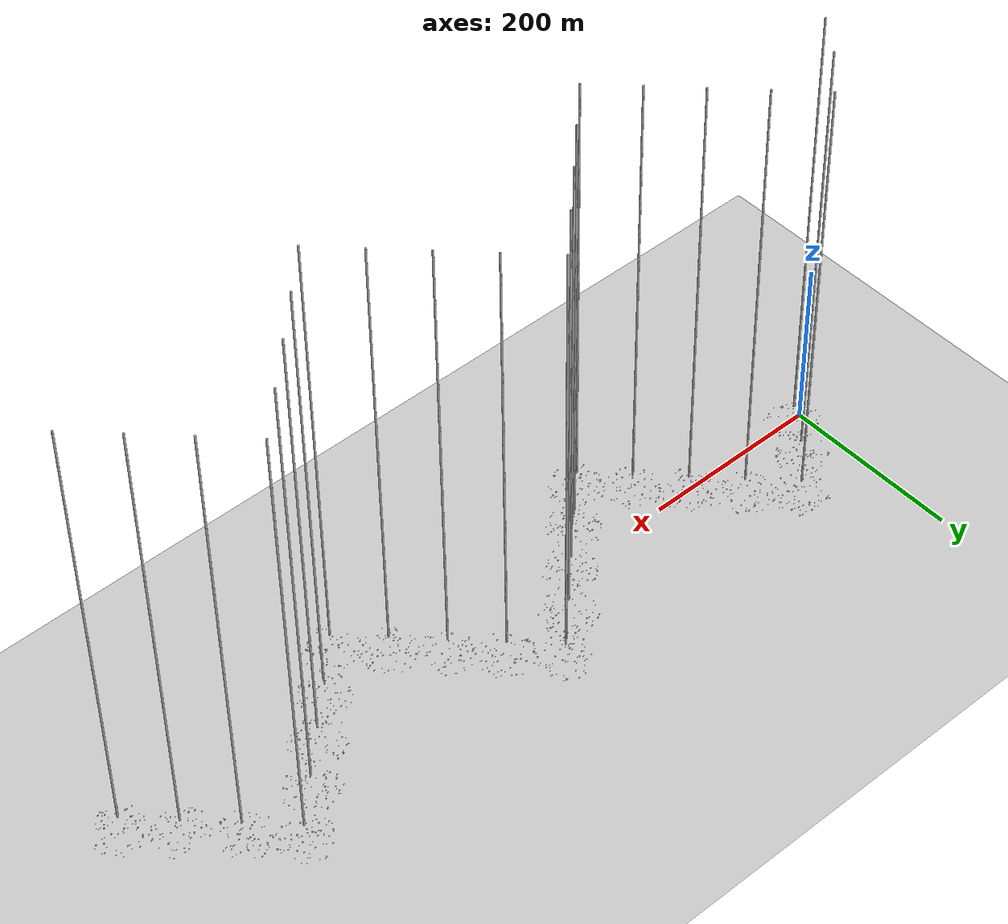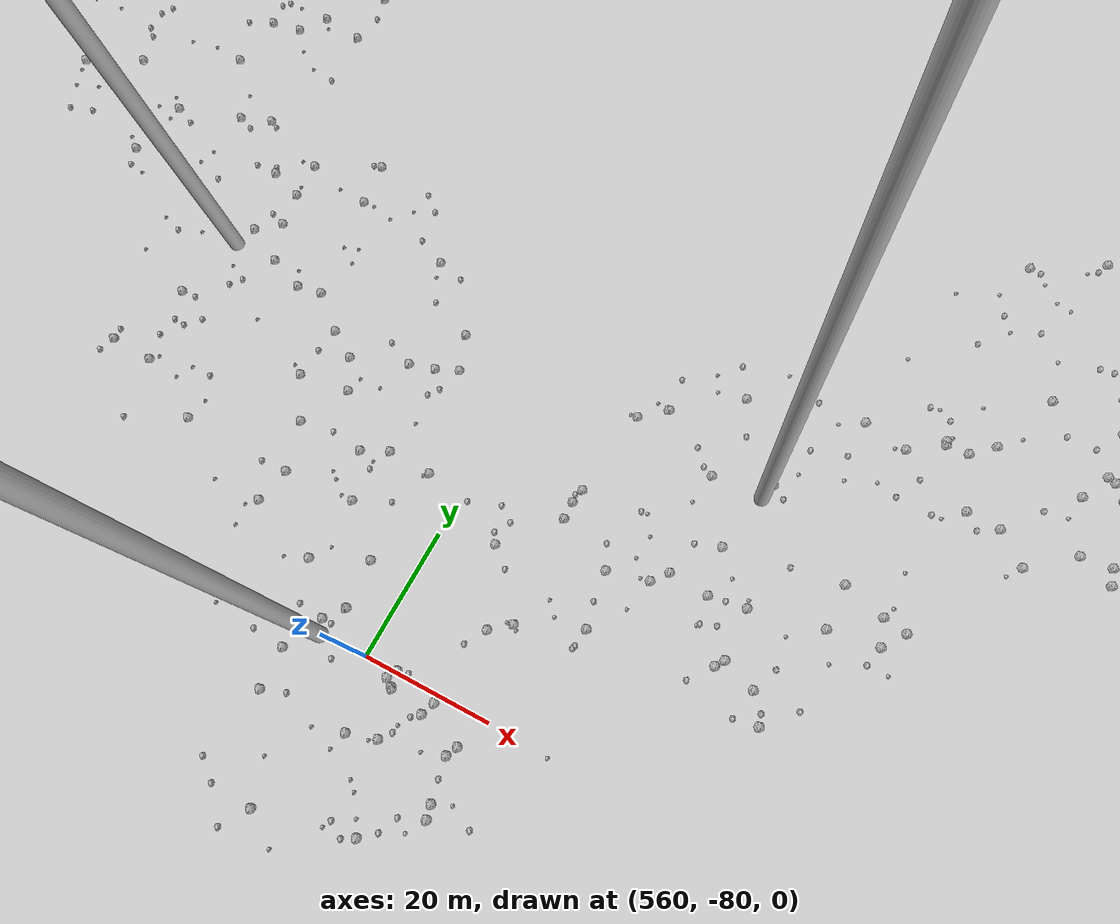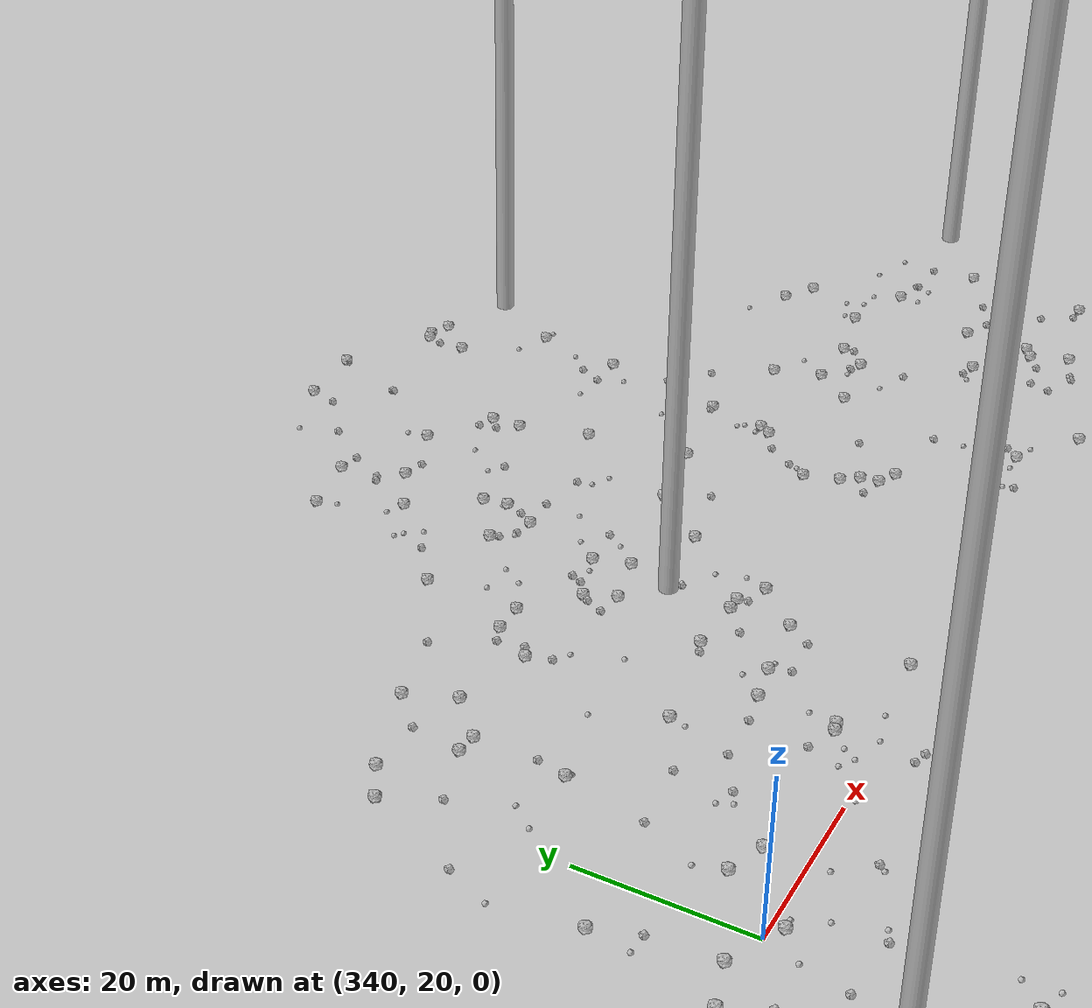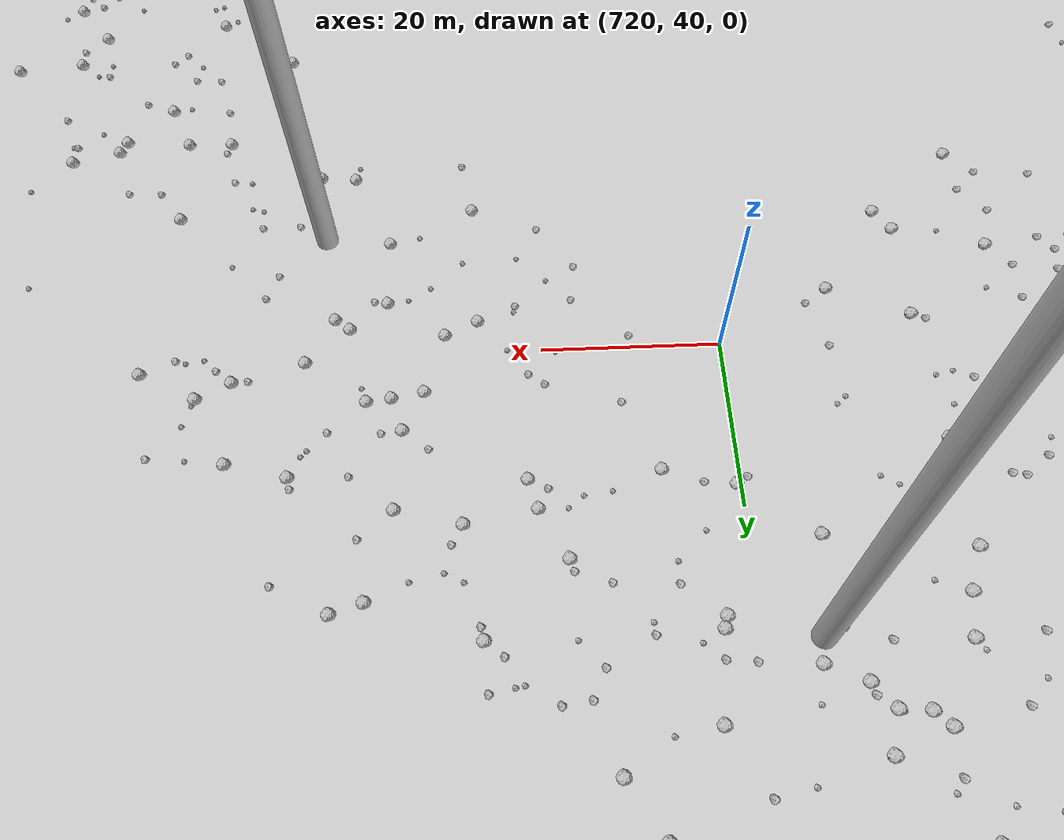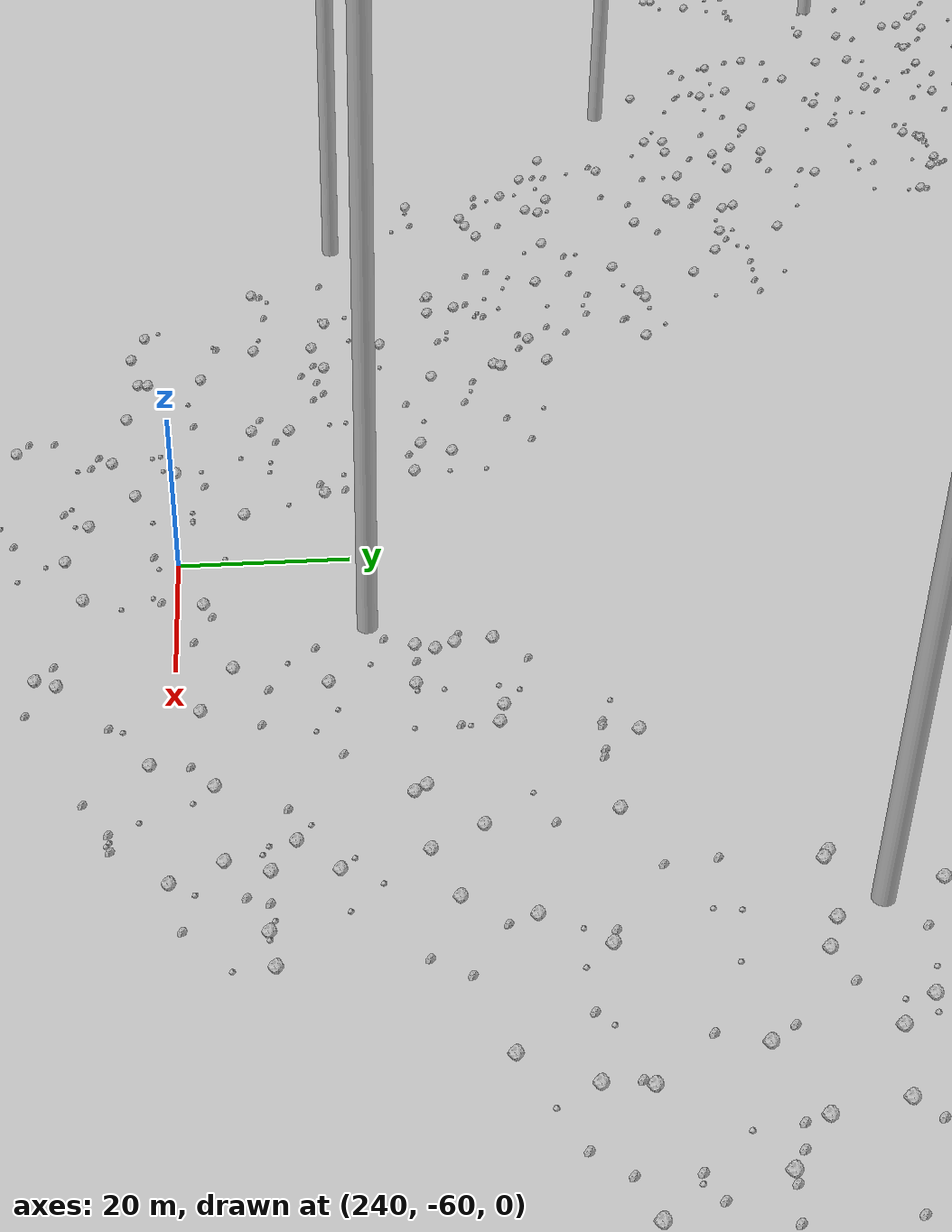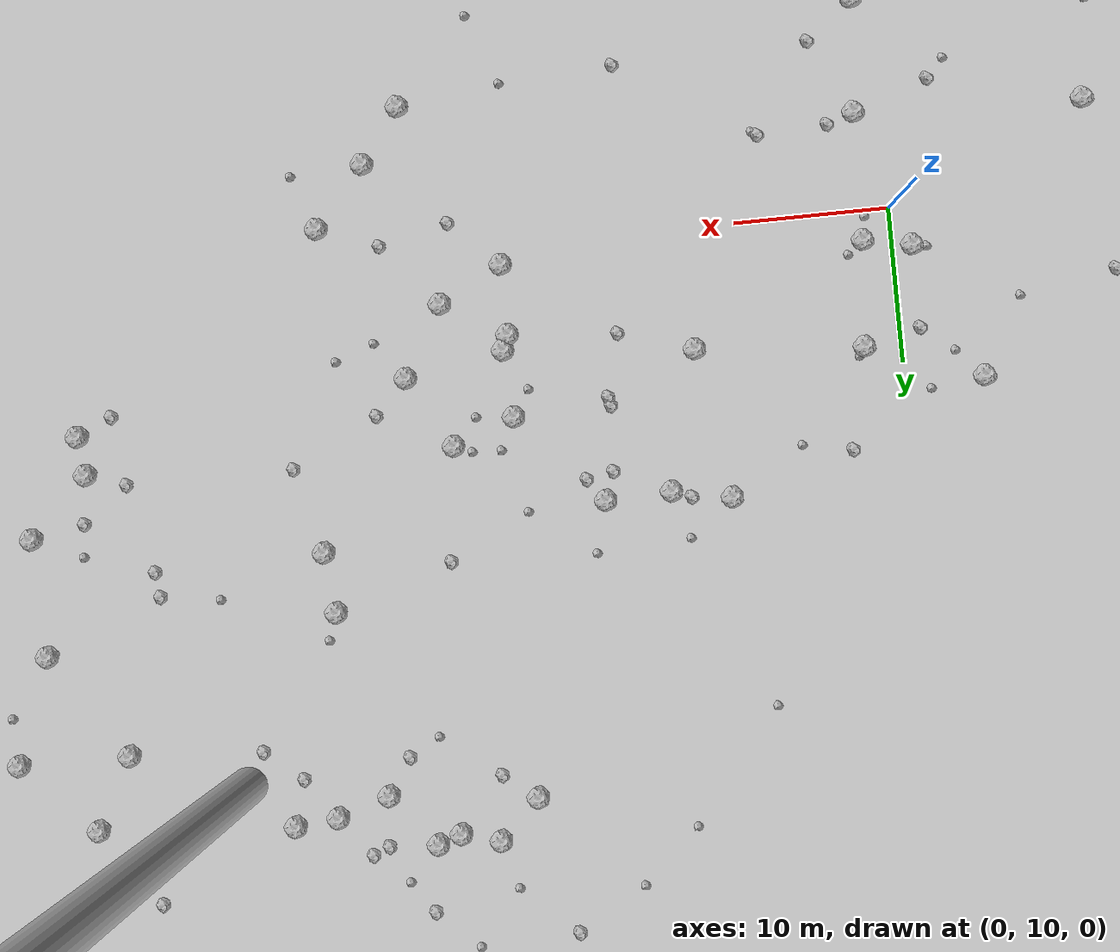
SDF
<sdf version="1.6">
 <world name="default">
  <include><uri>model://custom_ground</uri></include>
  <include><uri>model://sun</uri></include>
  <spherical_coordinates>
   <surface_model>EARTH_WGS84</surface_model>
   <latitude_deg>38.161479</latitude_deg>
   <longitude_deg>-122.454630</longitude_deg>
   <elevation>488.0</elevation>
   <heading_deg>90</heading_deg>
  </spherical_coordinates>
  <model name="rock1_0_0">
   <include><uri>model://rock1</uri><pose>-7.665097788831506 -9.14031644332022 0.5 0 0 0</pose></include>
  </model>
  <model name="rock1_0_1">
   <include><uri>model://rock1</uri><pose>1.749082950583304 3.670253869079552 0.5 0 0 0</pose></include>
  </model>
  <model name="rock1_0_2">
   <include><uri>model://rock1</uri><pose>27.285335235242513 -19.18047251315876 0.5 0 0 0</pose></include>
  </model>
  <model name="rock1_0_3">
   <include><uri>model://rock1</uri><pose>15.75125062573997 26.80326223767741 0.5 0 0 0</pose></include>
  </model>
  <model name="rock1_0_4">
   <include><uri>model://rock1</uri><pose>32.07330132265277 17.930565343451136 0.5 0 0 0</pose></include>
  </model>
  <model name="rock1_0_5">
   <include><uri>model://rock1</uri><pose>33.524904742795435 3.9685626496330997 0.5 0 0 0</pose></include>
  </model>
  <model name="rock1_0_6">
   <include><uri>model://rock1</uri><pose>29.413794461519743 13.387691711273924 0.5 0 0 0</pose></include>
  </model>
  <model name="rock1_0_7">
   <include><uri>model://rock1</uri><pose>11.885067412005938 27.55520479216201 0.5 0 0 0</pose></include>
  </model>
  <model name="rock1_0_8">
   <include><uri>model://rock1</uri><pose>-13.78052722447391 -2.6110933847036506 0.5 0 0 0</pose></include>
  </model>
  <model name="rock1_0_9">
   <include><uri>model://rock1</uri><pose>2.493760067396188 18.73852418809131 0.5 0 0 0</pose></include>
  </model>
  <model name="rock1_0_10">
   <include><uri>model://rock1</uri><pose>25.666368532358263 16.73550872525572 0.5 0 0 0</pose></include>
  </model>
  <model name="rock1_0_11">
   <include><uri>model://rock1</uri><pose>24.224269662808716 -18.302510047962393 0.5 0 0 0</pose></include>
  </model>
  <model name="rock1_0_12">
   <include><uri>model://rock1</uri><pose>-5.019593318715749 21.329093604675172 0.5 0 0 0</pose></include>
  </model>
  <model name="rock1_0_13">
   <include><uri>model://rock1</uri><pose>5.085116447933309 -20.34654263689962 0.5 0 0 0</pose></include>
  </model>
  <model name="rock1_0_14">
   <include><uri>model://rock1</uri><pose>1.9471901750164342 11.91224014068031 0.5 0 0 0</pose></include>
  </model>
  <model name="rock1_0_15">
   <include><uri>model://rock1</uri><pose>30.919128769261434 0.49162523178139494 0.5 0 0 0</pose></include>
  </model>
  <model name="rock1_0_16">
   <include><uri>model://rock1</uri><pose>25.385912588542872 21.061261592377242 0.5 0 0 0</pose></include>
  </model>
  <model name="rock1_0_17">
   <include><uri>model://rock1</uri><pose>-9.442079987540762 -14.880738652382053 0.5 0 0 0</pose></include>
  </model>
  <model name="rock1_0_18">
   <include><uri>model://rock1</uri><pose>36.85533938851372 7.8275449660594205 0.5 0 0 0</pose></include>
  </model>
  <model name="rock1_0_19">
   <include><uri>model://rock1</uri><pose>6.348032613185829 -19.26625221608378 0.5 0 0 0</pose></include>
  </model>
  <model name="rock1_0_20">
   <include><uri>model://rock1</uri><pose>-7.864524463861498 -12.53873812769357 0.5 0 0 0</pose></include>
  </model>
  <model name="rock1_0_21">
   <include><uri>model://rock1</uri><pose>25.27933930589922 11.224622398152306 0.5 0 0 0</pose></include>
  </model>
  <model name="rock1_0_22">
   <include><uri>model://rock1</uri><pose>13.387478105056204 17.848089938084414 0.5 0 0 0</pose></include>
  </model>
  <model name="rock1_0_23">
   <include><uri>model://rock1</uri><pose>1.2205791135359405 -3.6570912618335996 0.5 0 0 0</pose></include>
  </model>
  <model name="rock1_0_24">
   <include><uri>model://rock1</uri><pose>-1.179028126333911 12.505851895990396 0.5 0 0 0</pose></include>
  </model>
  <model name="rock1_0_25">
   <include><uri>model://rock1</uri><pose>-12.958369268569465 4.176922521098547 0.5 0 0 0</pose></include>
  </model>
  <model name="rock1_0_26">
   <include><uri>model://rock1</uri><pose>2.869627095277778 -6.978271631738778 0.5 0 0 0</pose></include>
  </model>
  <model name="rock2_0_0">
   <include><uri>model://rock2</uri><pose>3.4596056904368737 4.280809921026105 0.3 0 0 0</pose></include>
  </model>
  <model name="rock2_0_1">
   <include><uri>model://rock2</uri><pose>-0.6517869298892691 -20.13078063236705 0.3 0 0 0</pose></include>
  </model>
  <model name="rock2_0_2">
   <include><uri>model://rock2</uri><pose>4.229515482831843 -1.172539416506055 0.3 0 0 0</pose></include>
  </model>
  <model name="rock2_0_3">
   <include><uri>model://rock2</uri><pose>3.794735326104398 25.30416215305455 0.3 0 0 0</pose></include>
  </model>
  <model name="rock2_0_4">
   <include><uri>model://rock2</uri><pose>28.428438567673226 8.233228893540698 0.3 0 0 0</pose></include>
  </model>
  <model name="rock2_0_5">
   <include><uri>model://rock2</uri><pose>10.375432184818777 -7.60723954187355 0.3 0 0 0</pose></include>
  </model>
  <model name="rock2_0_6">
   <include><uri>model://rock2</uri><pose>-17.00614192292381 6.372796739049868 0.3 0 0 0</pose></include>
  </model>
  <model name="rock2_0_7">
   <include><uri>model://rock2</uri><pose>25.768662312333554 -12.79082683371626 0.3 0 0 0</pose></include>
  </model>
  <model name="rock2_0_8">
   <include><uri>model://rock2</uri><pose>32.94953089482068 9.291203279228213 0.3 0 0 0</pose></include>
  </model>
  <model name="rock2_0_9">
   <include><uri>model://rock2</uri><pose>18.211138209968503 16.357638656225944 0.3 0 0 0</pose></include>
  </model>
  <model name="rock2_0_10">
   <include><uri>model://rock2</uri><pose>22.188953299586544 -22.354559475552733 0.3 0 0 0</pose></include>
  </model>
  <model name="rock2_0_11">
   <include><uri>model://rock2</uri><pose>22.91453507927251 -22.44850692792692 0.3 0 0 0</pose></include>
  </model>
  <model name="rock2_0_12">
   <include><uri>model://rock2</uri><pose>4.553988188334941 -20.750430294265865 0.3 0 0 0</pose></include>
  </model>
  <model name="rock2_0_13">
   <include><uri>model://rock2</uri><pose>-8.54578334672624 -15.349663889802734 0.3 0 0 0</pose></include>
  </model>
  <model name="rock2_0_14">
   <include><uri>model://rock2</uri><pose>14.228346526496502 -6.910479446993385 0.3 0 0 0</pose></include>
  </model>
  <model name="rock2_0_15">
   <include><uri>model://rock2</uri><pose>-1.3638564184170718 -11.289715266932625 0.3 0 0 0</pose></include>
  </model>
  <model name="rock2_0_16">
   <include><uri>model://rock2</uri><pose>19.0778589585115 20.963206040833107 0.3 0 0 0</pose></include>
  </model>
  <model name="rock2_0_17">
   <include><uri>model://rock2</uri><pose>-10.87525335391939 -17.738307758585886 0.3 0 0 0</pose></include>
  </model>
  <model name="rock2_0_18">
   <include><uri>model://rock2</uri><pose>16.899232307803317 -0.8641274994150301 0.3 0 0 0</pose></include>
  </model>
  <model name="rock2_0_19">
   <include><uri>model://rock2</uri><pose>-3.22626367654588 1.9544306026330887 0.3 0 0 0</pose></include>
  </model>
  <model name="rock2_0_20">
   <include><uri>model://rock2</uri><pose>31.584381704894483 -13.12686208408423 0.3 0 0 0</pose></include>
  </model>
  <model name="rock2_0_21">
   <include><uri>model://rock2</uri><pose>17.47542201340682 -8.259515073139895 0.3 0 0 0</pose></include>
  </model>
  <model name="rock2_0_22">
   <include><uri>model://rock2</uri><pose>14.451529825865734 27.323723913471575 0.3 0 0 0</pose></include>
  </model>
  <model name="rock2_0_23">
   <include><uri>model://rock2</uri><pose>-1.2572025149936152 17.891579246761502 0.3 0 0 0</pose></include>
  </model>
  <model name="rock2_0_24">
   <include><uri>model://rock2</uri><pose>8.025530159806266 4.530840943088968 0.3 0 0 0</pose></include>
  </model>
  <model name="rock2_0_25">
   <include><uri>model://rock2</uri><pose>2.2678380931299067 -13.911462652463126 0.3 0 0 0</pose></include>
  </model>
  <model name="rock2_0_26">
   <include><uri>model://rock2</uri><pose>-14.184507099445543 15.313589074548716 0.3 0 0 0</pose></include>
  </model>
  <model name="rock3_0_0">
   <include><uri>model://rock3</uri><pose>1.6085188890901136 10.355240943191362 0.2 0 0 0</pose></include>
  </model>
  <model name="rock3_0_1">
   <include><uri>model://rock3</uri><pose>32.52540843352298 -19.58435299580917 0.2 0 0 0</pose></include>
  </model>
  <model name="rock3_0_2">
   <include><uri>model://rock3</uri><pose>-5.842579602990924 -3.3816566514724506 0.2 0 0 0</pose></include>
  </model>
  <model name="rock3_0_3">
   <include><uri>model://rock3</uri><pose>38.19494450055906 4.22639134650354 0.2 0 0 0</pose></include>
  </model>
  <model name="rock3_0_4">
   <include><uri>model://rock3</uri><pose>2.8876386019431166 12.730959746259785 0.2 0 0 0</pose></include>
  </model>
  <model name="rock3_0_5">
   <include><uri>model://rock3</uri><pose>25.99650609674932 -5.010849022658739 0.2 0 0 0</pose></include>
  </model>
  <model name="rock3_0_6">
   <include><uri>model://rock3</uri><pose>8.3502838424733 4.213658412782742 0.2 0 0 0</pose></include>
  </model>
  <model name="rock3_0_7">
   <include><uri>model://rock3</uri><pose>-7.962601792055954 -23.920803267538304 0.2 0 0 0</pose></include>
  </model>
  <model name="rock3_0_8">
   <include><uri>model://rock3</uri><pose>4.352075963170709 -12.827875309682241 0.2 0 0 0</pose></include>
  </model>
  <model name="rock3_0_9">
   <include><uri>model://rock3</uri><pose>24.239352585488795 -0.45258105459970466 0.2 0 0 0</pose></include>
  </model>
  <model name="rock3_0_10">
   <include><uri>model://rock3</uri><pose>24.254748681737226 19.344718655461634 0.2 0 0 0</pose></include>
  </model>
  <model name="rock3_0_11">
   <include><uri>model://rock3</uri><pose>-0.20512178812184345 -25.46008244982552 0.2 0 0 0</pose></include>
  </model>
  <model name="rock3_0_12">
   <include><uri>model://rock3</uri><pose>-3.3975271585151354 19.50367510143125 0.2 0 0 0</pose></include>
  </model>
  <model name="rock3_0_13">
   <include><uri>model://rock3</uri><pose>7.224328096574254 -24.31520440703946 0.2 0 0 0</pose></include>
  </model>
  <model name="rock3_0_14">
   <include><uri>model://rock3</uri><pose>2.7828330817662987 19.30267102165346 0.2 0 0 0</pose></include>
  </model>
  <model name="rock3_0_15">
   <include><uri>model://rock3</uri><pose>18.057961637274005 -11.949573640465903 0.2 0 0 0</pose></include>
  </model>
  <model name="rock3_0_16">
   <include><uri>model://rock3</uri><pose>7.011900339744248 24.651277785880914 0.2 0 0 0</pose></include>
  </model>
  <model name="rock3_0_17">
   <include><uri>model://rock3</uri><pose>-1.6286741435458048 21.806969482024797 0.2 0 0 0</pose></include>
  </model>
  <model name="rock3_0_18">
   <include><uri>model://rock3</uri><pose>-7.9071052090242855 16.382439326202487 0.2 0 0 0</pose></include>
  </model>
  <model name="rock3_0_19">
   <include><uri>model://rock3</uri><pose>28.236159798229394 23.01756476491753 0.2 0 0 0</pose></include>
  </model>
  <model name="rock3_0_20">
   <include><uri>model://rock3</uri><pose>-4.383712893408161 0.6609132978399437 0.2 0 0 0</pose></include>
  </model>
  <model name="rock3_0_21">
   <include><uri>model://rock3</uri><pose>12.246662145499009 -25.598659538877513 0.2 0 0 0</pose></include>
  </model>
  <model name="rock3_0_22">
   <include><uri>model://rock3</uri><pose>17.865228474644972 -12.599141670448716 0.2 0 0 0</pose></include>
  </model>
  <model name="rock3_0_23">
   <include><uri>model://rock3</uri><pose>-2.203053014971953 12.641537940978587 0.2 0 0 0</pose></include>
  </model>
  <model name="rock3_0_24">
   <include><uri>model://rock3</uri><pose>27.2044178552421 -22.141873899259444 0.2 0 0 0</pose></include>
  </model>
  <model name="rock3_0_25">
   <include><uri>model://rock3</uri><pose>-6.923131828172281 -17.739128650781424 0.2 0 0 0</pose></include>
  </model>
  <model name="rock3_0_26">
   <include><uri>model://rock3</uri><pose>6.699759921434175 -21.698413097821806 0.2 0 0 0</pose></include>
  </model>
  <model name="rock1_1_0">
   <include><uri>model://rock1</uri><pose>60.581617195760266 26.70385435200773 0.5 0 0 0</pose></include>
  </model>
  <model name="rock1_1_1">
   <include><uri>model://rock1</uri><pose>52.09498281434799 40.36637811614494 0.5 0 0 0</pose></include>
  </model>
  <model name="rock1_1_2">
   <include><uri>model://rock1</uri><pose>38.39729437676696 28.56953059325704 0.5 0 0 0</pose></include>
  </model>
  <model name="rock1_1_3">
   <include><uri>model://rock1</uri><pose>26.206502792264263 45.5726914153605 0.5 0 0 0</pose></include>
  </model>
  <model name="rock1_1_4">
   <include><uri>model://rock1</uri><pose>25.276233742849325 15.756108766217277 0.5 0 0 0</pose></include>
  </model>
  <model name="rock1_1_5">
   <include><uri>model://rock1</uri><pose>46.94060909174181 55.0141437562063 0.5 0 0 0</pose></include>
  </model>
  <model name="rock1_1_6">
   <include><uri>model://rock1</uri><pose>19.907439764856164 60.003639356380354 0.5 0 0 0</pose></include>
  </model>
  <model name="rock1_1_7">
   <include><uri>model://rock1</uri><pose>20.020614182534437 26.974599512435105 0.5 0 0 0</pose></include>
  </model>
  <model name="rock1_1_8">
   <include><uri>model://rock1</uri><pose>32.88528128877702 47.96240063055446 0.5 0 0 0</pose></include>
  </model>
  <model name="rock1_1_9">
   <include><uri>model://rock1</uri><pose>29.413745413171256 22.56178813059754 0.5 0 0 0</pose></include>
  </model>
  <model name="rock1_1_10">
   <include><uri>model://rock1</uri><pose>64.1765541871802 32.39372556338897 0.5 0 0 0</pose></include>
  </model>
  <model name="rock1_1_11">
   <include><uri>model://rock1</uri><pose>59.2203849180475 40.30298797954839 0.5 0 0 0</pose></include>
  </model>
  <model name="rock1_1_12">
   <include><uri>model://rock1</uri><pose>51.06824450202776 60.66411065562845 0.5 0 0 0</pose></include>
  </model>
  <model name="rock1_1_13">
   <include><uri>model://rock1</uri><pose>35.741157542394404 44.54615811452517 0.5 0 0 0</pose></include>
  </model>
  <model name="rock1_1_14">
   <include><uri>model://rock1</uri><pose>56.734730113820376 33.51282934837488 0.5 0 0 0</pose></include>
  </model>
  <model name="rock1_1_15">
   <include><uri>model://rock1</uri><pose>58.06467205288585 54.94763980598652 0.5 0 0 0</pose></include>
  </model>
  <model name="rock1_1_16">
   <include><uri>model://rock1</uri><pose>41.90471631299974 45.931375252470396 0.5 0 0 0</pose></include>
  </model>
  <model name="rock1_1_17">
   <include><uri>model://rock1</uri><pose>60.36841138945248 25.384185004037946 0.5 0 0 0</pose></include>
  </model>
  <model name="rock1_1_18">
   <include><uri>model://rock1</uri><pose>45.96160050074382 67.92389093569568 0.5 0 0 0</pose></include>
  </model>
  <model name="rock1_1_19">
   <include><uri>model://rock1</uri><pose>53.16900173428934 22.12227431569842 0.5 0 0 0</pose></include>
  </model>
  <model name="rock1_1_20">
   <include><uri>model://rock1</uri><pose>54.52528279595256 44.95873726546226 0.5 0 0 0</pose></include>
  </model>
  <model name="rock1_1_21">
   <include><uri>model://rock1</uri><pose>57.025917347943725 25.903868408645994 0.5 0 0 0</pose></include>
  </model>
  <model name="rock1_1_22">
   <include><uri>model://rock1</uri><pose>39.1250587376576 45.637123333541794 0.5 0 0 0</pose></include>
  </model>
  <model name="rock1_1_23">
   <include><uri>model://rock1</uri><pose>28.8389394459588 48.111705344246474 0.5 0 0 0</pose></include>
  </model>
  <model name="rock1_1_24">
   <include><uri>model://rock1</uri><pose>31.352459150280723 47.43273002827598 0.5 0 0 0</pose></include>
  </model>
  <model name="rock1_1_25">
   <include><uri>model://rock1</uri><pose>53.45731672046449 19.62190426122236 0.5 0 0 0</pose></include>
  </model>
  <model name="rock1_1_26">
   <include><uri>model://rock1</uri><pose>37.97658028130452 32.48362968672013 0.5 0 0 0</pose></include>
  </model>
  <model name="rock2_1_0">
   <include><uri>model://rock2</uri><pose>50.638702598522464 23.008456259696757 0.3 0 0 0</pose></include>
  </model>
  <model name="rock2_1_1">
   <include><uri>model://rock2</uri><pose>49.1546193270068 30.39253338745471 0.3 0 0 0</pose></include>
  </model>
  <model name="rock2_1_2">
   <include><uri>model://rock2</uri><pose>37.10022677752965 48.30340875308192 0.3 0 0 0</pose></include>
  </model>
  <model name="rock2_1_3">
   <include><uri>model://rock2</uri><pose>49.34669391370288 28.788256482574283 0.3 0 0 0</pose></include>
  </model>
  <model name="rock2_1_4">
   <include><uri>model://rock2</uri><pose>16.855151821373045 58.51577036002593 0.3 0 0 0</pose></include>
  </model>
  <model name="rock2_1_5">
   <include><uri>model://rock2</uri><pose>19.332725700600612 25.190557659181838 0.3 0 0 0</pose></include>
  </model>
  <model name="rock2_1_6">
   <include><uri>model://rock2</uri><pose>51.19300364862791 18.55973773473002 0.3 0 0 0</pose></include>
  </model>
  <model name="rock2_1_7">
   <include><uri>model://rock2</uri><pose>42.97626490013505 67.36940919940034 0.3 0 0 0</pose></include>
  </model>
  <model name="rock2_1_8">
   <include><uri>model://rock2</uri><pose>53.581021651935956 25.26019636775263 0.3 0 0 0</pose></include>
  </model>
  <model name="rock2_1_9">
   <include><uri>model://rock2</uri><pose>24.35706080394806 54.563436055009916 0.3 0 0 0</pose></include>
  </model>
  <model name="rock2_1_10">
   <include><uri>model://rock2</uri><pose>66.20686081335415 39.85850645125048 0.3 0 0 0</pose></include>
  </model>
  <model name="rock2_1_11">
   <include><uri>model://rock2</uri><pose>56.21938715798919 57.206785571369814 0.3 0 0 0</pose></include>
  </model>
  <model name="rock2_1_12">
   <include><uri>model://rock2</uri><pose>39.83998818046675 23.057416345846917 0.3 0 0 0</pose></include>
  </model>
  <model name="rock2_1_13">
   <include><uri>model://rock2</uri><pose>50.4479546749088 66.5155196387347 0.3 0 0 0</pose></include>
  </model>
  <model name="rock2_1_14">
   <include><uri>model://rock2</uri><pose>68.90662102091386 39.77683893299764 0.3 0 0 0</pose></include>
  </model>
  <model name="rock2_1_15">
   <include><uri>model://rock2</uri><pose>28.349584105570283 43.970600990116814 0.3 0 0 0</pose></include>
  </model>
  <model name="rock2_1_16">
   <include><uri>model://rock2</uri><pose>50.90408661207593 50.144205931266015 0.3 0 0 0</pose></include>
  </model>
  <model name="rock2_1_17">
   <include><uri>model://rock2</uri><pose>43.51973922900113 41.00028127254536 0.3 0 0 0</pose></include>
  </model>
  <model name="rock2_1_18">
   <include><uri>model://rock2</uri><pose>34.149879101138914 42.252064599700184 0.3 0 0 0</pose></include>
  </model>
  <model name="rock2_1_19">
   <include><uri>model://rock2</uri><pose>34.18849924303265 20.15776376926589 0.3 0 0 0</pose></include>
  </model>
  <model name="rock2_1_20">
   <include><uri>model://rock2</uri><pose>41.073842518601225 43.00031546642911 0.3 0 0 0</pose></include>
  </model>
  <model name="rock2_1_21">
   <include><uri>model://rock2</uri><pose>16.85065398342236 57.31333366998341 0.3 0 0 0</pose></include>
  </model>
  <model name="rock2_1_22">
   <include><uri>model://rock2</uri><pose>30.28291898375778 29.971364044741325 0.3 0 0 0</pose></include>
  </model>
  <model name="rock2_1_23">
   <include><uri>model://rock2</uri><pose>36.01835232467721 47.8431140601663 0.3 0 0 0</pose></include>
  </model>
  <model name="rock2_1_24">
   <include><uri>model://rock2</uri><pose>21.085717875862414 25.54336942051713 0.3 0 0 0</pose></include>
  </model>
  <model name="rock2_1_25">
   <include><uri>model://rock2</uri><pose>33.45725074790259 52.33204129044119 0.3 0 0 0</pose></include>
  </model>
  <model name="rock2_1_26">
   <include><uri>model://rock2</uri><pose>19.208061519682126 20.389524879949292 0.3 0 0 0</pose></include>
  </model>
  <model name="rock3_1_0">
   <include><uri>model://rock3</uri><pose>35.72434160635503 66.25843321343325 0.2 0 0 0</pose></include>
  </model>
  <model name="rock3_1_1">
   <include><uri>model://rock3</uri><pose>19.84059481677002 51.92869218519606 0.2 0 0 0</pose></include>
  </model>
  <model name="rock3_1_2">
   <include><uri>model://rock3</uri><pose>65.01083094600557 36.59628180680173 0.2 0 0 0</pose></include>
  </model>
  <model name="rock3_1_3">
   <include><uri>model://rock3</uri><pose>53.80322859587271 27.35584079018488 0.2 0 0 0</pose></include>
  </model>
  <model name="rock3_1_4">
   <include><uri>model://rock3</uri><pose>38.57531850439638 34.2371641738999 0.2 0 0 0</pose></include>
  </model>
  <model name="rock3_1_5">
   <include><uri>model://rock3</uri><pose>32.134665957475065 41.09504016703244 0.2 0 0 0</pose></include>
  </model>
  <model name="rock3_1_6">
   <include><uri>model://rock3</uri><pose>44.01202066684602 61.51067200080704 0.2 0 0 0</pose></include>
  </model>
  <model name="rock3_1_7">
   <include><uri>model://rock3</uri><pose>27.931508542455397 51.31125471921209 0.2 0 0 0</pose></include>
  </model>
  <model name="rock3_1_8">
   <include><uri>model://rock3</uri><pose>20.847527440068234 30.31284583379193 0.2 0 0 0</pose></include>
  </model>
  <model name="rock3_1_9">
   <include><uri>model://rock3</uri><pose>24.99661909492206 27.218804234892104 0.2 0 0 0</pose></include>
  </model>
  <model name="rock3_1_10">
   <include><uri>model://rock3</uri><pose>45.29754164154155 30.931141922312634 0.2 0 0 0</pose></include>
  </model>
  <model name="rock3_1_11">
   <include><uri>model://rock3</uri><pose>31.225093960455737 61.86145321711958 0.2 0 0 0</pose></include>
  </model>
  <model name="rock3_1_12">
   <include><uri>model://rock3</uri><pose>59.395738907679906 37.287466035173495 0.2 0 0 0</pose></include>
  </model>
  <model name="rock3_1_13">
   <include><uri>model://rock3</uri><pose>69.97085862613466 40.298670954301016 0.2 0 0 0</pose></include>
  </model>
  <model name="rock3_1_14">
   <include><uri>model://rock3</uri><pose>44.326849840221634 62.934484020271654 0.2 0 0 0</pose></include>
  </model>
  <model name="rock3_1_15">
   <include><uri>model://rock3</uri><pose>26.347641422049353 23.107618306053272 0.2 0 0 0</pose></include>
  </model>
  <model name="rock3_1_16">
   <include><uri>model://rock3</uri><pose>10.216069841107574 41.208332036548725 0.2 0 0 0</pose></include>
  </model>
  <model name="rock3_1_17">
   <include><uri>model://rock3</uri><pose>34.87696552956672 50.241983235645066 0.2 0 0 0</pose></include>
  </model>
  <model name="rock3_1_18">
   <include><uri>model://rock3</uri><pose>33.894117392882464 15.454587066403608 0.2 0 0 0</pose></include>
  </model>
  <model name="rock3_1_19">
   <include><uri>model://rock3</uri><pose>30.762702095779954 54.82672997023308 0.2 0 0 0</pose></include>
  </model>
  <model name="rock3_1_20">
   <include><uri>model://rock3</uri><pose>29.27390905568396 57.15326196533464 0.2 0 0 0</pose></include>
  </model>
  <model name="rock3_1_21">
   <include><uri>model://rock3</uri><pose>27.78290917012328 20.821172103783585 0.2 0 0 0</pose></include>
  </model>
  <model name="rock3_1_22">
   <include><uri>model://rock3</uri><pose>63.32710179768688 27.930242051559812 0.2 0 0 0</pose></include>
  </model>
  <model name="rock3_1_23">
   <include><uri>model://rock3</uri><pose>16.094397530938636 48.468658320750414 0.2 0 0 0</pose></include>
  </model>
  <model name="rock3_1_24">
   <include><uri>model://rock3</uri><pose>14.724053592480107 29.91703059618118 0.2 0 0 0</pose></include>
  </model>
  <model name="rock3_1_25">
   <include><uri>model://rock3</uri><pose>36.44199038634088 16.403954129729346 0.2 0 0 0</pose></include>
  </model>
  <model name="rock3_1_26">
   <include><uri>model://rock3</uri><pose>45.58249937150025 68.02242277013985 0.2 0 0 0</pose></include>
  </model>
  <model name="rock1_2_0">
   <include><uri>model://rock1</uri><pose>94.13943438119033 68.65239853087633 0.5 0 0 0</pose></include>
  </model>
  <model name="rock1_2_1">
   <include><uri>model://rock1</uri><pose>78.83646162617958 50.87203407802512 0.5 0 0 0</pose></include>
  </model>
  <model name="rock1_2_2">
   <include><uri>model://rock1</uri><pose>86.61477132284672 102.77453548141378 0.5 0 0 0</pose></include>
  </model>
  <model name="rock1_2_3">
   <include><uri>model://rock1</uri><pose>101.54477865366933 100.58552281556595 0.5 0 0 0</pose></include>
  </model>
  <model name="rock1_2_4">
   <include><uri>model://rock1</uri><pose>71.53936273427426 73.5189218895699 0.5 0 0 0</pose></include>
  </model>
  <model name="rock1_2_5">
   <include><uri>model://rock1</uri><pose>76.19405815934222 67.22863164417112 0.5 0 0 0</pose></include>
  </model>
  <model name="rock1_2_6">
   <include><uri>model://rock1</uri><pose>93.67955075270544 91.58824703512641 0.5 0 0 0</pose></include>
  </model>
  <model name="rock1_2_7">
   <include><uri>model://rock1</uri><pose>106.94345210407019 67.94771957344963 0.5 0 0 0</pose></include>
  </model>
  <model name="rock1_2_8">
   <include><uri>model://rock1</uri><pose>101.25544381258013 99.96549479373397 0.5 0 0 0</pose></include>
  </model>
  <model name="rock1_2_9">
   <include><uri>model://rock1</uri><pose>80.36030684114642 57.63931329252485 0.5 0 0 0</pose></include>
  </model>
  <model name="rock1_2_10">
   <include><uri>model://rock1</uri><pose>63.00808923769739 100.90590240886323 0.5 0 0 0</pose></include>
  </model>
  <model name="rock1_2_11">
   <include><uri>model://rock1</uri><pose>64.69250991148871 101.58447184560256 0.5 0 0 0</pose></include>
  </model>
  <model name="rock1_2_12">
   <include><uri>model://rock1</uri><pose>101.49290233447243 89.16483976425599 0.5 0 0 0</pose></include>
  </model>
  <model name="rock1_2_13">
   <include><uri>model://rock1</uri><pose>50.20346664295397 78.7022844189088 0.5 0 0 0</pose></include>
  </model>
  <model name="rock1_2_14">
   <include><uri>model://rock1</uri><pose>91.72773871887448 56.7824747892472 0.5 0 0 0</pose></include>
  </model>
  <model name="rock1_2_15">
   <include><uri>model://rock1</uri><pose>77.37309323225413 74.36702222150899 0.5 0 0 0</pose></include>
  </model>
  <model name="rock1_2_16">
   <include><uri>model://rock1</uri><pose>56.16423950357826 75.60128207600212 0.5 0 0 0</pose></include>
  </model>
  <model name="rock1_2_17">
   <include><uri>model://rock1</uri><pose>88.94057164128536 92.44265342059307 0.5 0 0 0</pose></include>
  </model>
  <model name="rock1_2_18">
   <include><uri>model://rock1</uri><pose>56.42892386707793 79.22293542497471 0.5 0 0 0</pose></include>
  </model>
  <model name="rock1_2_19">
   <include><uri>model://rock1</uri><pose>75.83973669548784 70.05807185397612 0.5 0 0 0</pose></include>
  </model>
  <model name="rock1_2_20">
   <include><uri>model://rock1</uri><pose>86.68279375501896 68.50297057124163 0.5 0 0 0</pose></include>
  </model>
  <model name="rock1_2_21">
   <include><uri>model://rock1</uri><pose>81.41265484182547 94.07596736477328 0.5 0 0 0</pose></include>
  </model>
  <model name="rock1_2_22">
   <include><uri>model://rock1</uri><pose>98.07288985573335 100.87477708089645 0.5 0 0 0</pose></include>
  </model>
  <model name="rock1_2_23">
   <include><uri>model://rock1</uri><pose>83.72606973232769 96.36836961195291 0.5 0 0 0</pose></include>
  </model>
  <model name="rock1_2_24">
   <include><uri>model://rock1</uri><pose>102.7554153004843 75.00173591938558 0.5 0 0 0</pose></include>
  </model>
  <model name="rock1_2_25">
   <include><uri>model://rock1</uri><pose>61.84433690464941 103.2162641386218 0.5 0 0 0</pose></include>
  </model>
  <model name="rock1_2_26">
   <include><uri>model://rock1</uri><pose>88.06357577839685 86.07376317065275 0.5 0 0 0</pose></include>
  </model>
  <model name="rock2_2_0">
   <include><uri>model://rock2</uri><pose>80.67653049180471 100.58272865599855 0.3 0 0 0</pose></include>
  </model>
  <model name="rock2_2_1">
   <include><uri>model://rock2</uri><pose>69.15519219901446 75.32470091475275 0.3 0 0 0</pose></include>
  </model>
  <model name="rock2_2_2">
   <include><uri>model://rock2</uri><pose>66.70561385145244 60.65363365442703 0.3 0 0 0</pose></include>
  </model>
  <model name="rock2_2_3">
   <include><uri>model://rock2</uri><pose>54.08441068459874 73.00605444227124 0.3 0 0 0</pose></include>
  </model>
  <model name="rock2_2_4">
   <include><uri>model://rock2</uri><pose>96.18038180027683 79.46656271783739 0.3 0 0 0</pose></include>
  </model>
  <model name="rock2_2_5">
   <include><uri>model://rock2</uri><pose>81.49852265289047 60.428299690629295 0.3 0 0 0</pose></include>
  </model>
  <model name="rock2_2_6">
   <include><uri>model://rock2</uri><pose>108.69508872089236 78.74256267667712 0.3 0 0 0</pose></include>
  </model>
  <model name="rock2_2_7">
   <include><uri>model://rock2</uri><pose>85.07396280867951 67.92810946419527 0.3 0 0 0</pose></include>
  </model>
  <model name="rock2_2_8">
   <include><uri>model://rock2</uri><pose>97.24418525630621 66.31574061712354 0.3 0 0 0</pose></include>
  </model>
  <model name="rock2_2_9">
   <include><uri>model://rock2</uri><pose>56.6674837057168 64.52773654722985 0.3 0 0 0</pose></include>
  </model>
  <model name="rock2_2_10">
   <include><uri>model://rock2</uri><pose>55.36743242465877 70.05163303111378 0.3 0 0 0</pose></include>
  </model>
  <model name="rock2_2_11">
   <include><uri>model://rock2</uri><pose>95.81478610992619 95.21434725036092 0.3 0 0 0</pose></include>
  </model>
  <model name="rock2_2_12">
   <include><uri>model://rock2</uri><pose>64.28415088915058 77.8665175099048 0.3 0 0 0</pose></include>
  </model>
  <model name="rock2_2_13">
   <include><uri>model://rock2</uri><pose>108.76933584278106 78.89175197360066 0.3 0 0 0</pose></include>
  </model>
  <model name="rock2_2_14">
   <include><uri>model://rock2</uri><pose>72.22273515843165 103.35566791539885 0.3 0 0 0</pose></include>
  </model>
  <model name="rock2_2_15">
   <include><uri>model://rock2</uri><pose>85.21997285673095 69.78206154635639 0.3 0 0 0</pose></include>
  </model>
  <model name="rock2_2_16">
   <include><uri>model://rock2</uri><pose>89.45611517018233 80.95901248212871 0.3 0 0 0</pose></include>
  </model>
  <model name="rock2_2_17">
   <include><uri>model://rock2</uri><pose>82.31558989357907 72.30868475021029 0.3 0 0 0</pose></include>
  </model>
  <model name="rock2_2_18">
   <include><uri>model://rock2</uri><pose>78.36187913227128 103.1199175294723 0.3 0 0 0</pose></include>
  </model>
  <model name="rock2_2_19">
   <include><uri>model://rock2</uri><pose>105.26902604327715 68.52910104992549 0.3 0 0 0</pose></include>
  </model>
  <model name="rock2_2_20">
   <include><uri>model://rock2</uri><pose>106.20767595956444 80.61729804164295 0.3 0 0 0</pose></include>
  </model>
  <model name="rock2_2_21">
   <include><uri>model://rock2</uri><pose>92.42212689284676 100.35234598332889 0.3 0 0 0</pose></include>
  </model>
  <model name="rock2_2_22">
   <include><uri>model://rock2</uri><pose>97.74684060603198 81.7489496195834 0.3 0 0 0</pose></include>
  </model>
  <model name="rock2_2_23">
   <include><uri>model://rock2</uri><pose>67.7393267838212 53.69970688782079 0.3 0 0 0</pose></include>
  </model>
  <model name="rock2_2_24">
   <include><uri>model://rock2</uri><pose>98.62763674053164 70.35671157724659 0.3 0 0 0</pose></include>
  </model>
  <model name="rock2_2_25">
   <include><uri>model://rock2</uri><pose>60.15025807026302 100.00904811485573 0.3 0 0 0</pose></include>
  </model>
  <model name="rock2_2_26">
   <include><uri>model://rock2</uri><pose>62.94746519485291 67.1097420851157 0.3 0 0 0</pose></include>
  </model>
  <model name="rock3_2_0">
   <include><uri>model://rock3</uri><pose>60.756974657218855 90.60941956427035 0.2 0 0 0</pose></include>
  </model>
  <model name="rock3_2_1">
   <include><uri>model://rock3</uri><pose>60.5861760483573 83.3615793064602 0.2 0 0 0</pose></include>
  </model>
  <model name="rock3_2_2">
   <include><uri>model://rock3</uri><pose>99.4331566431315 79.57892148594576 0.2 0 0 0</pose></include>
  </model>
  <model name="rock3_2_3">
   <include><uri>model://rock3</uri><pose>91.76788044084657 59.66171900834529 0.2 0 0 0</pose></include>
  </model>
  <model name="rock3_2_4">
   <include><uri>model://rock3</uri><pose>98.24067234802155 89.55857088481893 0.2 0 0 0</pose></include>
  </model>
  <model name="rock3_2_5">
   <include><uri>model://rock3</uri><pose>81.0208775287704 99.9160719832424 0.2 0 0 0</pose></include>
  </model>
  <model name="rock3_2_6">
   <include><uri>model://rock3</uri><pose>70.8421180543005 100.57446095963184 0.2 0 0 0</pose></include>
  </model>
  <model name="rock3_2_7">
   <include><uri>model://rock3</uri><pose>101.16975944955617 61.749091976061194 0.2 0 0 0</pose></include>
  </model>
  <model name="rock3_2_8">
   <include><uri>model://rock3</uri><pose>105.79144373588832 81.70749323986459 0.2 0 0 0</pose></include>
  </model>
  <model name="rock3_2_9">
   <include><uri>model://rock3</uri><pose>72.92375268088672 80.744667908778 0.2 0 0 0</pose></include>
  </model>
  <model name="rock3_2_10">
   <include><uri>model://rock3</uri><pose>67.67444973492421 55.128126617377575 0.2 0 0 0</pose></include>
  </model>
  <model name="rock3_2_11">
   <include><uri>model://rock3</uri><pose>74.57280764587773 51.015853186176656 0.2 0 0 0</pose></include>
  </model>
  <model name="rock3_2_12">
   <include><uri>model://rock3</uri><pose>94.6076107868492 105.49543238568654 0.2 0 0 0</pose></include>
  </model>
  <model name="rock3_2_13">
   <include><uri>model://rock3</uri><pose>87.04075387520356 85.0131422386668 0.2 0 0 0</pose></include>
  </model>
  <model name="rock3_2_14">
   <include><uri>model://rock3</uri><pose>75.08730798643086 68.02508776572353 0.2 0 0 0</pose></include>
  </model>
  <model name="rock3_2_15">
   <include><uri>model://rock3</uri><pose>103.61627256226791 66.63054722078421 0.2 0 0 0</pose></include>
  </model>
  <model name="rock3_2_16">
   <include><uri>model://rock3</uri><pose>85.88231120336584 77.80448746420463 0.2 0 0 0</pose></include>
  </model>
  <model name="rock3_2_17">
   <include><uri>model://rock3</uri><pose>72.9417434911375 105.77425381144036 0.2 0 0 0</pose></include>
  </model>
  <model name="rock3_2_18">
   <include><uri>model://rock3</uri><pose>77.41804863625217 97.53510543874306 0.2 0 0 0</pose></include>
  </model>
  <model name="rock3_2_19">
   <include><uri>model://rock3</uri><pose>58.26023704521596 63.610925160673126 0.2 0 0 0</pose></include>
  </model>
  <model name="rock3_2_20">
   <include><uri>model://rock3</uri><pose>97.36271544471177 65.50007805914171 0.2 0 0 0</pose></include>
  </model>
  <model name="rock3_2_21">
   <include><uri>model://rock3</uri><pose>93.96696292394047 84.54613576462151 0.2 0 0 0</pose></include>
  </model>
  <model name="rock3_2_22">
   <include><uri>model://rock3</uri><pose>53.08245249030671 71.30007313280733 0.2 0 0 0</pose></include>
  </model>
  <model name="rock3_2_23">
   <include><uri>model://rock3</uri><pose>103.22314361471102 72.81034551704903 0.2 0 0 0</pose></include>
  </model>
  <model name="rock3_2_24">
   <include><uri>model://rock3</uri><pose>54.80420931045374 80.99977784044228 0.2 0 0 0</pose></include>
  </model>
  <model name="rock3_2_25">
   <include><uri>model://rock3</uri><pose>67.89049981138706 93.16222786260161 0.2 0 0 0</pose></include>
  </model>
  <model name="rock3_2_26">
   <include><uri>model://rock3</uri><pose>72.13100518394819 97.85421915221941 0.2 0 0 0</pose></include>
  </model>
  <model name="rock1_3_0">
   <include><uri>model://rock1</uri><pose>104.42241218409653 32.18224468546858 0.5 0 0 0</pose></include>
  </model>
  <model name="rock1_3_1">
   <include><uri>model://rock1</uri><pose>138.17085632216128 17.676033353072427 0.5 0 0 0</pose></include>
  </model>
  <model name="rock1_3_2">
   <include><uri>model://rock1</uri><pose>120.41530400520894 31.909875748948696 0.5 0 0 0</pose></include>
  </model>
  <model name="rock1_3_3">
   <include><uri>model://rock1</uri><pose>129.73045433510617 33.022591846974734 0.5 0 0 0</pose></include>
  </model>
  <model name="rock1_3_4">
   <include><uri>model://rock1</uri><pose>136.85082694011288 59.22083274457421 0.5 0 0 0</pose></include>
  </model>
  <model name="rock1_3_5">
   <include><uri>model://rock1</uri><pose>124.72230346316269 14.62404354884131 0.5 0 0 0</pose></include>
  </model>
  <model name="rock1_3_6">
   <include><uri>model://rock1</uri><pose>123.87027336505182 58.20176228501294 0.5 0 0 0</pose></include>
  </model>
  <model name="rock1_3_7">
   <include><uri>model://rock1</uri><pose>128.95131446781394 17.31911747546956 0.5 0 0 0</pose></include>
  </model>
  <model name="rock1_3_8">
   <include><uri>model://rock1</uri><pose>110.9131018787313 46.14185298519373 0.5 0 0 0</pose></include>
  </model>
  <model name="rock1_3_9">
   <include><uri>model://rock1</uri><pose>104.26262672856446 56.846752340746974 0.5 0 0 0</pose></include>
  </model>
  <model name="rock1_3_10">
   <include><uri>model://rock1</uri><pose>92.45935319393996 50.97459147587827 0.5 0 0 0</pose></include>
  </model>
  <model name="rock1_3_11">
   <include><uri>model://rock1</uri><pose>111.20260663753146 35.25432913982392 0.5 0 0 0</pose></include>
  </model>
  <model name="rock1_3_12">
   <include><uri>model://rock1</uri><pose>130.2204577355031 24.88318315185832 0.5 0 0 0</pose></include>
  </model>
  <model name="rock1_3_13">
   <include><uri>model://rock1</uri><pose>106.25879791678818 27.45621006360021 0.5 0 0 0</pose></include>
  </model>
  <model name="rock1_3_14">
   <include><uri>model://rock1</uri><pose>138.16682695267514 39.957439510218094 0.5 0 0 0</pose></include>
  </model>
  <model name="rock1_3_15">
   <include><uri>model://rock1</uri><pose>99.72610811276381 43.246979260812864 0.5 0 0 0</pose></include>
  </model>
  <model name="rock1_3_16">
   <include><uri>model://rock1</uri><pose>133.84552786277658 60.59626847960169 0.5 0 0 0</pose></include>
  </model>
  <model name="rock1_3_17">
   <include><uri>model://rock1</uri><pose>125.86398012489079 60.49908343803953 0.5 0 0 0</pose></include>
  </model>
  <model name="rock1_3_18">
   <include><uri>model://rock1</uri><pose>135.83751436825276 26.165077376519957 0.5 0 0 0</pose></include>
  </model>
  <model name="rock1_3_19">
   <include><uri>model://rock1</uri><pose>106.64525260766759 15.254722585632443 0.5 0 0 0</pose></include>
  </model>
  <model name="rock1_3_20">
   <include><uri>model://rock1</uri><pose>125.70990061964991 60.639861678878866 0.5 0 0 0</pose></include>
  </model>
  <model name="rock1_3_21">
   <include><uri>model://rock1</uri><pose>119.25840715126054 47.518661226791664 0.5 0 0 0</pose></include>
  </model>
  <model name="rock1_3_22">
   <include><uri>model://rock1</uri><pose>90.9526944598599 37.78440704475321 0.5 0 0 0</pose></include>
  </model>
  <model name="rock1_3_23">
   <include><uri>model://rock1</uri><pose>145.02417439247512 55.25300073850241 0.5 0 0 0</pose></include>
  </model>
  <model name="rock1_3_24">
   <include><uri>model://rock1</uri><pose>124.7430484339573 17.64309525535782 0.5 0 0 0</pose></include>
  </model>
  <model name="rock1_3_25">
   <include><uri>model://rock1</uri><pose>127.972518338311 28.296708180808107 0.5 0 0 0</pose></include>
  </model>
  <model name="rock1_3_26">
   <include><uri>model://rock1</uri><pose>93.91015840338079 30.653187132580836 0.5 0 0 0</pose></include>
  </model>
  <model name="rock2_3_0">
   <include><uri>model://rock2</uri><pose>106.47198588201744 23.050856919567458 0.3 0 0 0</pose></include>
  </model>
  <model name="rock2_3_1">
   <include><uri>model://rock2</uri><pose>104.76711978058994 26.102961081372406 0.3 0 0 0</pose></include>
  </model>
  <model name="rock2_3_2">
   <include><uri>model://rock2</uri><pose>108.70187720508537 50.98816326219147 0.3 0 0 0</pose></include>
  </model>
  <model name="rock2_3_3">
   <include><uri>model://rock2</uri><pose>105.50270586112137 58.68267070913573 0.3 0 0 0</pose></include>
  </model>
  <model name="rock2_3_4">
   <include><uri>model://rock2</uri><pose>120.55431680976352 57.749174577291676 0.3 0 0 0</pose></include>
  </model>
  <model name="rock2_3_5">
   <include><uri>model://rock2</uri><pose>91.22044542013161 34.7288739003415 0.3 0 0 0</pose></include>
  </model>
  <model name="rock2_3_6">
   <include><uri>model://rock2</uri><pose>135.83000578773726 60.897832799182304 0.3 0 0 0</pose></include>
  </model>
  <model name="rock2_3_7">
   <include><uri>model://rock2</uri><pose>123.7974845780725 69.51942095965109 0.3 0 0 0</pose></include>
  </model>
  <model name="rock2_3_8">
   <include><uri>model://rock2</uri><pose>136.56868003974296 32.82672580943333 0.3 0 0 0</pose></include>
  </model>
  <model name="rock2_3_9">
   <include><uri>model://rock2</uri><pose>109.04838718767081 64.0049926581452 0.3 0 0 0</pose></include>
  </model>
  <model name="rock2_3_10">
   <include><uri>model://rock2</uri><pose>91.7543122768407 41.46226980627797 0.3 0 0 0</pose></include>
  </model>
  <model name="rock2_3_11">
   <include><uri>model://rock2</uri><pose>97.47298406155201 25.8502368042569 0.3 0 0 0</pose></include>
  </model>
  <model name="rock2_3_12">
   <include><uri>model://rock2</uri><pose>134.81509412729298 50.45358353424602 0.3 0 0 0</pose></include>
  </model>
  <model name="rock2_3_13">
   <include><uri>model://rock2</uri><pose>127.33982267029978 60.94750843632517 0.3 0 0 0</pose></include>
  </model>
  <model name="rock2_3_14">
   <include><uri>model://rock2</uri><pose>145.1097096399418 56.33777809089574 0.3 0 0 0</pose></include>
  </model>
  <model name="rock2_3_15">
   <include><uri>model://rock2</uri><pose>94.7260508403934 24.53423098539489 0.3 0 0 0</pose></include>
  </model>
  <model name="rock2_3_16">
   <include><uri>model://rock2</uri><pose>108.3882640865348 45.24575658085767 0.3 0 0 0</pose></include>
  </model>
  <model name="rock2_3_17">
   <include><uri>model://rock2</uri><pose>132.54786423583818 32.09271153847051 0.3 0 0 0</pose></include>
  </model>
  <model name="rock2_3_18">
   <include><uri>model://rock2</uri><pose>115.03855247795894 29.622456074277316 0.3 0 0 0</pose></include>
  </model>
  <model name="rock2_3_19">
   <include><uri>model://rock2</uri><pose>135.05245732313335 61.99263632266803 0.3 0 0 0</pose></include>
  </model>
  <model name="rock2_3_20">
   <include><uri>model://rock2</uri><pose>114.36720100710221 68.06446926932868 0.3 0 0 0</pose></include>
  </model>
  <model name="rock2_3_21">
   <include><uri>model://rock2</uri><pose>122.08827326007972 24.574060216067892 0.3 0 0 0</pose></include>
  </model>
  <model name="rock2_3_22">
   <include><uri>model://rock2</uri><pose>98.25524339036077 57.7122361624182 0.3 0 0 0</pose></include>
  </model>
  <model name="rock2_3_23">
   <include><uri>model://rock2</uri><pose>99.65013841306103 40.36691514489009 0.3 0 0 0</pose></include>
  </model>
  <model name="rock2_3_24">
   <include><uri>model://rock2</uri><pose>131.37625871531748 20.92611132150142 0.3 0 0 0</pose></include>
  </model>
  <model name="rock2_3_25">
   <include><uri>model://rock2</uri><pose>136.77729508737602 37.99234306709759 0.3 0 0 0</pose></include>
  </model>
  <model name="rock2_3_26">
   <include><uri>model://rock2</uri><pose>124.23368051429648 60.227213784075 0.3 0 0 0</pose></include>
  </model>
  <model name="rock3_3_0">
   <include><uri>model://rock3</uri><pose>142.28795793099212 36.07581438691247 0.2 0 0 0</pose></include>
  </model>
  <model name="rock3_3_1">
   <include><uri>model://rock3</uri><pose>111.4430549898665 27.274000162813625 0.2 0 0 0</pose></include>
  </model>
  <model name="rock3_3_2">
   <include><uri>model://rock3</uri><pose>105.90759127334596 48.02964072941737 0.2 0 0 0</pose></include>
  </model>
  <model name="rock3_3_3">
   <include><uri>model://rock3</uri><pose>114.1760551194164 51.929747358257565 0.2 0 0 0</pose></include>
  </model>
  <model name="rock3_3_4">
   <include><uri>model://rock3</uri><pose>133.6902676765754 47.20341713067921 0.2 0 0 0</pose></include>
  </model>
  <model name="rock3_3_5">
   <include><uri>model://rock3</uri><pose>128.5798344013521 61.01275394572343 0.2 0 0 0</pose></include>
  </model>
  <model name="rock3_3_6">
   <include><uri>model://rock3</uri><pose>129.12711474655586 11.896618034777646 0.2 0 0 0</pose></include>
  </model>
  <model name="rock3_3_7">
   <include><uri>model://rock3</uri><pose>105.2586008499719 29.727946372113728 0.2 0 0 0</pose></include>
  </model>
  <model name="rock3_3_8">
   <include><uri>model://rock3</uri><pose>127.61022385779995 48.25432331987562 0.2 0 0 0</pose></include>
  </model>
  <model name="rock3_3_9">
   <include><uri>model://rock3</uri><pose>99.52178414416913 59.94785003375025 0.2 0 0 0</pose></include>
  </model>
  <model name="rock3_3_10">
   <include><uri>model://rock3</uri><pose>120.21002525107549 16.667622478255065 0.2 0 0 0</pose></include>
  </model>
  <model name="rock3_3_11">
   <include><uri>model://rock3</uri><pose>114.61160878263769 49.09401693586648 0.2 0 0 0</pose></include>
  </model>
  <model name="rock3_3_12">
   <include><uri>model://rock3</uri><pose>111.82556400438664 20.297547599908015 0.2 0 0 0</pose></include>
  </model>
  <model name="rock3_3_13">
   <include><uri>model://rock3</uri><pose>122.3822828872758 30.95008815218347 0.2 0 0 0</pose></include>
  </model>
  <model name="rock3_3_14">
   <include><uri>model://rock3</uri><pose>132.6409537551416 24.773147450005276 0.2 0 0 0</pose></include>
  </model>
  <model name="rock3_3_15">
   <include><uri>model://rock3</uri><pose>149.35691389318868 34.59046603792343 0.2 0 0 0</pose></include>
  </model>
  <model name="rock3_3_16">
   <include><uri>model://rock3</uri><pose>145.04635221967294 53.455539498226464 0.2 0 0 0</pose></include>
  </model>
  <model name="rock3_3_17">
   <include><uri>model://rock3</uri><pose>136.80257383313455 47.56367373235477 0.2 0 0 0</pose></include>
  </model>
  <model name="rock3_3_18">
   <include><uri>model://rock3</uri><pose>105.03922193791664 23.94141728315394 0.2 0 0 0</pose></include>
  </model>
  <model name="rock3_3_19">
   <include><uri>model://rock3</uri><pose>114.48509798451984 53.95324556991715 0.2 0 0 0</pose></include>
  </model>
  <model name="rock3_3_20">
   <include><uri>model://rock3</uri><pose>93.50142360212784 29.568013276001054 0.2 0 0 0</pose></include>
  </model>
  <model name="rock3_3_21">
   <include><uri>model://rock3</uri><pose>144.21977375658244 48.11866726789375 0.2 0 0 0</pose></include>
  </model>
  <model name="rock3_3_22">
   <include><uri>model://rock3</uri><pose>129.57444090435803 67.3273442730408 0.2 0 0 0</pose></include>
  </model>
  <model name="rock3_3_23">
   <include><uri>model://rock3</uri><pose>120.63060900946039 42.79483754832382 0.2 0 0 0</pose></include>
  </model>
  <model name="rock3_3_24">
   <include><uri>model://rock3</uri><pose>100.07355333182517 30.437787486446425 0.2 0 0 0</pose></include>
  </model>
  <model name="rock3_3_25">
   <include><uri>model://rock3</uri><pose>133.8267180070567 57.10412782064536 0.2 0 0 0</pose></include>
  </model>
  <model name="rock3_3_26">
   <include><uri>model://rock3</uri><pose>119.80362113992066 59.67277522154732 0.2 0 0 0</pose></include>
  </model>
  <model name="rock1_4_0">
   <include><uri>model://rock1</uri><pose>158.020539388803 20.58531900669913 0.5 0 0 0</pose></include>
  </model>
  <model name="rock1_4_1">
   <include><uri>model://rock1</uri><pose>160.268258657082 -6.978011617906141 0.5 0 0 0</pose></include>
  </model>
  <model name="rock1_4_2">
   <include><uri>model://rock1</uri><pose>154.25795991131037 8.113299231162244 0.5 0 0 0</pose></include>
  </model>
  <model name="rock1_4_3">
   <include><uri>model://rock1</uri><pose>149.3004471296614 24.38784728547487 0.5 0 0 0</pose></include>
  </model>
  <model name="rock1_4_4">
   <include><uri>model://rock1</uri><pose>189.44277281489624 3.994593868048149 0.5 0 0 0</pose></include>
  </model>
  <model name="rock1_4_5">
   <include><uri>model://rock1</uri><pose>157.2161870597217 -16.561236814938646 0.5 0 0 0</pose></include>
  </model>
  <model name="rock1_4_6">
   <include><uri>model://rock1</uri><pose>164.2202241395616 18.660947660886343 0.5 0 0 0</pose></include>
  </model>
  <model name="rock1_4_7">
   <include><uri>model://rock1</uri><pose>150.15740157009012 22.511464116238052 0.5 0 0 0</pose></include>
  </model>
  <model name="rock1_4_8">
   <include><uri>model://rock1</uri><pose>168.67889172407317 2.430353250815905 0.5 0 0 0</pose></include>
  </model>
  <model name="rock1_4_9">
   <include><uri>model://rock1</uri><pose>146.40031608639748 -26.44675913468136 0.5 0 0 0</pose></include>
  </model>
  <model name="rock1_4_10">
   <include><uri>model://rock1</uri><pose>143.5683617772676 -11.429004010148105 0.5 0 0 0</pose></include>
  </model>
  <model name="rock1_4_11">
   <include><uri>model://rock1</uri><pose>137.66418066620545 -7.6707060574159485 0.5 0 0 0</pose></include>
  </model>
  <model name="rock1_4_12">
   <include><uri>model://rock1</uri><pose>145.1810265080754 -4.370417691366452 0.5 0 0 0</pose></include>
  </model>
  <model name="rock1_4_13">
   <include><uri>model://rock1</uri><pose>150.99983847187588 -18.4903783416463 0.5 0 0 0</pose></include>
  </model>
  <model name="rock1_4_14">
   <include><uri>model://rock1</uri><pose>146.40153156079273 19.12397391298301 0.5 0 0 0</pose></include>
  </model>
  <model name="rock1_4_15">
   <include><uri>model://rock1</uri><pose>171.09214200236198 14.153443626316019 0.5 0 0 0</pose></include>
  </model>
  <model name="rock1_4_16">
   <include><uri>model://rock1</uri><pose>178.40734308851523 5.783604043954085 0.5 0 0 0</pose></include>
  </model>
  <model name="rock1_4_17">
   <include><uri>model://rock1</uri><pose>135.41748983102727 5.006586361614474 0.5 0 0 0</pose></include>
  </model>
  <model name="rock1_4_18">
   <include><uri>model://rock1</uri><pose>156.99029945419474 29.66748408946941 0.5 0 0 0</pose></include>
  </model>
  <model name="rock1_4_19">
   <include><uri>model://rock1</uri><pose>130.71445873104994 -3.8596018315783276 0.5 0 0 0</pose></include>
  </model>
  <model name="rock1_4_20">
   <include><uri>model://rock1</uri><pose>147.88867521370324 15.510563164010314 0.5 0 0 0</pose></include>
  </model>
  <model name="rock1_4_21">
   <include><uri>model://rock1</uri><pose>153.6222936977303 -17.89442933166526 0.5 0 0 0</pose></include>
  </model>
  <model name="rock1_4_22">
   <include><uri>model://rock1</uri><pose>172.517135445926 -9.416976491101742 0.5 0 0 0</pose></include>
  </model>
  <model name="rock1_4_23">
   <include><uri>model://rock1</uri><pose>149.717778731006 -6.17705712629995 0.5 0 0 0</pose></include>
  </model>
  <model name="rock1_4_24">
   <include><uri>model://rock1</uri><pose>146.34837047691042 14.625090162372125 0.5 0 0 0</pose></include>
  </model>
  <model name="rock1_4_25">
   <include><uri>model://rock1</uri><pose>176.30745495959158 5.114283354803597 0.5 0 0 0</pose></include>
  </model>
  <model name="rock1_4_26">
   <include><uri>model://rock1</uri><pose>148.71940801908187 -8.007897254578879 0.5 0 0 0</pose></include>
  </model>
  <model name="rock2_4_0">
   <include><uri>model://rock2</uri><pose>153.56315992047647 -12.838793287595337 0.3 0 0 0</pose></include>
  </model>
  <model name="rock2_4_1">
   <include><uri>model://rock2</uri><pose>173.86175511002813 22.620655796360694 0.3 0 0 0</pose></include>
  </model>
  <model name="rock2_4_2">
   <include><uri>model://rock2</uri><pose>136.9097031676051 -3.6807684615523257 0.3 0 0 0</pose></include>
  </model>
  <model name="rock2_4_3">
   <include><uri>model://rock2</uri><pose>184.08785549056938 2.054583175018351 0.3 0 0 0</pose></include>
  </model>
  <model name="rock2_4_4">
   <include><uri>model://rock2</uri><pose>182.2942572007582 -3.3401715285637508 0.3 0 0 0</pose></include>
  </model>
  <model name="rock2_4_5">
   <include><uri>model://rock2</uri><pose>184.44862115012154 1.6095360527136222 0.3 0 0 0</pose></include>
  </model>
  <model name="rock2_4_6">
   <include><uri>model://rock2</uri><pose>143.5238502524702 -15.547118940357723 0.3 0 0 0</pose></include>
  </model>
  <model name="rock2_4_7">
   <include><uri>model://rock2</uri><pose>178.38822867215424 -20.235471077879854 0.3 0 0 0</pose></include>
  </model>
  <model name="rock2_4_8">
   <include><uri>model://rock2</uri><pose>147.5580002424851 8.18587442459934 0.3 0 0 0</pose></include>
  </model>
  <model name="rock2_4_9">
   <include><uri>model://rock2</uri><pose>176.59827093090462 -2.3695357601314697 0.3 0 0 0</pose></include>
  </model>
  <model name="rock2_4_10">
   <include><uri>model://rock2</uri><pose>136.75045121140417 -5.4119195617825575 0.3 0 0 0</pose></include>
  </model>
  <model name="rock2_4_11">
   <include><uri>model://rock2</uri><pose>169.74899898234446 -19.37558285396427 0.3 0 0 0</pose></include>
  </model>
  <model name="rock2_4_12">
   <include><uri>model://rock2</uri><pose>185.79624472082332 -9.49425440155888 0.3 0 0 0</pose></include>
  </model>
  <model name="rock2_4_13">
   <include><uri>model://rock2</uri><pose>157.33823085162513 11.208056738703895 0.3 0 0 0</pose></include>
  </model>
  <model name="rock2_4_14">
   <include><uri>model://rock2</uri><pose>187.51143044342206 -6.958649755225569 0.3 0 0 0</pose></include>
  </model>
  <model name="rock2_4_15">
   <include><uri>model://rock2</uri><pose>164.3475507617742 -4.167275655570329 0.3 0 0 0</pose></include>
  </model>
  <model name="rock2_4_16">
   <include><uri>model://rock2</uri><pose>160.4671845534222 21.118457582321774 0.3 0 0 0</pose></include>
  </model>
  <model name="rock2_4_17">
   <include><uri>model://rock2</uri><pose>169.96882307397965 -4.162245651350428 0.3 0 0 0</pose></include>
  </model>
  <model name="rock2_4_18">
   <include><uri>model://rock2</uri><pose>167.90703251030442 23.268660517942152 0.3 0 0 0</pose></include>
  </model>
  <model name="rock2_4_19">
   <include><uri>model://rock2</uri><pose>144.60283166662353 4.402781660787348 0.3 0 0 0</pose></include>
  </model>
  <model name="rock2_4_20">
   <include><uri>model://rock2</uri><pose>148.5887206081208 17.93237194118366 0.3 0 0 0</pose></include>
  </model>
  <model name="rock2_4_21">
   <include><uri>model://rock2</uri><pose>146.45310338450767 -15.81306555641209 0.3 0 0 0</pose></include>
  </model>
  <model name="rock2_4_22">
   <include><uri>model://rock2</uri><pose>133.50350342617745 4.057994609232729 0.3 0 0 0</pose></include>
  </model>
  <model name="rock2_4_23">
   <include><uri>model://rock2</uri><pose>168.53566347932485 -16.227272516037694 0.3 0 0 0</pose></include>
  </model>
  <model name="rock2_4_24">
   <include><uri>model://rock2</uri><pose>138.54249348430346 11.986706667369226 0.3 0 0 0</pose></include>
  </model>
  <model name="rock2_4_25">
   <include><uri>model://rock2</uri><pose>152.55984966475629 -26.232064687503595 0.3 0 0 0</pose></include>
  </model>
  <model name="rock2_4_26">
   <include><uri>model://rock2</uri><pose>177.2659760319454 22.720670492081453 0.3 0 0 0</pose></include>
  </model>
  <model name="rock3_4_0">
   <include><uri>model://rock3</uri><pose>173.5188048221626 -14.270624755033175 0.2 0 0 0</pose></include>
  </model>
  <model name="rock3_4_1">
   <include><uri>model://rock3</uri><pose>170.31668768034748 23.08111799512563 0.2 0 0 0</pose></include>
  </model>
  <model name="rock3_4_2">
   <include><uri>model://rock3</uri><pose>179.49292564601694 -3.404950830576439 0.2 0 0 0</pose></include>
  </model>
  <model name="rock3_4_3">
   <include><uri>model://rock3</uri><pose>140.45012561780263 -5.42291736135472 0.2 0 0 0</pose></include>
  </model>
  <model name="rock3_4_4">
   <include><uri>model://rock3</uri><pose>153.64425409260383 20.887213357445965 0.2 0 0 0</pose></include>
  </model>
  <model name="rock3_4_5">
   <include><uri>model://rock3</uri><pose>162.38056322213998 22.469894734412378 0.2 0 0 0</pose></include>
  </model>
  <model name="rock3_4_6">
   <include><uri>model://rock3</uri><pose>135.27781717934982 0.26099889015361555 0.2 0 0 0</pose></include>
  </model>
  <model name="rock3_4_7">
   <include><uri>model://rock3</uri><pose>148.70954606614742 -4.550219614527876 0.2 0 0 0</pose></include>
  </model>
  <model name="rock3_4_8">
   <include><uri>model://rock3</uri><pose>179.5668906640127 -15.596782563692276 0.2 0 0 0</pose></include>
  </model>
  <model name="rock3_4_9">
   <include><uri>model://rock3</uri><pose>142.57452743137839 -9.023259799440766 0.2 0 0 0</pose></include>
  </model>
  <model name="rock3_4_10">
   <include><uri>model://rock3</uri><pose>147.88596630883615 -26.62004541068088 0.2 0 0 0</pose></include>
  </model>
  <model name="rock3_4_11">
   <include><uri>model://rock3</uri><pose>171.10600514656957 27.687692197123773 0.2 0 0 0</pose></include>
  </model>
  <model name="rock3_4_12">
   <include><uri>model://rock3</uri><pose>170.2444072140934 -13.189634826821017 0.2 0 0 0</pose></include>
  </model>
  <model name="rock3_4_13">
   <include><uri>model://rock3</uri><pose>163.5589640365681 -2.2767915741244913 0.2 0 0 0</pose></include>
  </model>
  <model name="rock3_4_14">
   <include><uri>model://rock3</uri><pose>157.11694000154372 22.761033882139834 0.2 0 0 0</pose></include>
  </model>
  <model name="rock3_4_15">
   <include><uri>model://rock3</uri><pose>163.0306525028135 23.860256086916877 0.2 0 0 0</pose></include>
  </model>
  <model name="rock3_4_16">
   <include><uri>model://rock3</uri><pose>180.9523769823149 5.926730052470788 0.2 0 0 0</pose></include>
  </model>
  <model name="rock3_4_17">
   <include><uri>model://rock3</uri><pose>162.48822951351335 -9.818139703827157 0.2 0 0 0</pose></include>
  </model>
  <model name="rock3_4_18">
   <include><uri>model://rock3</uri><pose>177.89653316653482 16.122566336942896 0.2 0 0 0</pose></include>
  </model>
  <model name="rock3_4_19">
   <include><uri>model://rock3</uri><pose>144.33392654214305 -13.532151385068055 0.2 0 0 0</pose></include>
  </model>
  <model name="rock3_4_20">
   <include><uri>model://rock3</uri><pose>173.830121073646 3.2611139761799066 0.2 0 0 0</pose></include>
  </model>
  <model name="rock3_4_21">
   <include><uri>model://rock3</uri><pose>185.80619171308035 7.364382294957409 0.2 0 0 0</pose></include>
  </model>
  <model name="rock3_4_22">
   <include><uri>model://rock3</uri><pose>179.29751647949868 -8.536185608129859 0.2 0 0 0</pose></include>
  </model>
  <model name="rock3_4_23">
   <include><uri>model://rock3</uri><pose>154.04578330122663 -29.09722552273205 0.2 0 0 0</pose></include>
  </model>
  <model name="rock3_4_24">
   <include><uri>model://rock3</uri><pose>180.73825729617965 -18.755373921939324 0.2 0 0 0</pose></include>
  </model>
  <model name="rock3_4_25">
   <include><uri>model://rock3</uri><pose>176.5183976861715 -17.28437859731903 0.2 0 0 0</pose></include>
  </model>
  <model name="rock3_4_26">
   <include><uri>model://rock3</uri><pose>137.78825942463087 15.488838128916512 0.2 0 0 0</pose></include>
  </model>
  <model name="rock1_5_0">
   <include><uri>model://rock1</uri><pose>173.96305825295983 -50.64770551498259 0.5 0 0 0</pose></include>
  </model>
  <model name="rock1_5_1">
   <include><uri>model://rock1</uri><pose>190.10347644027368 -50.56897577893827 0.5 0 0 0</pose></include>
  </model>
  <model name="rock1_5_2">
   <include><uri>model://rock1</uri><pose>197.4313957667503 -57.70905083973519 0.5 0 0 0</pose></include>
  </model>
  <model name="rock1_5_3">
   <include><uri>model://rock1</uri><pose>220.40823047807888 -60.67208603644778 0.5 0 0 0</pose></include>
  </model>
  <model name="rock1_5_4">
   <include><uri>model://rock1</uri><pose>221.9388876177464 -30.851088051485327 0.5 0 0 0</pose></include>
  </model>
  <model name="rock1_5_5">
   <include><uri>model://rock1</uri><pose>189.75696322197481 -42.60656115383455 0.5 0 0 0</pose></include>
  </model>
  <model name="rock1_5_6">
   <include><uri>model://rock1</uri><pose>179.42750798649814 -22.011927792787944 0.5 0 0 0</pose></include>
  </model>
  <model name="rock1_5_7">
   <include><uri>model://rock1</uri><pose>195.33209244719262 -10.70432265496111 0.5 0 0 0</pose></include>
  </model>
  <model name="rock1_5_8">
   <include><uri>model://rock1</uri><pose>185.62064090844555 -65.51345674243774 0.5 0 0 0</pose></include>
  </model>
  <model name="rock1_5_9">
   <include><uri>model://rock1</uri><pose>195.366189143654 -41.09869459885744 0.5 0 0 0</pose></include>
  </model>
  <model name="rock1_5_10">
   <include><uri>model://rock1</uri><pose>217.5130624894397 -25.716585922495895 0.5 0 0 0</pose></include>
  </model>
  <model name="rock1_5_11">
   <include><uri>model://rock1</uri><pose>226.14907202853612 -42.26906916707463 0.5 0 0 0</pose></include>
  </model>
  <model name="rock1_5_12">
   <include><uri>model://rock1</uri><pose>180.81999764231722 -25.92445056465707 0.5 0 0 0</pose></include>
  </model>
  <model name="rock1_5_13">
   <include><uri>model://rock1</uri><pose>215.43186921641754 -29.570135103733953 0.5 0 0 0</pose></include>
  </model>
  <model name="rock1_5_14">
   <include><uri>model://rock1</uri><pose>191.44402280291843 -67.16122044687373 0.5 0 0 0</pose></include>
  </model>
  <model name="rock1_5_15">
   <include><uri>model://rock1</uri><pose>207.0673641732883 -67.25026771647184 0.5 0 0 0</pose></include>
  </model>
  <model name="rock1_5_16">
   <include><uri>model://rock1</uri><pose>211.09251815392807 -51.10817579279998 0.5 0 0 0</pose></include>
  </model>
  <model name="rock1_5_17">
   <include><uri>model://rock1</uri><pose>195.88931633348008 -18.070025594935572 0.5 0 0 0</pose></include>
  </model>
  <model name="rock1_5_18">
   <include><uri>model://rock1</uri><pose>189.32287108926784 -12.558733793494582 0.5 0 0 0</pose></include>
  </model>
  <model name="rock1_5_19">
   <include><uri>model://rock1</uri><pose>198.6953497546342 -26.808247011300878 0.5 0 0 0</pose></include>
  </model>
  <model name="rock1_5_20">
   <include><uri>model://rock1</uri><pose>189.3799344851645 -33.17929588108804 0.5 0 0 0</pose></include>
  </model>
  <model name="rock1_5_21">
   <include><uri>model://rock1</uri><pose>176.11569387907014 -25.510650560373698 0.5 0 0 0</pose></include>
  </model>
  <model name="rock1_5_22">
   <include><uri>model://rock1</uri><pose>183.00555517416032 -40.5490224879187 0.5 0 0 0</pose></include>
  </model>
  <model name="rock1_5_23">
   <include><uri>model://rock1</uri><pose>196.46423959803687 -17.2073798123496 0.5 0 0 0</pose></include>
  </model>
  <model name="rock1_5_24">
   <include><uri>model://rock1</uri><pose>198.27281432477898 -66.00454613446104 0.5 0 0 0</pose></include>
  </model>
  <model name="rock1_5_25">
   <include><uri>model://rock1</uri><pose>198.41539683132723 -64.7709823681302 0.5 0 0 0</pose></include>
  </model>
  <model name="rock1_5_26">
   <include><uri>model://rock1</uri><pose>211.23950966054667 -46.266175873329544 0.5 0 0 0</pose></include>
  </model>
  <model name="rock2_5_0">
   <include><uri>model://rock2</uri><pose>191.52440989464233 -14.032976820659222 0.3 0 0 0</pose></include>
  </model>
  <model name="rock2_5_1">
   <include><uri>model://rock2</uri><pose>201.85545502281605 -41.410427813555316 0.3 0 0 0</pose></include>
  </model>
  <model name="rock2_5_2">
   <include><uri>model://rock2</uri><pose>171.44645180382687 -40.8452918234472 0.3 0 0 0</pose></include>
  </model>
  <model name="rock2_5_3">
   <include><uri>model://rock2</uri><pose>174.13296095173598 -49.460126962546006 0.3 0 0 0</pose></include>
  </model>
  <model name="rock2_5_4">
   <include><uri>model://rock2</uri><pose>223.8805917325044 -42.74292939327559 0.3 0 0 0</pose></include>
  </model>
  <model name="rock2_5_5">
   <include><uri>model://rock2</uri><pose>197.0470358942858 -44.21871120894267 0.3 0 0 0</pose></include>
  </model>
  <model name="rock2_5_6">
   <include><uri>model://rock2</uri><pose>180.33642569483092 -48.96934919605231 0.3 0 0 0</pose></include>
  </model>
  <model name="rock2_5_7">
   <include><uri>model://rock2</uri><pose>187.72988356618265 -13.795721601494584 0.3 0 0 0</pose></include>
  </model>
  <model name="rock2_5_8">
   <include><uri>model://rock2</uri><pose>182.12357273511478 -18.04442266885797 0.3 0 0 0</pose></include>
  </model>
  <model name="rock2_5_9">
   <include><uri>model://rock2</uri><pose>208.02834473365658 -49.984841596456796 0.3 0 0 0</pose></include>
  </model>
  <model name="rock2_5_10">
   <include><uri>model://rock2</uri><pose>176.8357936334022 -35.86576458654893 0.3 0 0 0</pose></include>
  </model>
  <model name="rock2_5_11">
   <include><uri>model://rock2</uri><pose>217.83723185119615 -31.203392347116413 0.3 0 0 0</pose></include>
  </model>
  <model name="rock2_5_12">
   <include><uri>model://rock2</uri><pose>209.82803960951045 -17.82572704535128 0.3 0 0 0</pose></include>
  </model>
  <model name="rock2_5_13">
   <include><uri>model://rock2</uri><pose>188.85716730719702 -25.04313360272863 0.3 0 0 0</pose></include>
  </model>
  <model name="rock2_5_14">
   <include><uri>model://rock2</uri><pose>194.34037414927633 -42.48143886907211 0.3 0 0 0</pose></include>
  </model>
  <model name="rock2_5_15">
   <include><uri>model://rock2</uri><pose>200.16241911186978 -21.33587271500327 0.3 0 0 0</pose></include>
  </model>
  <model name="rock2_5_16">
   <include><uri>model://rock2</uri><pose>189.0188626626029 -55.63223860074715 0.3 0 0 0</pose></include>
  </model>
  <model name="rock2_5_17">
   <include><uri>model://rock2</uri><pose>203.36051786365007 -42.810435632348714 0.3 0 0 0</pose></include>
  </model>
  <model name="rock2_5_18">
   <include><uri>model://rock2</uri><pose>205.43722665163426 -30.67586388833547 0.3 0 0 0</pose></include>
  </model>
  <model name="rock2_5_19">
   <include><uri>model://rock2</uri><pose>198.8507761142604 -42.182916142168516 0.3 0 0 0</pose></include>
  </model>
  <model name="rock2_5_20">
   <include><uri>model://rock2</uri><pose>225.40415307679064 -39.6744006893408 0.3 0 0 0</pose></include>
  </model>
  <model name="rock2_5_21">
   <include><uri>model://rock2</uri><pose>215.1465519047962 -15.187009847896206 0.3 0 0 0</pose></include>
  </model>
  <model name="rock2_5_22">
   <include><uri>model://rock2</uri><pose>209.0376440883191 -58.53593626227444 0.3 0 0 0</pose></include>
  </model>
  <model name="rock2_5_23">
   <include><uri>model://rock2</uri><pose>205.3955994950888 -22.905870881448806 0.3 0 0 0</pose></include>
  </model>
  <model name="rock2_5_24">
   <include><uri>model://rock2</uri><pose>213.5604087582252 -48.019349817731396 0.3 0 0 0</pose></include>
  </model>
  <model name="rock2_5_25">
   <include><uri>model://rock2</uri><pose>196.52531556998926 -16.775145388246692 0.3 0 0 0</pose></include>
  </model>
  <model name="rock2_5_26">
   <include><uri>model://rock2</uri><pose>176.101964092411 -26.02417867275696 0.3 0 0 0</pose></include>
  </model>
  <model name="rock3_5_0">
   <include><uri>model://rock3</uri><pose>181.80539410945488 -19.244294573060955 0.2 0 0 0</pose></include>
  </model>
  <model name="rock3_5_1">
   <include><uri>model://rock3</uri><pose>207.39618004576772 -12.687688355566273 0.2 0 0 0</pose></include>
  </model>
  <model name="rock3_5_2">
   <include><uri>model://rock3</uri><pose>175.37350597525912 -48.436805133571 0.2 0 0 0</pose></include>
  </model>
  <model name="rock3_5_3">
   <include><uri>model://rock3</uri><pose>181.25691761502412 -41.15397189344736 0.2 0 0 0</pose></include>
  </model>
  <model name="rock3_5_4">
   <include><uri>model://rock3</uri><pose>186.4720622673411 -49.80115497428958 0.2 0 0 0</pose></include>
  </model>
  <model name="rock3_5_5">
   <include><uri>model://rock3</uri><pose>180.6794363476312 -37.58785687362481 0.2 0 0 0</pose></include>
  </model>
  <model name="rock3_5_6">
   <include><uri>model://rock3</uri><pose>187.3974187690253 -37.31688288385686 0.2 0 0 0</pose></include>
  </model>
  <model name="rock3_5_7">
   <include><uri>model://rock3</uri><pose>183.53654354911245 -63.726883868571974 0.2 0 0 0</pose></include>
  </model>
  <model name="rock3_5_8">
   <include><uri>model://rock3</uri><pose>203.14968306725063 -59.33171468500828 0.2 0 0 0</pose></include>
  </model>
  <model name="rock3_5_9">
   <include><uri>model://rock3</uri><pose>218.1876584832084 -48.76904219647763 0.2 0 0 0</pose></include>
  </model>
  <model name="rock3_5_10">
   <include><uri>model://rock3</uri><pose>209.63058494307805 -28.647577910184673 0.2 0 0 0</pose></include>
  </model>
  <model name="rock3_5_11">
   <include><uri>model://rock3</uri><pose>194.8870824767484 -16.597483535600958 0.2 0 0 0</pose></include>
  </model>
  <model name="rock3_5_12">
   <include><uri>model://rock3</uri><pose>219.77896559250854 -57.484435810478 0.2 0 0 0</pose></include>
  </model>
  <model name="rock3_5_13">
   <include><uri>model://rock3</uri><pose>187.88964496474264 -23.813464012064557 0.2 0 0 0</pose></include>
  </model>
  <model name="rock3_5_14">
   <include><uri>model://rock3</uri><pose>227.99888060615135 -46.73044620745874 0.2 0 0 0</pose></include>
  </model>
  <model name="rock3_5_15">
   <include><uri>model://rock3</uri><pose>216.90025534648078 -52.52278505139744 0.2 0 0 0</pose></include>
  </model>
  <model name="rock3_5_16">
   <include><uri>model://rock3</uri><pose>220.43072999492776 -48.91024472878328 0.2 0 0 0</pose></include>
  </model>
  <model name="rock3_5_17">
   <include><uri>model://rock3</uri><pose>185.97715164378744 -23.561165641986236 0.2 0 0 0</pose></include>
  </model>
  <model name="rock3_5_18">
   <include><uri>model://rock3</uri><pose>215.77561670532182 -62.6987942832433 0.2 0 0 0</pose></include>
  </model>
  <model name="rock3_5_19">
   <include><uri>model://rock3</uri><pose>221.70822216179295 -26.347444632935463 0.2 0 0 0</pose></include>
  </model>
  <model name="rock3_5_20">
   <include><uri>model://rock3</uri><pose>209.5302525674402 -40.94221948377532 0.2 0 0 0</pose></include>
  </model>
  <model name="rock3_5_21">
   <include><uri>model://rock3</uri><pose>221.5408577329567 -21.737980159789835 0.2 0 0 0</pose></include>
  </model>
  <model name="rock3_5_22">
   <include><uri>model://rock3</uri><pose>221.70971793329795 -39.71422418569869 0.2 0 0 0</pose></include>
  </model>
  <model name="rock3_5_23">
   <include><uri>model://rock3</uri><pose>195.1965988668813 -33.51831824469982 0.2 0 0 0</pose></include>
  </model>
  <model name="rock3_5_24">
   <include><uri>model://rock3</uri><pose>209.2578616082295 -38.80134115484806 0.2 0 0 0</pose></include>
  </model>
  <model name="rock3_5_25">
   <include><uri>model://rock3</uri><pose>188.04934954718334 -56.139315408502696 0.2 0 0 0</pose></include>
  </model>
  <model name="rock3_5_26">
   <include><uri>model://rock3</uri><pose>202.36058300774584 -21.794355925634605 0.2 0 0 0</pose></include>
  </model>
  <model name="rock1_6_0">
   <include><uri>model://rock1</uri><pose>231.60600257237138 -70.89873446566509 0.5 0 0 0</pose></include>
  </model>
  <model name="rock1_6_1">
   <include><uri>model://rock1</uri><pose>232.54201708016006 -103.18804428791869 0.5 0 0 0</pose></include>
  </model>
  <model name="rock1_6_2">
   <include><uri>model://rock1</uri><pose>229.05698703837106 -86.0811643904022 0.5 0 0 0</pose></include>
  </model>
  <model name="rock1_6_3">
   <include><uri>model://rock1</uri><pose>217.61522387515237 -68.69969527075003 0.5 0 0 0</pose></include>
  </model>
  <model name="rock1_6_4">
   <include><uri>model://rock1</uri><pose>215.3147210598871 -96.88834003970442 0.5 0 0 0</pose></include>
  </model>
  <model name="rock1_6_5">
   <include><uri>model://rock1</uri><pose>238.87626910173054 -73.31980533927285 0.5 0 0 0</pose></include>
  </model>
  <model name="rock1_6_6">
   <include><uri>model://rock1</uri><pose>248.6486571459838 -90.74895149151176 0.5 0 0 0</pose></include>
  </model>
  <model name="rock1_6_7">
   <include><uri>model://rock1</uri><pose>225.29567122185424 -65.54159420775011 0.5 0 0 0</pose></include>
  </model>
  <model name="rock1_6_8">
   <include><uri>model://rock1</uri><pose>239.2455512465661 -109.47434695369233 0.5 0 0 0</pose></include>
  </model>
  <model name="rock1_6_9">
   <include><uri>model://rock1</uri><pose>237.8524358355325 -89.80429499518566 0.5 0 0 0</pose></include>
  </model>
  <model name="rock1_6_10">
   <include><uri>model://rock1</uri><pose>230.340183687111 -86.55093908879071 0.5 0 0 0</pose></include>
  </model>
  <model name="rock1_6_11">
   <include><uri>model://rock1</uri><pose>241.757596448819 -95.0479157515546 0.5 0 0 0</pose></include>
  </model>
  <model name="rock1_6_12">
   <include><uri>model://rock1</uri><pose>230.30297779832682 -52.22386947607208 0.5 0 0 0</pose></include>
  </model>
  <model name="rock1_6_13">
   <include><uri>model://rock1</uri><pose>214.50371935771014 -80.84276109293235 0.5 0 0 0</pose></include>
  </model>
  <model name="rock1_6_14">
   <include><uri>model://rock1</uri><pose>235.3596996151196 -86.48432314203183 0.5 0 0 0</pose></include>
  </model>
  <model name="rock1_6_15">
   <include><uri>model://rock1</uri><pose>260.8696013975572 -87.70114696283258 0.5 0 0 0</pose></include>
  </model>
  <model name="rock1_6_16">
   <include><uri>model://rock1</uri><pose>248.48864843525968 -57.06770179281804 0.5 0 0 0</pose></include>
  </model>
  <model name="rock1_6_17">
   <include><uri>model://rock1</uri><pose>265.83656950735224 -86.64932795008684 0.5 0 0 0</pose></include>
  </model>
  <model name="rock1_6_18">
   <include><uri>model://rock1</uri><pose>217.38508873197355 -87.21973961109445 0.5 0 0 0</pose></include>
  </model>
  <model name="rock1_6_19">
   <include><uri>model://rock1</uri><pose>269.3432230669077 -85.39963481770447 0.5 0 0 0</pose></include>
  </model>
  <model name="rock1_6_20">
   <include><uri>model://rock1</uri><pose>251.05381511733134 -84.46685269227359 0.5 0 0 0</pose></include>
  </model>
  <model name="rock1_6_21">
   <include><uri>model://rock1</uri><pose>232.4120946784441 -92.57920349864563 0.5 0 0 0</pose></include>
  </model>
  <model name="rock1_6_22">
   <include><uri>model://rock1</uri><pose>262.39788698136374 -72.89512386167445 0.5 0 0 0</pose></include>
  </model>
  <model name="rock1_6_23">
   <include><uri>model://rock1</uri><pose>261.2532240891106 -75.30054060956765 0.5 0 0 0</pose></include>
  </model>
  <model name="rock1_6_24">
   <include><uri>model://rock1</uri><pose>246.71150633519736 -70.84116216055301 0.5 0 0 0</pose></include>
  </model>
  <model name="rock1_6_25">
   <include><uri>model://rock1</uri><pose>225.35539829983153 -88.94763917038279 0.5 0 0 0</pose></include>
  </model>
  <model name="rock1_6_26">
   <include><uri>model://rock1</uri><pose>247.1633557082683 -82.05791548617592 0.5 0 0 0</pose></include>
  </model>
  <model name="rock2_6_0">
   <include><uri>model://rock2</uri><pose>223.37998643879422 -57.03155850428687 0.3 0 0 0</pose></include>
  </model>
  <model name="rock2_6_1">
   <include><uri>model://rock2</uri><pose>236.6625923438209 -84.92357912424792 0.3 0 0 0</pose></include>
  </model>
  <model name="rock2_6_2">
   <include><uri>model://rock2</uri><pose>247.27028141510476 -107.06184577119316 0.3 0 0 0</pose></include>
  </model>
  <model name="rock2_6_3">
   <include><uri>model://rock2</uri><pose>235.00559797152914 -79.60413383063556 0.3 0 0 0</pose></include>
  </model>
  <model name="rock2_6_4">
   <include><uri>model://rock2</uri><pose>258.7170001241115 -73.4161598599193 0.3 0 0 0</pose></include>
  </model>
  <model name="rock2_6_5">
   <include><uri>model://rock2</uri><pose>228.532248162406 -74.02547329077935 0.3 0 0 0</pose></include>
  </model>
  <model name="rock2_6_6">
   <include><uri>model://rock2</uri><pose>238.35721687107798 -62.92192218258681 0.3 0 0 0</pose></include>
  </model>
  <model name="rock2_6_7">
   <include><uri>model://rock2</uri><pose>266.9767604194521 -75.91925576624669 0.3 0 0 0</pose></include>
  </model>
  <model name="rock2_6_8">
   <include><uri>model://rock2</uri><pose>242.24210097744617 -82.91675067837937 0.3 0 0 0</pose></include>
  </model>
  <model name="rock2_6_9">
   <include><uri>model://rock2</uri><pose>266.1216224113217 -83.2772698448338 0.3 0 0 0</pose></include>
  </model>
  <model name="rock2_6_10">
   <include><uri>model://rock2</uri><pose>264.30346197631525 -82.64587413276206 0.3 0 0 0</pose></include>
  </model>
  <model name="rock2_6_11">
   <include><uri>model://rock2</uri><pose>222.09396029443567 -84.39103984707289 0.3 0 0 0</pose></include>
  </model>
  <model name="rock2_6_12">
   <include><uri>model://rock2</uri><pose>250.6913013361691 -56.0556410772543 0.3 0 0 0</pose></include>
  </model>
  <model name="rock2_6_13">
   <include><uri>model://rock2</uri><pose>247.49656870740273 -61.83859223008739 0.3 0 0 0</pose></include>
  </model>
  <model name="rock2_6_14">
   <include><uri>model://rock2</uri><pose>243.9297833775821 -86.26566367547778 0.3 0 0 0</pose></include>
  </model>
  <model name="rock2_6_15">
   <include><uri>model://rock2</uri><pose>255.32260397316864 -58.09003999419735 0.3 0 0 0</pose></include>
  </model>
  <model name="rock2_6_16">
   <include><uri>model://rock2</uri><pose>261.6016862036862 -98.60242562937864 0.3 0 0 0</pose></include>
  </model>
  <model name="rock2_6_17">
   <include><uri>model://rock2</uri><pose>228.5494644854261 -100.06697019844864 0.3 0 0 0</pose></include>
  </model>
  <model name="rock2_6_18">
   <include><uri>model://rock2</uri><pose>226.21826131726058 -94.40049124314147 0.3 0 0 0</pose></include>
  </model>
  <model name="rock2_6_19">
   <include><uri>model://rock2</uri><pose>242.74438649330617 -109.05136657506246 0.3 0 0 0</pose></include>
  </model>
  <model name="rock2_6_20">
   <include><uri>model://rock2</uri><pose>218.52283289278031 -95.75772829236678 0.3 0 0 0</pose></include>
  </model>
  <model name="rock2_6_21">
   <include><uri>model://rock2</uri><pose>215.85611933803474 -70.40637641020088 0.3 0 0 0</pose></include>
  </model>
  <model name="rock2_6_22">
   <include><uri>model://rock2</uri><pose>247.19302718830073 -104.74817447589223 0.3 0 0 0</pose></include>
  </model>
  <model name="rock2_6_23">
   <include><uri>model://rock2</uri><pose>212.1607995781149 -76.23070588925559 0.3 0 0 0</pose></include>
  </model>
  <model name="rock2_6_24">
   <include><uri>model://rock2</uri><pose>212.07149804366958 -79.45972107819753 0.3 0 0 0</pose></include>
  </model>
  <model name="rock2_6_25">
   <include><uri>model://rock2</uri><pose>226.61827905576047 -106.72215568000098 0.3 0 0 0</pose></include>
  </model>
  <model name="rock2_6_26">
   <include><uri>model://rock2</uri><pose>218.2950032419898 -71.27735936468737 0.3 0 0 0</pose></include>
  </model>
  <model name="rock3_6_0">
   <include><uri>model://rock3</uri><pose>240.58626219440748 -62.31474683686717 0.2 0 0 0</pose></include>
  </model>
  <model name="rock3_6_1">
   <include><uri>model://rock3</uri><pose>255.92850853682663 -83.55002668852339 0.2 0 0 0</pose></include>
  </model>
  <model name="rock3_6_2">
   <include><uri>model://rock3</uri><pose>216.18353223508015 -63.72127250144037 0.2 0 0 0</pose></include>
  </model>
  <model name="rock3_6_3">
   <include><uri>model://rock3</uri><pose>231.3682077304887 -98.62651654162705 0.2 0 0 0</pose></include>
  </model>
  <model name="rock3_6_4">
   <include><uri>model://rock3</uri><pose>227.1650166492526 -73.19662783757856 0.2 0 0 0</pose></include>
  </model>
  <model name="rock3_6_5">
   <include><uri>model://rock3</uri><pose>248.2759086381077 -66.3989825450077 0.2 0 0 0</pose></include>
  </model>
  <model name="rock3_6_6">
   <include><uri>model://rock3</uri><pose>247.41626898574856 -105.47253390932347 0.2 0 0 0</pose></include>
  </model>
  <model name="rock3_6_7">
   <include><uri>model://rock3</uri><pose>226.80790280063343 -82.53016336835114 0.2 0 0 0</pose></include>
  </model>
  <model name="rock3_6_8">
   <include><uri>model://rock3</uri><pose>230.12129324253988 -101.34939326530645 0.2 0 0 0</pose></include>
  </model>
  <model name="rock3_6_9">
   <include><uri>model://rock3</uri><pose>269.46256290920076 -81.61809108132601 0.2 0 0 0</pose></include>
  </model>
  <model name="rock3_6_10">
   <include><uri>model://rock3</uri><pose>261.98506600261607 -94.23745822896564 0.2 0 0 0</pose></include>
  </model>
  <model name="rock3_6_11">
   <include><uri>model://rock3</uri><pose>246.37857729835332 -62.84696575794767 0.2 0 0 0</pose></include>
  </model>
  <model name="rock3_6_12">
   <include><uri>model://rock3</uri><pose>243.29239839020119 -104.06446341599518 0.2 0 0 0</pose></include>
  </model>
  <model name="rock3_6_13">
   <include><uri>model://rock3</uri><pose>219.2458319730843 -62.28578958821731 0.2 0 0 0</pose></include>
  </model>
  <model name="rock3_6_14">
   <include><uri>model://rock3</uri><pose>230.76462937888547 -63.289045756120466 0.2 0 0 0</pose></include>
  </model>
  <model name="rock3_6_15">
   <include><uri>model://rock3</uri><pose>266.4506385091707 -93.11131251403594 0.2 0 0 0</pose></include>
  </model>
  <model name="rock3_6_16">
   <include><uri>model://rock3</uri><pose>218.52529342355604 -72.96049761487905 0.2 0 0 0</pose></include>
  </model>
  <model name="rock3_6_17">
   <include><uri>model://rock3</uri><pose>245.68888272263152 -105.92107054259118 0.2 0 0 0</pose></include>
  </model>
  <model name="rock3_6_18">
   <include><uri>model://rock3</uri><pose>239.05648797452238 -54.58032752775565 0.2 0 0 0</pose></include>
  </model>
  <model name="rock3_6_19">
   <include><uri>model://rock3</uri><pose>241.81841064304058 -102.37570152561116 0.2 0 0 0</pose></include>
  </model>
  <model name="rock3_6_20">
   <include><uri>model://rock3</uri><pose>231.0076279862403 -72.59267426466809 0.2 0 0 0</pose></include>
  </model>
  <model name="rock3_6_21">
   <include><uri>model://rock3</uri><pose>230.7707741333527 -81.53953520577038 0.2 0 0 0</pose></include>
  </model>
  <model name="rock3_6_22">
   <include><uri>model://rock3</uri><pose>242.02040014435374 -78.63219243706547 0.2 0 0 0</pose></include>
  </model>
  <model name="rock3_6_23">
   <include><uri>model://rock3</uri><pose>228.95310034385426 -58.51221169097669 0.2 0 0 0</pose></include>
  </model>
  <model name="rock3_6_24">
   <include><uri>model://rock3</uri><pose>239.2747780846562 -75.5529651351166 0.2 0 0 0</pose></include>
  </model>
  <model name="rock3_6_25">
   <include><uri>model://rock3</uri><pose>231.10212319539426 -58.45069567831936 0.2 0 0 0</pose></include>
  </model>
  <model name="rock3_6_26">
   <include><uri>model://rock3</uri><pose>230.6604628706065 -58.4568236093091 0.2 0 0 0</pose></include>
  </model>
  <model name="rock1_7_0">
   <include><uri>model://rock1</uri><pose>279.9083854192667 -55.77750105202039 0.5 0 0 0</pose></include>
  </model>
  <model name="rock1_7_1">
   <include><uri>model://rock1</uri><pose>273.93777613844355 -11.147198799734632 0.5 0 0 0</pose></include>
  </model>
  <model name="rock1_7_2">
   <include><uri>model://rock1</uri><pose>286.15886932757905 -15.091272182794071 0.5 0 0 0</pose></include>
  </model>
  <model name="rock1_7_3">
   <include><uri>model://rock1</uri><pose>300.8779306920658 -50.64579776681897 0.5 0 0 0</pose></include>
  </model>
  <model name="rock1_7_4">
   <include><uri>model://rock1</uri><pose>267.70511543834795 -57.31282741844072 0.5 0 0 0</pose></include>
  </model>
  <model name="rock1_7_5">
   <include><uri>model://rock1</uri><pose>276.1725575871996 -62.492840543672045 0.5 0 0 0</pose></include>
  </model>
  <model name="rock1_7_6">
   <include><uri>model://rock1</uri><pose>292.73928478799627 -50.34158323935168 0.5 0 0 0</pose></include>
  </model>
  <model name="rock1_7_7">
   <include><uri>model://rock1</uri><pose>257.007121533678 -24.82624500458212 0.5 0 0 0</pose></include>
  </model>
  <model name="rock1_7_8">
   <include><uri>model://rock1</uri><pose>268.8679994883585 -24.867938418694408 0.5 0 0 0</pose></include>
  </model>
  <model name="rock1_7_9">
   <include><uri>model://rock1</uri><pose>281.205025503032 -34.199447703678565 0.5 0 0 0</pose></include>
  </model>
  <model name="rock1_7_10">
   <include><uri>model://rock1</uri><pose>260.47563675935305 -53.801352747019024 0.5 0 0 0</pose></include>
  </model>
  <model name="rock1_7_11">
   <include><uri>model://rock1</uri><pose>264.5948387394568 -33.994583729017336 0.5 0 0 0</pose></include>
  </model>
  <model name="rock1_7_12">
   <include><uri>model://rock1</uri><pose>257.4755437119071 -29.15616949973485 0.5 0 0 0</pose></include>
  </model>
  <model name="rock1_7_13">
   <include><uri>model://rock1</uri><pose>305.43400722954334 -50.13812993081238 0.5 0 0 0</pose></include>
  </model>
  <model name="rock1_7_14">
   <include><uri>model://rock1</uri><pose>291.07928633996784 -54.852231321912626 0.5 0 0 0</pose></include>
  </model>
  <model name="rock1_7_15">
   <include><uri>model://rock1</uri><pose>297.5123245329818 -32.29086607438502 0.5 0 0 0</pose></include>
  </model>
  <model name="rock1_7_16">
   <include><uri>model://rock1</uri><pose>257.70811688222153 -33.6026954426667 0.5 0 0 0</pose></include>
  </model>
  <model name="rock1_7_17">
   <include><uri>model://rock1</uri><pose>288.57264906113227 -47.69478931918733 0.5 0 0 0</pose></include>
  </model>
  <model name="rock1_7_18">
   <include><uri>model://rock1</uri><pose>293.811165669931 -60.19177053688827 0.5 0 0 0</pose></include>
  </model>
  <model name="rock1_7_19">
   <include><uri>model://rock1</uri><pose>258.5488849862056 -31.40619467365792 0.5 0 0 0</pose></include>
  </model>
  <model name="rock1_7_20">
   <include><uri>model://rock1</uri><pose>290.72064131333354 -34.561726603894 0.5 0 0 0</pose></include>
  </model>
  <model name="rock1_7_21">
   <include><uri>model://rock1</uri><pose>271.6974591711671 -25.641666756826815 0.5 0 0 0</pose></include>
  </model>
  <model name="rock1_7_22">
   <include><uri>model://rock1</uri><pose>282.1485188784362 -35.52969132288761 0.5 0 0 0</pose></include>
  </model>
  <model name="rock1_7_23">
   <include><uri>model://rock1</uri><pose>263.67056229545653 -43.43118211974598 0.5 0 0 0</pose></include>
  </model>
  <model name="rock1_7_24">
   <include><uri>model://rock1</uri><pose>287.5550518485893 -28.948986051982644 0.5 0 0 0</pose></include>
  </model>
  <model name="rock1_7_25">
   <include><uri>model://rock1</uri><pose>300.3833475085668 -25.201170975682068 0.5 0 0 0</pose></include>
  </model>
  <model name="rock1_7_26">
   <include><uri>model://rock1</uri><pose>292.919328005091 -43.576652210472076 0.5 0 0 0</pose></include>
  </model>
  <model name="rock2_7_0">
   <include><uri>model://rock2</uri><pose>300.1589502573003 -58.803444921454 0.3 0 0 0</pose></include>
  </model>
  <model name="rock2_7_1">
   <include><uri>model://rock2</uri><pose>297.00502510261924 -50.44332964378833 0.3 0 0 0</pose></include>
  </model>
  <model name="rock2_7_2">
   <include><uri>model://rock2</uri><pose>256.19527931445475 -36.96435191778378 0.3 0 0 0</pose></include>
  </model>
  <model name="rock2_7_3">
   <include><uri>model://rock2</uri><pose>276.5175315119033 -58.23229332083112 0.3 0 0 0</pose></include>
  </model>
  <model name="rock2_7_4">
   <include><uri>model://rock2</uri><pose>272.2120440762662 -14.781872835459247 0.3 0 0 0</pose></include>
  </model>
  <model name="rock2_7_5">
   <include><uri>model://rock2</uri><pose>287.6168333419199 -21.749666754242703 0.3 0 0 0</pose></include>
  </model>
  <model name="rock2_7_6">
   <include><uri>model://rock2</uri><pose>301.3619935644227 -28.081851028565026 0.3 0 0 0</pose></include>
  </model>
  <model name="rock2_7_7">
   <include><uri>model://rock2</uri><pose>288.6944527363785 -66.03154377210858 0.3 0 0 0</pose></include>
  </model>
  <model name="rock2_7_8">
   <include><uri>model://rock2</uri><pose>283.7484204647303 -48.38668884680334 0.3 0 0 0</pose></include>
  </model>
  <model name="rock2_7_9">
   <include><uri>model://rock2</uri><pose>305.3002113966053 -35.83045439861625 0.3 0 0 0</pose></include>
  </model>
  <model name="rock2_7_10">
   <include><uri>model://rock2</uri><pose>250.54280979309755 -37.924374214164175 0.3 0 0 0</pose></include>
  </model>
  <model name="rock2_7_11">
   <include><uri>model://rock2</uri><pose>257.29228769619743 -44.63972355882748 0.3 0 0 0</pose></include>
  </model>
  <model name="rock2_7_12">
   <include><uri>model://rock2</uri><pose>260.7507017944515 -21.285200877157727 0.3 0 0 0</pose></include>
  </model>
  <model name="rock2_7_13">
   <include><uri>model://rock2</uri><pose>264.3444682470133 -49.97257371696958 0.3 0 0 0</pose></include>
  </model>
  <model name="rock2_7_14">
   <include><uri>model://rock2</uri><pose>273.0011615102607 -14.85673417429144 0.3 0 0 0</pose></include>
  </model>
  <model name="rock2_7_15">
   <include><uri>model://rock2</uri><pose>281.5909061646634 -69.08539729126372 0.3 0 0 0</pose></include>
  </model>
  <model name="rock2_7_16">
   <include><uri>model://rock2</uri><pose>255.91826244954652 -28.637458483088857 0.3 0 0 0</pose></include>
  </model>
  <model name="rock2_7_17">
   <include><uri>model://rock2</uri><pose>275.6173743532561 -42.39209393893742 0.3 0 0 0</pose></include>
  </model>
  <model name="rock2_7_18">
   <include><uri>model://rock2</uri><pose>278.0174754592617 -15.415597388412564 0.3 0 0 0</pose></include>
  </model>
  <model name="rock2_7_19">
   <include><uri>model://rock2</uri><pose>269.7676206008683 -66.95519733755133 0.3 0 0 0</pose></include>
  </model>
  <model name="rock2_7_20">
   <include><uri>model://rock2</uri><pose>276.83417302798495 -15.114994490022077 0.3 0 0 0</pose></include>
  </model>
  <model name="rock2_7_21">
   <include><uri>model://rock2</uri><pose>270.23404510481936 -50.80350623320801 0.3 0 0 0</pose></include>
  </model>
  <model name="rock2_7_22">
   <include><uri>model://rock2</uri><pose>296.09667121028787 -52.700102396482826 0.3 0 0 0</pose></include>
  </model>
  <model name="rock2_7_23">
   <include><uri>model://rock2</uri><pose>260.47965333083914 -33.615481618213025 0.3 0 0 0</pose></include>
  </model>
  <model name="rock2_7_24">
   <include><uri>model://rock2</uri><pose>307.6456575794384 -32.10901557597311 0.3 0 0 0</pose></include>
  </model>
  <model name="rock2_7_25">
   <include><uri>model://rock2</uri><pose>286.23968476759023 -66.31072739328421 0.3 0 0 0</pose></include>
  </model>
  <model name="rock2_7_26">
   <include><uri>model://rock2</uri><pose>271.75911138955263 -29.747156108617503 0.3 0 0 0</pose></include>
  </model>
  <model name="rock3_7_0">
   <include><uri>model://rock3</uri><pose>291.1169924217986 -42.08219723026198 0.2 0 0 0</pose></include>
  </model>
  <model name="rock3_7_1">
   <include><uri>model://rock3</uri><pose>284.51692967616134 -63.32230794566397 0.2 0 0 0</pose></include>
  </model>
  <model name="rock3_7_2">
   <include><uri>model://rock3</uri><pose>266.01754106306413 -22.84789290313318 0.2 0 0 0</pose></include>
  </model>
  <model name="rock3_7_3">
   <include><uri>model://rock3</uri><pose>282.025250747399 -57.97788460982358 0.2 0 0 0</pose></include>
  </model>
  <model name="rock3_7_4">
   <include><uri>model://rock3</uri><pose>282.85175742793217 -23.459406017597082 0.2 0 0 0</pose></include>
  </model>
  <model name="rock3_7_5">
   <include><uri>model://rock3</uri><pose>286.0543069921673 -46.18212867478837 0.2 0 0 0</pose></include>
  </model>
  <model name="rock3_7_6">
   <include><uri>model://rock3</uri><pose>294.8687519144219 -39.48106757014456 0.2 0 0 0</pose></include>
  </model>
  <model name="rock3_7_7">
   <include><uri>model://rock3</uri><pose>265.1854293608189 -25.037926601790076 0.2 0 0 0</pose></include>
  </model>
  <model name="rock3_7_8">
   <include><uri>model://rock3</uri><pose>305.44105427749156 -54.16147752746741 0.2 0 0 0</pose></include>
  </model>
  <model name="rock3_7_9">
   <include><uri>model://rock3</uri><pose>298.4230340110808 -42.86972704725873 0.2 0 0 0</pose></include>
  </model>
  <model name="rock3_7_10">
   <include><uri>model://rock3</uri><pose>265.50640769066837 -33.91376181641257 0.2 0 0 0</pose></include>
  </model>
  <model name="rock3_7_11">
   <include><uri>model://rock3</uri><pose>265.40115957300907 -31.003744411227395 0.2 0 0 0</pose></include>
  </model>
  <model name="rock3_7_12">
   <include><uri>model://rock3</uri><pose>295.17156271136656 -57.680143893400256 0.2 0 0 0</pose></include>
  </model>
  <model name="rock3_7_13">
   <include><uri>model://rock3</uri><pose>290.04231660548834 -51.076865430812376 0.2 0 0 0</pose></include>
  </model>
  <model name="rock3_7_14">
   <include><uri>model://rock3</uri><pose>299.16404703097004 -50.07807832480062 0.2 0 0 0</pose></include>
  </model>
  <model name="rock3_7_15">
   <include><uri>model://rock3</uri><pose>301.65776877769434 -50.63920458517232 0.2 0 0 0</pose></include>
  </model>
  <model name="rock3_7_16">
   <include><uri>model://rock3</uri><pose>287.7219240298679 -66.47053166596501 0.2 0 0 0</pose></include>
  </model>
  <model name="rock3_7_17">
   <include><uri>model://rock3</uri><pose>271.53141241016635 -45.09567205880343 0.2 0 0 0</pose></include>
  </model>
  <model name="rock3_7_18">
   <include><uri>model://rock3</uri><pose>288.83983917643855 -50.4380835734431 0.2 0 0 0</pose></include>
  </model>
  <model name="rock3_7_19">
   <include><uri>model://rock3</uri><pose>259.63257020175627 -47.78851726522657 0.2 0 0 0</pose></include>
  </model>
  <model name="rock3_7_20">
   <include><uri>model://rock3</uri><pose>268.59355546334314 -13.367868212862923 0.2 0 0 0</pose></include>
  </model>
  <model name="rock3_7_21">
   <include><uri>model://rock3</uri><pose>271.7573088588902 -34.69349221162914 0.2 0 0 0</pose></include>
  </model>
  <model name="rock3_7_22">
   <include><uri>model://rock3</uri><pose>260.47287996702244 -38.71261143385051 0.2 0 0 0</pose></include>
  </model>
  <model name="rock3_7_23">
   <include><uri>model://rock3</uri><pose>287.2176829519965 -66.17774638396195 0.2 0 0 0</pose></include>
  </model>
  <model name="rock3_7_24">
   <include><uri>model://rock3</uri><pose>268.05410411194975 -42.633557902423924 0.2 0 0 0</pose></include>
  </model>
  <model name="rock3_7_25">
   <include><uri>model://rock3</uri><pose>271.73006533785195 -28.731348815441542 0.2 0 0 0</pose></include>
  </model>
  <model name="rock3_7_26">
   <include><uri>model://rock3</uri><pose>270.25220552134607 -65.45178294270933 0.2 0 0 0</pose></include>
  </model>
  <model name="rock1_8_0">
   <include><uri>model://rock1</uri><pose>310.8434038684995 15.737094386962077 0.5 0 0 0</pose></include>
  </model>
  <model name="rock1_8_1">
   <include><uri>model://rock1</uri><pose>302.8966250869481 2.9537198552837225 0.5 0 0 0</pose></include>
  </model>
  <model name="rock1_8_2">
   <include><uri>model://rock1</uri><pose>302.1868057671625 18.534358329584386 0.5 0 0 0</pose></include>
  </model>
  <model name="rock1_8_3">
   <include><uri>model://rock1</uri><pose>335.5219789603512 21.875417552802006 0.5 0 0 0</pose></include>
  </model>
  <model name="rock1_8_4">
   <include><uri>model://rock1</uri><pose>317.7901848846939 20.885135074775903 0.5 0 0 0</pose></include>
  </model>
  <model name="rock1_8_5">
   <include><uri>model://rock1</uri><pose>324.71999284187115 4.159800485422494 0.5 0 0 0</pose></include>
  </model>
  <model name="rock1_8_6">
   <include><uri>model://rock1</uri><pose>331.5761375498035 -7.702595367349765 0.5 0 0 0</pose></include>
  </model>
  <model name="rock1_8_7">
   <include><uri>model://rock1</uri><pose>311.5417624804132 24.839158112462627 0.5 0 0 0</pose></include>
  </model>
  <model name="rock1_8_8">
   <include><uri>model://rock1</uri><pose>294.7588651458437 3.6125528652668493 0.5 0 0 0</pose></include>
  </model>
  <model name="rock1_8_9">
   <include><uri>model://rock1</uri><pose>326.082219081513 -3.356277861973041 0.5 0 0 0</pose></include>
  </model>
  <model name="rock1_8_10">
   <include><uri>model://rock1</uri><pose>317.6512568817328 -6.612381946223746 0.5 0 0 0</pose></include>
  </model>
  <model name="rock1_8_11">
   <include><uri>model://rock1</uri><pose>330.06606990175254 20.279952171624416 0.5 0 0 0</pose></include>
  </model>
  <model name="rock1_8_12">
   <include><uri>model://rock1</uri><pose>304.67724309304293 -18.67166771893263 0.5 0 0 0</pose></include>
  </model>
  <model name="rock1_8_13">
   <include><uri>model://rock1</uri><pose>328.333179638707 18.81082957352516 0.5 0 0 0</pose></include>
  </model>
  <model name="rock1_8_14">
   <include><uri>model://rock1</uri><pose>335.8236766970607 -19.49722079087607 0.5 0 0 0</pose></include>
  </model>
  <model name="rock1_8_15">
   <include><uri>model://rock1</uri><pose>293.8049048707018 4.2337931949605405 0.5 0 0 0</pose></include>
  </model>
  <model name="rock1_8_16">
   <include><uri>model://rock1</uri><pose>306.7081447747441 1.3630852874630897 0.5 0 0 0</pose></include>
  </model>
  <model name="rock1_8_17">
   <include><uri>model://rock1</uri><pose>321.175654372062 -22.33872896874375 0.5 0 0 0</pose></include>
  </model>
  <model name="rock1_8_18">
   <include><uri>model://rock1</uri><pose>327.6332275305724 11.043488044579789 0.5 0 0 0</pose></include>
  </model>
  <model name="rock1_8_19">
   <include><uri>model://rock1</uri><pose>316.56470553955404 5.679106874700253 0.5 0 0 0</pose></include>
  </model>
  <model name="rock1_8_20">
   <include><uri>model://rock1</uri><pose>321.74685011533666 -17.67744801997759 0.5 0 0 0</pose></include>
  </model>
  <model name="rock1_8_21">
   <include><uri>model://rock1</uri><pose>313.07220207244376 9.507598577935283 0.5 0 0 0</pose></include>
  </model>
  <model name="rock1_8_22">
   <include><uri>model://rock1</uri><pose>298.2848220423343 14.574208972110284 0.5 0 0 0</pose></include>
  </model>
  <model name="rock1_8_23">
   <include><uri>model://rock1</uri><pose>327.78870481880915 12.242637448498435 0.5 0 0 0</pose></include>
  </model>
  <model name="rock1_8_24">
   <include><uri>model://rock1</uri><pose>317.3485970288475 -29.31283094236583 0.5 0 0 0</pose></include>
  </model>
  <model name="rock1_8_25">
   <include><uri>model://rock1</uri><pose>341.9884281264543 18.626672860950094 0.5 0 0 0</pose></include>
  </model>
  <model name="rock1_8_26">
   <include><uri>model://rock1</uri><pose>343.5595710522581 -5.349835008852931 0.5 0 0 0</pose></include>
  </model>
  <model name="rock2_8_0">
   <include><uri>model://rock2</uri><pose>332.84299228752803 -7.684214168804683 0.3 0 0 0</pose></include>
  </model>
  <model name="rock2_8_1">
   <include><uri>model://rock2</uri><pose>310.84165933059404 2.7937433422044933 0.3 0 0 0</pose></include>
  </model>
  <model name="rock2_8_2">
   <include><uri>model://rock2</uri><pose>326.61270515975417 -5.619916125524817 0.3 0 0 0</pose></include>
  </model>
  <model name="rock2_8_3">
   <include><uri>model://rock2</uri><pose>329.434792840159 -6.301331441695147 0.3 0 0 0</pose></include>
  </model>
  <model name="rock2_8_4">
   <include><uri>model://rock2</uri><pose>331.18143646559247 -15.263779074284322 0.3 0 0 0</pose></include>
  </model>
  <model name="rock2_8_5">
   <include><uri>model://rock2</uri><pose>293.8493672075797 -6.608876174194549 0.3 0 0 0</pose></include>
  </model>
  <model name="rock2_8_6">
   <include><uri>model://rock2</uri><pose>320.3188694553427 15.974186088776229 0.3 0 0 0</pose></include>
  </model>
  <model name="rock2_8_7">
   <include><uri>model://rock2</uri><pose>324.52028680331864 16.352776111000907 0.3 0 0 0</pose></include>
  </model>
  <model name="rock2_8_8">
   <include><uri>model://rock2</uri><pose>337.2785137354622 10.293433757604795 0.3 0 0 0</pose></include>
  </model>
  <model name="rock2_8_9">
   <include><uri>model://rock2</uri><pose>332.34014655502045 15.570501230741073 0.3 0 0 0</pose></include>
  </model>
  <model name="rock2_8_10">
   <include><uri>model://rock2</uri><pose>294.36908962664324 -12.068315622848239 0.3 0 0 0</pose></include>
  </model>
  <model name="rock2_8_11">
   <include><uri>model://rock2</uri><pose>321.02346167607385 -18.599501846274727 0.3 0 0 0</pose></include>
  </model>
  <model name="rock2_8_12">
   <include><uri>model://rock2</uri><pose>312.9159872778336 -21.60230073182614 0.3 0 0 0</pose></include>
  </model>
  <model name="rock2_8_13">
   <include><uri>model://rock2</uri><pose>304.40625791363095 11.343293196118424 0.3 0 0 0</pose></include>
  </model>
  <model name="rock2_8_14">
   <include><uri>model://rock2</uri><pose>328.4277354524318 21.332004322052278 0.3 0 0 0</pose></include>
  </model>
  <model name="rock2_8_15">
   <include><uri>model://rock2</uri><pose>334.1193889630957 -13.976649253009462 0.3 0 0 0</pose></include>
  </model>
  <model name="rock2_8_16">
   <include><uri>model://rock2</uri><pose>324.7216726316168 16.34786988767386 0.3 0 0 0</pose></include>
  </model>
  <model name="rock2_8_17">
   <include><uri>model://rock2</uri><pose>314.0530263862504 24.859219443193716 0.3 0 0 0</pose></include>
  </model>
  <model name="rock2_8_18">
   <include><uri>model://rock2</uri><pose>344.8449198789708 9.544871208206388 0.3 0 0 0</pose></include>
  </model>
  <model name="rock2_8_19">
   <include><uri>model://rock2</uri><pose>326.97320843410523 6.365103450159118 0.3 0 0 0</pose></include>
  </model>
  <model name="rock2_8_20">
   <include><uri>model://rock2</uri><pose>316.17780041178736 -11.38868154523265 0.3 0 0 0</pose></include>
  </model>
  <model name="rock2_8_21">
   <include><uri>model://rock2</uri><pose>328.2836935402453 -24.377164364886408 0.3 0 0 0</pose></include>
  </model>
  <model name="rock2_8_22">
   <include><uri>model://rock2</uri><pose>331.106195770891 -21.04485340607062 0.3 0 0 0</pose></include>
  </model>
  <model name="rock2_8_23">
   <include><uri>model://rock2</uri><pose>315.7301392365379 -3.9455888329546625 0.3 0 0 0</pose></include>
  </model>
  <model name="rock2_8_24">
   <include><uri>model://rock2</uri><pose>336.7946881245744 -8.323748866788637 0.3 0 0 0</pose></include>
  </model>
  <model name="rock2_8_25">
   <include><uri>model://rock2</uri><pose>336.6362374902186 1.9431814554433515 0.3 0 0 0</pose></include>
  </model>
  <model name="rock2_8_26">
   <include><uri>model://rock2</uri><pose>302.8615246898022 -18.058153085076437 0.3 0 0 0</pose></include>
  </model>
  <model name="rock3_8_0">
   <include><uri>model://rock3</uri><pose>313.2652133923546 6.715787867971322 0.2 0 0 0</pose></include>
  </model>
  <model name="rock3_8_1">
   <include><uri>model://rock3</uri><pose>347.12225571418753 -11.78443611577513 0.2 0 0 0</pose></include>
  </model>
  <model name="rock3_8_2">
   <include><uri>model://rock3</uri><pose>301.0968918813497 15.554965671485014 0.2 0 0 0</pose></include>
  </model>
  <model name="rock3_8_3">
   <include><uri>model://rock3</uri><pose>344.774387959219 15.19806382121805 0.2 0 0 0</pose></include>
  </model>
  <model name="rock3_8_4">
   <include><uri>model://rock3</uri><pose>338.5292861134176 15.785605159926973 0.2 0 0 0</pose></include>
  </model>
  <model name="rock3_8_5">
   <include><uri>model://rock3</uri><pose>334.22376759950663 9.44340228159777 0.2 0 0 0</pose></include>
  </model>
  <model name="rock3_8_6">
   <include><uri>model://rock3</uri><pose>314.40941208677697 -20.05939428771029 0.2 0 0 0</pose></include>
  </model>
  <model name="rock3_8_7">
   <include><uri>model://rock3</uri><pose>300.9378673616077 -5.706803118807983 0.2 0 0 0</pose></include>
  </model>
  <model name="rock3_8_8">
   <include><uri>model://rock3</uri><pose>302.2732373360777 -21.11926362651094 0.2 0 0 0</pose></include>
  </model>
  <model name="rock3_8_9">
   <include><uri>model://rock3</uri><pose>309.9081894004464 18.571887226118953 0.2 0 0 0</pose></include>
  </model>
  <model name="rock3_8_10">
   <include><uri>model://rock3</uri><pose>338.922243007424 -3.7004426831785935 0.2 0 0 0</pose></include>
  </model>
  <model name="rock3_8_11">
   <include><uri>model://rock3</uri><pose>343.26650077863076 18.672268680683707 0.2 0 0 0</pose></include>
  </model>
  <model name="rock3_8_12">
   <include><uri>model://rock3</uri><pose>346.40110415445093 10.170971320788581 0.2 0 0 0</pose></include>
  </model>
  <model name="rock3_8_13">
   <include><uri>model://rock3</uri><pose>326.9893996069349 -10.267584907883137 0.2 0 0 0</pose></include>
  </model>
  <model name="rock3_8_14">
   <include><uri>model://rock3</uri><pose>309.4742799534637 10.710171429204124 0.2 0 0 0</pose></include>
  </model>
  <model name="rock3_8_15">
   <include><uri>model://rock3</uri><pose>346.3746750415794 -2.596635373440563 0.2 0 0 0</pose></include>
  </model>
  <model name="rock3_8_16">
   <include><uri>model://rock3</uri><pose>315.0342366739207 9.258162700124323 0.2 0 0 0</pose></include>
  </model>
  <model name="rock3_8_17">
   <include><uri>model://rock3</uri><pose>306.20069207376474 22.40143204978269 0.2 0 0 0</pose></include>
  </model>
  <model name="rock3_8_18">
   <include><uri>model://rock3</uri><pose>305.8152134306653 21.01191189232855 0.2 0 0 0</pose></include>
  </model>
  <model name="rock3_8_19">
   <include><uri>model://rock3</uri><pose>330.98793199977024 9.382603411104284 0.2 0 0 0</pose></include>
  </model>
  <model name="rock3_8_20">
   <include><uri>model://rock3</uri><pose>300.5541184939873 -8.443235777816248 0.2 0 0 0</pose></include>
  </model>
  <model name="rock3_8_21">
   <include><uri>model://rock3</uri><pose>307.60252553908623 -7.221682426147815 0.2 0 0 0</pose></include>
  </model>
  <model name="rock3_8_22">
   <include><uri>model://rock3</uri><pose>307.277046390186 -21.591695191597754 0.2 0 0 0</pose></include>
  </model>
  <model name="rock3_8_23">
   <include><uri>model://rock3</uri><pose>323.3971185067344 -26.541912473892275 0.2 0 0 0</pose></include>
  </model>
  <model name="rock3_8_24">
   <include><uri>model://rock3</uri><pose>332.1763071361568 -15.500979188112872 0.2 0 0 0</pose></include>
  </model>
  <model name="rock3_8_25">
   <include><uri>model://rock3</uri><pose>346.54556131654607 -6.3465291993746895 0.2 0 0 0</pose></include>
  </model>
  <model name="rock3_8_26">
   <include><uri>model://rock3</uri><pose>343.584869074219 -7.927792188978927 0.2 0 0 0</pose></include>
  </model>
  <model name="rock1_9_0">
   <include><uri>model://rock1</uri><pose>385.4669506941418 42.94915035995358 0.5 0 0 0</pose></include>
  </model>
  <model name="rock1_9_1">
   <include><uri>model://rock1</uri><pose>349.0655902945667 57.416355701633684 0.5 0 0 0</pose></include>
  </model>
  <model name="rock1_9_2">
   <include><uri>model://rock1</uri><pose>388.7466730258136 40.89532051325783 0.5 0 0 0</pose></include>
  </model>
  <model name="rock1_9_3">
   <include><uri>model://rock1</uri><pose>379.6154382193365 54.69603463020959 0.5 0 0 0</pose></include>
  </model>
  <model name="rock1_9_4">
   <include><uri>model://rock1</uri><pose>372.4088655272284 63.515945911118536 0.5 0 0 0</pose></include>
  </model>
  <model name="rock1_9_5">
   <include><uri>model://rock1</uri><pose>368.67212079221656 63.52602903959125 0.5 0 0 0</pose></include>
  </model>
  <model name="rock1_9_6">
   <include><uri>model://rock1</uri><pose>371.2663017286945 25.46570324648377 0.5 0 0 0</pose></include>
  </model>
  <model name="rock1_9_7">
   <include><uri>model://rock1</uri><pose>378.1102679241615 58.240896830967486 0.5 0 0 0</pose></include>
  </model>
  <model name="rock1_9_8">
   <include><uri>model://rock1</uri><pose>371.4261952102391 34.283217163395555 0.5 0 0 0</pose></include>
  </model>
  <model name="rock1_9_9">
   <include><uri>model://rock1</uri><pose>383.9290903521461 35.969238999796346 0.5 0 0 0</pose></include>
  </model>
  <model name="rock1_9_10">
   <include><uri>model://rock1</uri><pose>350.9269833196437 24.739730520932532 0.5 0 0 0</pose></include>
  </model>
  <model name="rock1_9_11">
   <include><uri>model://rock1</uri><pose>356.28901064466044 61.48007007259122 0.5 0 0 0</pose></include>
  </model>
  <model name="rock1_9_12">
   <include><uri>model://rock1</uri><pose>363.96334968070397 40.91858749440384 0.5 0 0 0</pose></include>
  </model>
  <model name="rock1_9_13">
   <include><uri>model://rock1</uri><pose>350.8157430488101 46.2004876903608 0.5 0 0 0</pose></include>
  </model>
  <model name="rock1_9_14">
   <include><uri>model://rock1</uri><pose>346.4778836464592 26.427254425669517 0.5 0 0 0</pose></include>
  </model>
  <model name="rock1_9_15">
   <include><uri>model://rock1</uri><pose>351.5747716875329 57.17552504838801 0.5 0 0 0</pose></include>
  </model>
  <model name="rock1_9_16">
   <include><uri>model://rock1</uri><pose>375.9990083549718 35.10124736075469 0.5 0 0 0</pose></include>
  </model>
  <model name="rock1_9_17">
   <include><uri>model://rock1</uri><pose>359.9504269063893 10.841150430530806 0.5 0 0 0</pose></include>
  </model>
  <model name="rock1_9_18">
   <include><uri>model://rock1</uri><pose>343.2080605647169 63.685049364707055 0.5 0 0 0</pose></include>
  </model>
  <model name="rock1_9_19">
   <include><uri>model://rock1</uri><pose>365.55291752641915 58.73329177039645 0.5 0 0 0</pose></include>
  </model>
  <model name="rock1_9_20">
   <include><uri>model://rock1</uri><pose>354.0147166681913 67.16544230503919 0.5 0 0 0</pose></include>
  </model>
  <model name="rock1_9_21">
   <include><uri>model://rock1</uri><pose>339.1218968535089 61.3391168038488 0.5 0 0 0</pose></include>
  </model>
  <model name="rock1_9_22">
   <include><uri>model://rock1</uri><pose>383.7108828681103 42.94742400329338 0.5 0 0 0</pose></include>
  </model>
  <model name="rock1_9_23">
   <include><uri>model://rock1</uri><pose>376.74348377702484 43.34789419335472 0.5 0 0 0</pose></include>
  </model>
  <model name="rock1_9_24">
   <include><uri>model://rock1</uri><pose>333.20814998346253 34.9121965767134 0.5 0 0 0</pose></include>
  </model>
  <model name="rock1_9_25">
   <include><uri>model://rock1</uri><pose>370.123347075939 25.154510793845006 0.5 0 0 0</pose></include>
  </model>
  <model name="rock1_9_26">
   <include><uri>model://rock1</uri><pose>383.820176532426 22.065870410218405 0.5 0 0 0</pose></include>
  </model>
  <model name="rock2_9_0">
   <include><uri>model://rock2</uri><pose>362.7355000900541 69.22558096889867 0.3 0 0 0</pose></include>
  </model>
  <model name="rock2_9_1">
   <include><uri>model://rock2</uri><pose>377.4406586681065 57.411203041545036 0.3 0 0 0</pose></include>
  </model>
  <model name="rock2_9_2">
   <include><uri>model://rock2</uri><pose>366.99822453925594 59.59736617693951 0.3 0 0 0</pose></include>
  </model>
  <model name="rock2_9_3">
   <include><uri>model://rock2</uri><pose>366.4838004379833 62.76753919568394 0.3 0 0 0</pose></include>
  </model>
  <model name="rock2_9_4">
   <include><uri>model://rock2</uri><pose>348.55990161597055 36.3653122891905 0.3 0 0 0</pose></include>
  </model>
  <model name="rock2_9_5">
   <include><uri>model://rock2</uri><pose>334.98123818204243 29.798183319201776 0.3 0 0 0</pose></include>
  </model>
  <model name="rock2_9_6">
   <include><uri>model://rock2</uri><pose>371.13002654187414 15.73590804237991 0.3 0 0 0</pose></include>
  </model>
  <model name="rock2_9_7">
   <include><uri>model://rock2</uri><pose>367.3808475350103 33.55052895284198 0.3 0 0 0</pose></include>
  </model>
  <model name="rock2_9_8">
   <include><uri>model://rock2</uri><pose>375.1709680266186 42.74808036841994 0.3 0 0 0</pose></include>
  </model>
  <model name="rock2_9_9">
   <include><uri>model://rock2</uri><pose>381.8791080355362 33.08917196667717 0.3 0 0 0</pose></include>
  </model>
  <model name="rock2_9_10">
   <include><uri>model://rock2</uri><pose>354.0213967065347 14.016304375329272 0.3 0 0 0</pose></include>
  </model>
  <model name="rock2_9_11">
   <include><uri>model://rock2</uri><pose>376.4621896610606 55.29416522853919 0.3 0 0 0</pose></include>
  </model>
  <model name="rock2_9_12">
   <include><uri>model://rock2</uri><pose>385.7538045737963 41.789023241453485 0.3 0 0 0</pose></include>
  </model>
  <model name="rock2_9_13">
   <include><uri>model://rock2</uri><pose>380.2516998917673 40.32631609762869 0.3 0 0 0</pose></include>
  </model>
  <model name="rock2_9_14">
   <include><uri>model://rock2</uri><pose>356.7329413757465 37.1139705813041 0.3 0 0 0</pose></include>
  </model>
  <model name="rock2_9_15">
   <include><uri>model://rock2</uri><pose>333.87219492937544 49.88209800347849 0.3 0 0 0</pose></include>
  </model>
  <model name="rock2_9_16">
   <include><uri>model://rock2</uri><pose>351.6421813067034 49.808120875129674 0.3 0 0 0</pose></include>
  </model>
  <model name="rock2_9_17">
   <include><uri>model://rock2</uri><pose>361.3471830901787 10.289939987741953 0.3 0 0 0</pose></include>
  </model>
  <model name="rock2_9_18">
   <include><uri>model://rock2</uri><pose>361.54102946023835 33.269801236550805 0.3 0 0 0</pose></include>
  </model>
  <model name="rock2_9_19">
   <include><uri>model://rock2</uri><pose>366.4731280652182 55.95986301937823 0.3 0 0 0</pose></include>
  </model>
  <model name="rock2_9_20">
   <include><uri>model://rock2</uri><pose>369.42489906216105 16.226440035235925 0.3 0 0 0</pose></include>
  </model>
  <model name="rock2_9_21">
   <include><uri>model://rock2</uri><pose>366.50591971347814 26.61442286720969 0.3 0 0 0</pose></include>
  </model>
  <model name="rock2_9_22">
   <include><uri>model://rock2</uri><pose>342.0574532716092 55.239757465626184 0.3 0 0 0</pose></include>
  </model>
  <model name="rock2_9_23">
   <include><uri>model://rock2</uri><pose>356.75188543850305 30.56444344756006 0.3 0 0 0</pose></include>
  </model>
  <model name="rock2_9_24">
   <include><uri>model://rock2</uri><pose>349.96492589803205 63.47871210672164 0.3 0 0 0</pose></include>
  </model>
  <model name="rock2_9_25">
   <include><uri>model://rock2</uri><pose>376.82960398710645 32.751558790782944 0.3 0 0 0</pose></include>
  </model>
  <model name="rock2_9_26">
   <include><uri>model://rock2</uri><pose>384.93186595565413 49.48432790147487 0.3 0 0 0</pose></include>
  </model>
  <model name="rock3_9_0">
   <include><uri>model://rock3</uri><pose>368.26648232272356 54.71319886375087 0.2 0 0 0</pose></include>
  </model>
  <model name="rock3_9_1">
   <include><uri>model://rock3</uri><pose>370.87813138106736 20.481193361424012 0.2 0 0 0</pose></include>
  </model>
  <model name="rock3_9_2">
   <include><uri>model://rock3</uri><pose>338.95108116615415 60.929834818700826 0.2 0 0 0</pose></include>
  </model>
  <model name="rock3_9_3">
   <include><uri>model://rock3</uri><pose>342.49956706220917 45.84680085299227 0.2 0 0 0</pose></include>
  </model>
  <model name="rock3_9_4">
   <include><uri>model://rock3</uri><pose>368.05191415000564 23.258280632023727 0.2 0 0 0</pose></include>
  </model>
  <model name="rock3_9_5">
   <include><uri>model://rock3</uri><pose>360.3780397593583 48.587503523871035 0.2 0 0 0</pose></include>
  </model>
  <model name="rock3_9_6">
   <include><uri>model://rock3</uri><pose>331.6068776667566 44.65469558058837 0.2 0 0 0</pose></include>
  </model>
  <model name="rock3_9_7">
   <include><uri>model://rock3</uri><pose>351.34766977846834 45.74798107209777 0.2 0 0 0</pose></include>
  </model>
  <model name="rock3_9_8">
   <include><uri>model://rock3</uri><pose>371.5954518257993 28.566949569179314 0.2 0 0 0</pose></include>
  </model>
  <model name="rock3_9_9">
   <include><uri>model://rock3</uri><pose>354.4490283592875 31.392842455984407 0.2 0 0 0</pose></include>
  </model>
  <model name="rock3_9_10">
   <include><uri>model://rock3</uri><pose>377.2280578044707 34.85122192860058 0.2 0 0 0</pose></include>
  </model>
  <model name="rock3_9_11">
   <include><uri>model://rock3</uri><pose>388.68851253573695 46.99905230386993 0.2 0 0 0</pose></include>
  </model>
  <model name="rock3_9_12">
   <include><uri>model://rock3</uri><pose>344.755216886919 48.541875963211105 0.2 0 0 0</pose></include>
  </model>
  <model name="rock3_9_13">
   <include><uri>model://rock3</uri><pose>370.2824269458807 49.24941826440524 0.2 0 0 0</pose></include>
  </model>
  <model name="rock3_9_14">
   <include><uri>model://rock3</uri><pose>332.5250642605286 29.910190795646795 0.2 0 0 0</pose></include>
  </model>
  <model name="rock3_9_15">
   <include><uri>model://rock3</uri><pose>358.5234986999091 10.368452558924321 0.2 0 0 0</pose></include>
  </model>
  <model name="rock3_9_16">
   <include><uri>model://rock3</uri><pose>365.30850799626637 22.783252496010277 0.2 0 0 0</pose></include>
  </model>
  <model name="rock3_9_17">
   <include><uri>model://rock3</uri><pose>355.1659692212875 29.735141659974957 0.2 0 0 0</pose></include>
  </model>
  <model name="rock3_9_18">
   <include><uri>model://rock3</uri><pose>350.9827290727014 17.799428970664472 0.2 0 0 0</pose></include>
  </model>
  <model name="rock3_9_19">
   <include><uri>model://rock3</uri><pose>374.89691386888535 21.457221082203855 0.2 0 0 0</pose></include>
  </model>
  <model name="rock3_9_20">
   <include><uri>model://rock3</uri><pose>345.46191764120965 29.812400468662762 0.2 0 0 0</pose></include>
  </model>
  <model name="rock3_9_21">
   <include><uri>model://rock3</uri><pose>363.4852866209651 38.9310206101926 0.2 0 0 0</pose></include>
  </model>
  <model name="rock3_9_22">
   <include><uri>model://rock3</uri><pose>361.32290275542397 19.346976887364043 0.2 0 0 0</pose></include>
  </model>
  <model name="rock3_9_23">
   <include><uri>model://rock3</uri><pose>366.99931224891225 21.678645245642382 0.2 0 0 0</pose></include>
  </model>
  <model name="rock3_9_24">
   <include><uri>model://rock3</uri><pose>389.70714357168583 43.62925045902979 0.2 0 0 0</pose></include>
  </model>
  <model name="rock3_9_25">
   <include><uri>model://rock3</uri><pose>353.4327160306228 13.23476095494053 0.2 0 0 0</pose></include>
  </model>
  <model name="rock3_9_26">
   <include><uri>model://rock3</uri><pose>373.96560986260283 37.159603982416435 0.2 0 0 0</pose></include>
  </model>
  <model name="rock1_10_0">
   <include><uri>model://rock1</uri><pose>417.19008043412225 95.93414845427753 0.5 0 0 0</pose></include>
  </model>
  <model name="rock1_10_1">
   <include><uri>model://rock1</uri><pose>417.58678688079135 100.95657677470106 0.5 0 0 0</pose></include>
  </model>
  <model name="rock1_10_2">
   <include><uri>model://rock1</uri><pose>379.17469249311296 93.8037958626399 0.5 0 0 0</pose></include>
  </model>
  <model name="rock1_10_3">
   <include><uri>model://rock1</uri><pose>421.0870927634709 100.15930993645887 0.5 0 0 0</pose></include>
  </model>
  <model name="rock1_10_4">
   <include><uri>model://rock1</uri><pose>407.50941542431536 107.39824883314064 0.5 0 0 0</pose></include>
  </model>
  <model name="rock1_10_5">
   <include><uri>model://rock1</uri><pose>382.8397273617599 72.69217315045992 0.5 0 0 0</pose></include>
  </model>
  <model name="rock1_10_6">
   <include><uri>model://rock1</uri><pose>384.5201289008977 60.35751061138855 0.5 0 0 0</pose></include>
  </model>
  <model name="rock1_10_7">
   <include><uri>model://rock1</uri><pose>372.2720295646675 74.74353353229333 0.5 0 0 0</pose></include>
  </model>
  <model name="rock1_10_8">
   <include><uri>model://rock1</uri><pose>406.95960786425974 72.28385867529575 0.5 0 0 0</pose></include>
  </model>
  <model name="rock1_10_9">
   <include><uri>model://rock1</uri><pose>418.57616173750307 101.24895611164257 0.5 0 0 0</pose></include>
  </model>
  <model name="rock1_10_10">
   <include><uri>model://rock1</uri><pose>389.3532612495339 73.93148069678523 0.5 0 0 0</pose></include>
  </model>
  <model name="rock1_10_11">
   <include><uri>model://rock1</uri><pose>389.1402448621762 87.66116633468022 0.5 0 0 0</pose></include>
  </model>
  <model name="rock1_10_12">
   <include><uri>model://rock1</uri><pose>404.5611082680562 84.29249281658703 0.5 0 0 0</pose></include>
  </model>
  <model name="rock1_10_13">
   <include><uri>model://rock1</uri><pose>419.93422645867753 61.62197038875014 0.5 0 0 0</pose></include>
  </model>
  <model name="rock1_10_14">
   <include><uri>model://rock1</uri><pose>385.75786521309686 56.06725764521343 0.5 0 0 0</pose></include>
  </model>
  <model name="rock1_10_15">
   <include><uri>model://rock1</uri><pose>408.8754122752229 59.97971628951666 0.5 0 0 0</pose></include>
  </model>
  <model name="rock1_10_16">
   <include><uri>model://rock1</uri><pose>399.30183787137406 107.07285973827706 0.5 0 0 0</pose></include>
  </model>
  <model name="rock1_10_17">
   <include><uri>model://rock1</uri><pose>422.8875450695057 76.93823803803824 0.5 0 0 0</pose></include>
  </model>
  <model name="rock1_10_18">
   <include><uri>model://rock1</uri><pose>393.84399656783273 51.955570010830094 0.5 0 0 0</pose></include>
  </model>
  <model name="rock1_10_19">
   <include><uri>model://rock1</uri><pose>383.5607625488639 84.56073872045843 0.5 0 0 0</pose></include>
  </model>
  <model name="rock1_10_20">
   <include><uri>model://rock1</uri><pose>387.3159996478109 69.84000471749998 0.5 0 0 0</pose></include>
  </model>
  <model name="rock1_10_21">
   <include><uri>model://rock1</uri><pose>388.89084165845827 76.88837732091193 0.5 0 0 0</pose></include>
  </model>
  <model name="rock1_10_22">
   <include><uri>model://rock1</uri><pose>404.6297182573619 80.6411860450821 0.5 0 0 0</pose></include>
  </model>
  <model name="rock1_10_23">
   <include><uri>model://rock1</uri><pose>397.3660285206069 89.47516063004525 0.5 0 0 0</pose></include>
  </model>
  <model name="rock1_10_24">
   <include><uri>model://rock1</uri><pose>386.63058839027656 95.04961810174268 0.5 0 0 0</pose></include>
  </model>
  <model name="rock1_10_25">
   <include><uri>model://rock1</uri><pose>424.6275541758275 87.56739090651126 0.5 0 0 0</pose></include>
  </model>
  <model name="rock1_10_26">
   <include><uri>model://rock1</uri><pose>399.62044599572795 58.674044876363695 0.5 0 0 0</pose></include>
  </model>
  <model name="rock2_10_0">
   <include><uri>model://rock2</uri><pose>419.99679784306505 79.81729934170676 0.3 0 0 0</pose></include>
  </model>
  <model name="rock2_10_1">
   <include><uri>model://rock2</uri><pose>404.22731553216903 98.45949869206507 0.3 0 0 0</pose></include>
  </model>
  <model name="rock2_10_2">
   <include><uri>model://rock2</uri><pose>387.02331989703987 90.45399151979157 0.3 0 0 0</pose></include>
  </model>
  <model name="rock2_10_3">
   <include><uri>model://rock2</uri><pose>407.31730951065873 107.10175872756372 0.3 0 0 0</pose></include>
  </model>
  <model name="rock2_10_4">
   <include><uri>model://rock2</uri><pose>380.11937984674955 59.65097293680975 0.3 0 0 0</pose></include>
  </model>
  <model name="rock2_10_5">
   <include><uri>model://rock2</uri><pose>402.16497634475 53.76171312019776 0.3 0 0 0</pose></include>
  </model>
  <model name="rock2_10_6">
   <include><uri>model://rock2</uri><pose>391.5838440926754 70.02109936030358 0.3 0 0 0</pose></include>
  </model>
  <model name="rock2_10_7">
   <include><uri>model://rock2</uri><pose>422.8181275420831 69.23982363614222 0.3 0 0 0</pose></include>
  </model>
  <model name="rock2_10_8">
   <include><uri>model://rock2</uri><pose>416.9836306321299 99.1514153172725 0.3 0 0 0</pose></include>
  </model>
  <model name="rock2_10_9">
   <include><uri>model://rock2</uri><pose>404.1952918371221 98.65107703539024 0.3 0 0 0</pose></include>
  </model>
  <model name="rock2_10_10">
   <include><uri>model://rock2</uri><pose>391.7726083141562 87.01578279975968 0.3 0 0 0</pose></include>
  </model>
  <model name="rock2_10_11">
   <include><uri>model://rock2</uri><pose>389.61180392508504 60.75620601602918 0.3 0 0 0</pose></include>
  </model>
  <model name="rock2_10_12">
   <include><uri>model://rock2</uri><pose>419.32124126044937 61.6756267498366 0.3 0 0 0</pose></include>
  </model>
  <model name="rock2_10_13">
   <include><uri>model://rock2</uri><pose>398.43179111051643 103.84870428313911 0.3 0 0 0</pose></include>
  </model>
  <model name="rock2_10_14">
   <include><uri>model://rock2</uri><pose>386.23679874565596 90.09540248193426 0.3 0 0 0</pose></include>
  </model>
  <model name="rock2_10_15">
   <include><uri>model://rock2</uri><pose>397.3379661399601 68.96875998243678 0.3 0 0 0</pose></include>
  </model>
  <model name="rock2_10_16">
   <include><uri>model://rock2</uri><pose>383.29299746450545 71.79227856930248 0.3 0 0 0</pose></include>
  </model>
  <model name="rock2_10_17">
   <include><uri>model://rock2</uri><pose>402.52092661399195 85.16177846067686 0.3 0 0 0</pose></include>
  </model>
  <model name="rock2_10_18">
   <include><uri>model://rock2</uri><pose>377.18303057669385 78.48088533130127 0.3 0 0 0</pose></include>
  </model>
  <model name="rock2_10_19">
   <include><uri>model://rock2</uri><pose>402.96635574291344 83.04276586520999 0.3 0 0 0</pose></include>
  </model>
  <model name="rock2_10_20">
   <include><uri>model://rock2</uri><pose>388.5313867780737 71.78140578990616 0.3 0 0 0</pose></include>
  </model>
  <model name="rock2_10_21">
   <include><uri>model://rock2</uri><pose>418.68576445272913 77.13577180161516 0.3 0 0 0</pose></include>
  </model>
  <model name="rock2_10_22">
   <include><uri>model://rock2</uri><pose>380.7127895387808 60.961140909867154 0.3 0 0 0</pose></include>
  </model>
  <model name="rock2_10_23">
   <include><uri>model://rock2</uri><pose>396.0499056903362 78.06403563577703 0.3 0 0 0</pose></include>
  </model>
  <model name="rock2_10_24">
   <include><uri>model://rock2</uri><pose>389.2031838150466 94.60263349801733 0.3 0 0 0</pose></include>
  </model>
  <model name="rock2_10_25">
   <include><uri>model://rock2</uri><pose>393.08973207683647 99.65669948465397 0.3 0 0 0</pose></include>
  </model>
  <model name="rock2_10_26">
   <include><uri>model://rock2</uri><pose>384.93446981862724 70.33643311897438 0.3 0 0 0</pose></include>
  </model>
  <model name="rock3_10_0">
   <include><uri>model://rock3</uri><pose>380.06807718909727 91.56538914840114 0.2 0 0 0</pose></include>
  </model>
  <model name="rock3_10_1">
   <include><uri>model://rock3</uri><pose>374.3257497884218 68.33481153387841 0.2 0 0 0</pose></include>
  </model>
  <model name="rock3_10_2">
   <include><uri>model://rock3</uri><pose>384.50378445224334 70.36037330250332 0.2 0 0 0</pose></include>
  </model>
  <model name="rock3_10_3">
   <include><uri>model://rock3</uri><pose>381.46427683979937 85.67246936341735 0.2 0 0 0</pose></include>
  </model>
  <model name="rock3_10_4">
   <include><uri>model://rock3</uri><pose>378.2625218497384 68.07332354316611 0.2 0 0 0</pose></include>
  </model>
  <model name="rock3_10_5">
   <include><uri>model://rock3</uri><pose>414.8815321284634 77.56488726884658 0.2 0 0 0</pose></include>
  </model>
  <model name="rock3_10_6">
   <include><uri>model://rock3</uri><pose>382.5289929150988 59.709028819769394 0.2 0 0 0</pose></include>
  </model>
  <model name="rock3_10_7">
   <include><uri>model://rock3</uri><pose>389.0074402735977 74.36683811821023 0.2 0 0 0</pose></include>
  </model>
  <model name="rock3_10_8">
   <include><uri>model://rock3</uri><pose>426.0871555836126 87.32991130130293 0.2 0 0 0</pose></include>
  </model>
  <model name="rock3_10_9">
   <include><uri>model://rock3</uri><pose>422.4726436370469 82.14904876814151 0.2 0 0 0</pose></include>
  </model>
  <model name="rock3_10_10">
   <include><uri>model://rock3</uri><pose>415.5278728983277 66.59516827808254 0.2 0 0 0</pose></include>
  </model>
  <model name="rock3_10_11">
   <include><uri>model://rock3</uri><pose>397.83503244644095 67.17933788179774 0.2 0 0 0</pose></include>
  </model>
  <model name="rock3_10_12">
   <include><uri>model://rock3</uri><pose>397.59401474184807 82.95837814596342 0.2 0 0 0</pose></include>
  </model>
  <model name="rock3_10_13">
   <include><uri>model://rock3</uri><pose>386.973691949314 63.089645983226205 0.2 0 0 0</pose></include>
  </model>
  <model name="rock3_10_14">
   <include><uri>model://rock3</uri><pose>391.55650690198934 104.24850060892764 0.2 0 0 0</pose></include>
  </model>
  <model name="rock3_10_15">
   <include><uri>model://rock3</uri><pose>391.3671156854188 65.52959613992176 0.2 0 0 0</pose></include>
  </model>
  <model name="rock3_10_16">
   <include><uri>model://rock3</uri><pose>425.7027033493745 69.95942422354953 0.2 0 0 0</pose></include>
  </model>
  <model name="rock3_10_17">
   <include><uri>model://rock3</uri><pose>394.4874008077073 79.43487907968915 0.2 0 0 0</pose></include>
  </model>
  <model name="rock3_10_18">
   <include><uri>model://rock3</uri><pose>377.8282118395705 82.49516783155227 0.2 0 0 0</pose></include>
  </model>
  <model name="rock3_10_19">
   <include><uri>model://rock3</uri><pose>378.7510569855214 81.74554914702843 0.2 0 0 0</pose></include>
  </model>
  <model name="rock3_10_20">
   <include><uri>model://rock3</uri><pose>397.01468142313183 92.00753487398465 0.2 0 0 0</pose></include>
  </model>
  <model name="rock3_10_21">
   <include><uri>model://rock3</uri><pose>399.9267843505928 65.96146694284744 0.2 0 0 0</pose></include>
  </model>
  <model name="rock3_10_22">
   <include><uri>model://rock3</uri><pose>380.0925718947546 79.84343070295994 0.2 0 0 0</pose></include>
  </model>
  <model name="rock3_10_23">
   <include><uri>model://rock3</uri><pose>388.2828310313435 58.68986918286234 0.2 0 0 0</pose></include>
  </model>
  <model name="rock3_10_24">
   <include><uri>model://rock3</uri><pose>376.7133119098812 65.58865584327806 0.2 0 0 0</pose></include>
  </model>
  <model name="rock3_10_25">
   <include><uri>model://rock3</uri><pose>420.0512211145635 74.0503397973196 0.2 0 0 0</pose></include>
  </model>
  <model name="rock3_10_26">
   <include><uri>model://rock3</uri><pose>420.6359304434907 89.43536610940939 0.2 0 0 0</pose></include>
  </model>
  <model name="rock1_11_0">
   <include><uri>model://rock1</uri><pose>450.11740817973106 30.729157511293778 0.5 0 0 0</pose></include>
  </model>
  <model name="rock1_11_1">
   <include><uri>model://rock1</uri><pose>418.6672136156281 54.540706129600224 0.5 0 0 0</pose></include>
  </model>
  <model name="rock1_11_2">
   <include><uri>model://rock1</uri><pose>427.06039259508583 24.86319634885463 0.5 0 0 0</pose></include>
  </model>
  <model name="rock1_11_3">
   <include><uri>model://rock1</uri><pose>437.9029516834818 49.14454365704163 0.5 0 0 0</pose></include>
  </model>
  <model name="rock1_11_4">
   <include><uri>model://rock1</uri><pose>453.13187144144206 61.96439350184823 0.5 0 0 0</pose></include>
  </model>
  <model name="rock1_11_5">
   <include><uri>model://rock1</uri><pose>431.4049481356458 58.32588827772171 0.5 0 0 0</pose></include>
  </model>
  <model name="rock1_11_6">
   <include><uri>model://rock1</uri><pose>434.44998933096326 19.432579833229337 0.5 0 0 0</pose></include>
  </model>
  <model name="rock1_11_7">
   <include><uri>model://rock1</uri><pose>451.85808199827096 39.7788213960323 0.5 0 0 0</pose></include>
  </model>
  <model name="rock1_11_8">
   <include><uri>model://rock1</uri><pose>449.4384051052459 64.4266895611581 0.5 0 0 0</pose></include>
  </model>
  <model name="rock1_11_9">
   <include><uri>model://rock1</uri><pose>417.7972675704007 53.183902507487474 0.5 0 0 0</pose></include>
  </model>
  <model name="rock1_11_10">
   <include><uri>model://rock1</uri><pose>411.36027480049376 45.952232811927566 0.5 0 0 0</pose></include>
  </model>
  <model name="rock1_11_11">
   <include><uri>model://rock1</uri><pose>414.39550903069807 37.554166796861686 0.5 0 0 0</pose></include>
  </model>
  <model name="rock1_11_12">
   <include><uri>model://rock1</uri><pose>464.4661301967704 28.706743296069273 0.5 0 0 0</pose></include>
  </model>
  <model name="rock1_11_13">
   <include><uri>model://rock1</uri><pose>433.23058926564556 52.62930584590675 0.5 0 0 0</pose></include>
  </model>
  <model name="rock1_11_14">
   <include><uri>model://rock1</uri><pose>444.1758196515617 36.36008830331075 0.5 0 0 0</pose></include>
  </model>
  <model name="rock1_11_15">
   <include><uri>model://rock1</uri><pose>416.71641250507497 36.35391809639643 0.5 0 0 0</pose></include>
  </model>
  <model name="rock1_11_16">
   <include><uri>model://rock1</uri><pose>412.61854136523726 41.76887965373204 0.5 0 0 0</pose></include>
  </model>
  <model name="rock1_11_17">
   <include><uri>model://rock1</uri><pose>414.0646607653356 39.78295728235415 0.5 0 0 0</pose></include>
  </model>
  <model name="rock1_11_18">
   <include><uri>model://rock1</uri><pose>451.76005094673036 26.124991509423086 0.5 0 0 0</pose></include>
  </model>
  <model name="rock1_11_19">
   <include><uri>model://rock1</uri><pose>466.0626442235743 43.91032856003607 0.5 0 0 0</pose></include>
  </model>
  <model name="rock1_11_20">
   <include><uri>model://rock1</uri><pose>429.52186873670723 48.00986025846969 0.5 0 0 0</pose></include>
  </model>
  <model name="rock1_11_21">
   <include><uri>model://rock1</uri><pose>448.48073862289556 54.100669700002975 0.5 0 0 0</pose></include>
  </model>
  <model name="rock1_11_22">
   <include><uri>model://rock1</uri><pose>432.4633951051356 11.278257584947758 0.5 0 0 0</pose></include>
  </model>
  <model name="rock1_11_23">
   <include><uri>model://rock1</uri><pose>447.8098741889635 18.30522563483388 0.5 0 0 0</pose></include>
  </model>
  <model name="rock1_11_24">
   <include><uri>model://rock1</uri><pose>440.5437978427462 52.485433308906174 0.5 0 0 0</pose></include>
  </model>
  <model name="rock1_11_25">
   <include><uri>model://rock1</uri><pose>456.5565764129008 50.756107341449194 0.5 0 0 0</pose></include>
  </model>
  <model name="rock1_11_26">
   <include><uri>model://rock1</uri><pose>451.725874513679 31.7362173530458 0.5 0 0 0</pose></include>
  </model>
  <model name="rock2_11_0">
   <include><uri>model://rock2</uri><pose>440.6176765330805 51.13988590191613 0.3 0 0 0</pose></include>
  </model>
  <model name="rock2_11_1">
   <include><uri>model://rock2</uri><pose>460.3733683824089 49.68521013602144 0.3 0 0 0</pose></include>
  </model>
  <model name="rock2_11_2">
   <include><uri>model://rock2</uri><pose>447.8224568883601 29.183044689227597 0.3 0 0 0</pose></include>
  </model>
  <model name="rock2_11_3">
   <include><uri>model://rock2</uri><pose>443.2986450308131 26.20495330129389 0.3 0 0 0</pose></include>
  </model>
  <model name="rock2_11_4">
   <include><uri>model://rock2</uri><pose>460.21817195603654 49.91083212463673 0.3 0 0 0</pose></include>
  </model>
  <model name="rock2_11_5">
   <include><uri>model://rock2</uri><pose>436.32339807641114 49.845013044252454 0.3 0 0 0</pose></include>
  </model>
  <model name="rock2_11_6">
   <include><uri>model://rock2</uri><pose>459.3066267861212 40.26754803502655 0.3 0 0 0</pose></include>
  </model>
  <model name="rock2_11_7">
   <include><uri>model://rock2</uri><pose>455.133721633304 38.347028200684925 0.3 0 0 0</pose></include>
  </model>
  <model name="rock2_11_8">
   <include><uri>model://rock2</uri><pose>420.97500796849795 42.64492954778662 0.3 0 0 0</pose></include>
  </model>
  <model name="rock2_11_9">
   <include><uri>model://rock2</uri><pose>412.73484914204136 48.37087861196537 0.3 0 0 0</pose></include>
  </model>
  <model name="rock2_11_10">
   <include><uri>model://rock2</uri><pose>428.4635881071587 26.475914037127765 0.3 0 0 0</pose></include>
  </model>
  <model name="rock2_11_11">
   <include><uri>model://rock2</uri><pose>442.16329633675576 36.95352499462878 0.3 0 0 0</pose></include>
  </model>
  <model name="rock2_11_12">
   <include><uri>model://rock2</uri><pose>447.88987228882434 24.807527516929166 0.3 0 0 0</pose></include>
  </model>
  <model name="rock2_11_13">
   <include><uri>model://rock2</uri><pose>447.15681624664154 24.441893678510944 0.3 0 0 0</pose></include>
  </model>
  <model name="rock2_11_14">
   <include><uri>model://rock2</uri><pose>454.5033119323089 21.13921164645499 0.3 0 0 0</pose></include>
  </model>
  <model name="rock2_11_15">
   <include><uri>model://rock2</uri><pose>420.74502566330193 23.089667739160095 0.3 0 0 0</pose></include>
  </model>
  <model name="rock2_11_16">
   <include><uri>model://rock2</uri><pose>426.11435473416253 34.9955967692431 0.3 0 0 0</pose></include>
  </model>
  <model name="rock2_11_17">
   <include><uri>model://rock2</uri><pose>444.02950615004096 28.67973994442351 0.3 0 0 0</pose></include>
  </model>
  <model name="rock2_11_18">
   <include><uri>model://rock2</uri><pose>462.331887079547 28.870596271601354 0.3 0 0 0</pose></include>
  </model>
  <model name="rock2_11_19">
   <include><uri>model://rock2</uri><pose>465.4171182457071 49.35888044123183 0.3 0 0 0</pose></include>
  </model>
  <model name="rock2_11_20">
   <include><uri>model://rock2</uri><pose>460.0436708230043 32.51806612921442 0.3 0 0 0</pose></include>
  </model>
  <model name="rock2_11_21">
   <include><uri>model://rock2</uri><pose>449.41030990277363 33.8119982399551 0.3 0 0 0</pose></include>
  </model>
  <model name="rock2_11_22">
   <include><uri>model://rock2</uri><pose>427.07162206524254 65.0891801882567 0.3 0 0 0</pose></include>
  </model>
  <model name="rock2_11_23">
   <include><uri>model://rock2</uri><pose>464.5875253116064 39.018184957912624 0.3 0 0 0</pose></include>
  </model>
  <model name="rock2_11_24">
   <include><uri>model://rock2</uri><pose>411.37940890795346 38.322249454178554 0.3 0 0 0</pose></include>
  </model>
  <model name="rock2_11_25">
   <include><uri>model://rock2</uri><pose>414.8286643113587 51.51198467457209 0.3 0 0 0</pose></include>
  </model>
  <model name="rock2_11_26">
   <include><uri>model://rock2</uri><pose>437.833673818903 43.35467501069213 0.3 0 0 0</pose></include>
  </model>
  <model name="rock3_11_0">
   <include><uri>model://rock3</uri><pose>426.5573960510624 31.334510576852892 0.2 0 0 0</pose></include>
  </model>
  <model name="rock3_11_1">
   <include><uri>model://rock3</uri><pose>418.16758171876205 56.54042111889396 0.2 0 0 0</pose></include>
  </model>
  <model name="rock3_11_2">
   <include><uri>model://rock3</uri><pose>456.64825459032784 48.39999703682239 0.2 0 0 0</pose></include>
  </model>
  <model name="rock3_11_3">
   <include><uri>model://rock3</uri><pose>448.7546928787888 55.63811058307766 0.2 0 0 0</pose></include>
  </model>
  <model name="rock3_11_4">
   <include><uri>model://rock3</uri><pose>443.1870718463931 14.365820228896116 0.2 0 0 0</pose></include>
  </model>
  <model name="rock3_11_5">
   <include><uri>model://rock3</uri><pose>420.57749987222877 24.3875430443853 0.2 0 0 0</pose></include>
  </model>
  <model name="rock3_11_6">
   <include><uri>model://rock3</uri><pose>447.52741275031934 11.872032044235892 0.2 0 0 0</pose></include>
  </model>
  <model name="rock3_11_7">
   <include><uri>model://rock3</uri><pose>459.7045683167525 47.98357280738961 0.2 0 0 0</pose></include>
  </model>
  <model name="rock3_11_8">
   <include><uri>model://rock3</uri><pose>453.87623139337416 22.291065504755625 0.2 0 0 0</pose></include>
  </model>
  <model name="rock3_11_9">
   <include><uri>model://rock3</uri><pose>435.63452988092587 55.951943281043526 0.2 0 0 0</pose></include>
  </model>
  <model name="rock3_11_10">
   <include><uri>model://rock3</uri><pose>429.72674224337095 23.935849708816026 0.2 0 0 0</pose></include>
  </model>
  <model name="rock3_11_11">
   <include><uri>model://rock3</uri><pose>412.4869581935663 47.205467512408376 0.2 0 0 0</pose></include>
  </model>
  <model name="rock3_11_12">
   <include><uri>model://rock3</uri><pose>457.16338189567 21.17466946869 0.2 0 0 0</pose></include>
  </model>
  <model name="rock3_11_13">
   <include><uri>model://rock3</uri><pose>444.5913476088475 67.5565725017174 0.2 0 0 0</pose></include>
  </model>
  <model name="rock3_11_14">
   <include><uri>model://rock3</uri><pose>455.1666132067041 54.02084710850524 0.2 0 0 0</pose></include>
  </model>
  <model name="rock3_11_15">
   <include><uri>model://rock3</uri><pose>452.63669067384956 54.45287913570757 0.2 0 0 0</pose></include>
  </model>
  <model name="rock3_11_16">
   <include><uri>model://rock3</uri><pose>469.38781256095183 37.59555231189459 0.2 0 0 0</pose></include>
  </model>
  <model name="rock3_11_17">
   <include><uri>model://rock3</uri><pose>417.3810616368506 54.76467658763268 0.2 0 0 0</pose></include>
  </model>
  <model name="rock3_11_18">
   <include><uri>model://rock3</uri><pose>461.066285556895 55.514540408696504 0.2 0 0 0</pose></include>
  </model>
  <model name="rock3_11_19">
   <include><uri>model://rock3</uri><pose>441.1453052205735 36.08212346990484 0.2 0 0 0</pose></include>
  </model>
  <model name="rock3_11_20">
   <include><uri>model://rock3</uri><pose>451.78051188796127 56.58245644122352 0.2 0 0 0</pose></include>
  </model>
  <model name="rock3_11_21">
   <include><uri>model://rock3</uri><pose>466.0189670653165 53.72610036618674 0.2 0 0 0</pose></include>
  </model>
  <model name="rock3_11_22">
   <include><uri>model://rock3</uri><pose>436.8681187983925 50.334840163002234 0.2 0 0 0</pose></include>
  </model>
  <model name="rock3_11_23">
   <include><uri>model://rock3</uri><pose>424.6924198361932 24.83371738668454 0.2 0 0 0</pose></include>
  </model>
  <model name="rock3_11_24">
   <include><uri>model://rock3</uri><pose>433.9582981185588 44.992457007743575 0.2 0 0 0</pose></include>
  </model>
  <model name="rock3_11_25">
   <include><uri>model://rock3</uri><pose>435.2156174625146 49.853768040896156 0.2 0 0 0</pose></include>
  </model>
  <model name="rock3_11_26">
   <include><uri>model://rock3</uri><pose>417.5864976054179 57.27022292538168 0.2 0 0 0</pose></include>
  </model>
  <model name="rock1_12_0">
   <include><uri>model://rock1</uri><pose>460.7059436499355 13.987733402790113 0.5 0 0 0</pose></include>
  </model>
  <model name="rock1_12_1">
   <include><uri>model://rock1</uri><pose>468.5994095517976 19.798496051288446 0.5 0 0 0</pose></include>
  </model>
  <model name="rock1_12_2">
   <include><uri>model://rock1</uri><pose>462.1725130405768 5.023332195954254 0.5 0 0 0</pose></include>
  </model>
  <model name="rock1_12_3">
   <include><uri>model://rock1</uri><pose>473.4535414779889 10.369872780453072 0.5 0 0 0</pose></include>
  </model>
  <model name="rock1_12_4">
   <include><uri>model://rock1</uri><pose>456.7264292609069 7.319533454608653 0.5 0 0 0</pose></include>
  </model>
  <model name="rock1_12_5">
   <include><uri>model://rock1</uri><pose>461.19431467303184 18.907294974549657 0.5 0 0 0</pose></include>
  </model>
  <model name="rock1_12_6">
   <include><uri>model://rock1</uri><pose>497.3364417436072 -11.054248393371285 0.5 0 0 0</pose></include>
  </model>
  <model name="rock1_12_7">
   <include><uri>model://rock1</uri><pose>458.04666392362617 -0.040673462632462076 0.5 0 0 0</pose></include>
  </model>
  <model name="rock1_12_8">
   <include><uri>model://rock1</uri><pose>463.5014657104561 1.8291215567332237 0.5 0 0 0</pose></include>
  </model>
  <model name="rock1_12_9">
   <include><uri>model://rock1</uri><pose>500.4168017479779 19.985080734108294 0.5 0 0 0</pose></include>
  </model>
  <model name="rock1_12_10">
   <include><uri>model://rock1</uri><pose>493.65804680320804 11.587392497280597 0.5 0 0 0</pose></include>
  </model>
  <model name="rock1_12_11">
   <include><uri>model://rock1</uri><pose>477.98916279361504 14.123073070528875 0.5 0 0 0</pose></include>
  </model>
  <model name="rock1_12_12">
   <include><uri>model://rock1</uri><pose>452.55646198732245 -1.1325628831853365 0.5 0 0 0</pose></include>
  </model>
  <model name="rock1_12_13">
   <include><uri>model://rock1</uri><pose>500.741585698031 10.50069452122667 0.5 0 0 0</pose></include>
  </model>
  <model name="rock1_12_14">
   <include><uri>model://rock1</uri><pose>470.2347863611097 -10.726118225778112 0.5 0 0 0</pose></include>
  </model>
  <model name="rock1_12_15">
   <include><uri>model://rock1</uri><pose>492.310026576079 -12.866408451020554 0.5 0 0 0</pose></include>
  </model>
  <model name="rock1_12_16">
   <include><uri>model://rock1</uri><pose>481.79483504755626 -16.10667858851373 0.5 0 0 0</pose></include>
  </model>
  <model name="rock1_12_17">
   <include><uri>model://rock1</uri><pose>459.8242630107495 13.883610405256462 0.5 0 0 0</pose></include>
  </model>
  <model name="rock1_12_18">
   <include><uri>model://rock1</uri><pose>473.2498740256 11.17375904245305 0.5 0 0 0</pose></include>
  </model>
  <model name="rock1_12_19">
   <include><uri>model://rock1</uri><pose>485.16273676756776 -2.943442993695477 0.5 0 0 0</pose></include>
  </model>
  <model name="rock1_12_20">
   <include><uri>model://rock1</uri><pose>458.67741860731496 12.244277386075062 0.5 0 0 0</pose></include>
  </model>
  <model name="rock1_12_21">
   <include><uri>model://rock1</uri><pose>468.78966327384165 4.470734326382214 0.5 0 0 0</pose></include>
  </model>
  <model name="rock1_12_22">
   <include><uri>model://rock1</uri><pose>475.7017608929265 18.000453171405972 0.5 0 0 0</pose></include>
  </model>
  <model name="rock1_12_23">
   <include><uri>model://rock1</uri><pose>490.7622322798723 7.331888559732683 0.5 0 0 0</pose></include>
  </model>
  <model name="rock1_12_24">
   <include><uri>model://rock1</uri><pose>461.33801659365815 -15.272621168414622 0.5 0 0 0</pose></include>
  </model>
  <model name="rock1_12_25">
   <include><uri>model://rock1</uri><pose>480.1317027578527 -26.045242297639568 0.5 0 0 0</pose></include>
  </model>
  <model name="rock1_12_26">
   <include><uri>model://rock1</uri><pose>485.7569788582924 6.492822749802407 0.5 0 0 0</pose></include>
  </model>
  <model name="rock2_12_0">
   <include><uri>model://rock2</uri><pose>482.68649928965726 27.513616786530584 0.3 0 0 0</pose></include>
  </model>
  <model name="rock2_12_1">
   <include><uri>model://rock2</uri><pose>461.520811432835 13.357823205556024 0.3 0 0 0</pose></include>
  </model>
  <model name="rock2_12_2">
   <include><uri>model://rock2</uri><pose>465.24694447449616 11.611593857044248 0.3 0 0 0</pose></include>
  </model>
  <model name="rock2_12_3">
   <include><uri>model://rock2</uri><pose>495.75029660715535 -24.593181722883816 0.3 0 0 0</pose></include>
  </model>
  <model name="rock2_12_4">
   <include><uri>model://rock2</uri><pose>501.61642811647476 0.8455183380250944 0.3 0 0 0</pose></include>
  </model>
  <model name="rock2_12_5">
   <include><uri>model://rock2</uri><pose>467.86250957669876 1.0278720403519763 0.3 0 0 0</pose></include>
  </model>
  <model name="rock2_12_6">
   <include><uri>model://rock2</uri><pose>491.8723336405317 23.73314994798306 0.3 0 0 0</pose></include>
  </model>
  <model name="rock2_12_7">
   <include><uri>model://rock2</uri><pose>466.96649362983027 -4.252812385175162 0.3 0 0 0</pose></include>
  </model>
  <model name="rock2_12_8">
   <include><uri>model://rock2</uri><pose>468.7321710918299 -23.166375980802727 0.3 0 0 0</pose></include>
  </model>
  <model name="rock2_12_9">
   <include><uri>model://rock2</uri><pose>472.86344731743947 26.564776148486665 0.3 0 0 0</pose></include>
  </model>
  <model name="rock2_12_10">
   <include><uri>model://rock2</uri><pose>476.7130455099976 16.406440337992066 0.3 0 0 0</pose></include>
  </model>
  <model name="rock2_12_11">
   <include><uri>model://rock2</uri><pose>503.21086575143426 -18.328870464668885 0.3 0 0 0</pose></include>
  </model>
  <model name="rock2_12_12">
   <include><uri>model://rock2</uri><pose>494.78607116530037 -13.792575508186214 0.3 0 0 0</pose></include>
  </model>
  <model name="rock2_12_13">
   <include><uri>model://rock2</uri><pose>456.087157638585 7.4341564692416355 0.3 0 0 0</pose></include>
  </model>
  <model name="rock2_12_14">
   <include><uri>model://rock2</uri><pose>501.5010169368539 15.720751084393072 0.3 0 0 0</pose></include>
  </model>
  <model name="rock2_12_15">
   <include><uri>model://rock2</uri><pose>466.76629153312086 -0.7946949333182438 0.3 0 0 0</pose></include>
  </model>
  <model name="rock2_12_16">
   <include><uri>model://rock2</uri><pose>481.05458318870944 24.1795532807542 0.3 0 0 0</pose></include>
  </model>
  <model name="rock2_12_17">
   <include><uri>model://rock2</uri><pose>468.44462396932965 -5.654476247675614 0.3 0 0 0</pose></include>
  </model>
  <model name="rock2_12_18">
   <include><uri>model://rock2</uri><pose>459.4355609273776 2.443811430326612 0.3 0 0 0</pose></include>
  </model>
  <model name="rock2_12_19">
   <include><uri>model://rock2</uri><pose>485.9011957359636 11.630793855911364 0.3 0 0 0</pose></include>
  </model>
  <model name="rock2_12_20">
   <include><uri>model://rock2</uri><pose>485.04740135267065 -17.529887768033255 0.3 0 0 0</pose></include>
  </model>
  <model name="rock2_12_21">
   <include><uri>model://rock2</uri><pose>481.7040133990443 4.772223410348083 0.3 0 0 0</pose></include>
  </model>
  <model name="rock2_12_22">
   <include><uri>model://rock2</uri><pose>464.90173729869315 -24.40404901977375 0.3 0 0 0</pose></include>
  </model>
  <model name="rock2_12_23">
   <include><uri>model://rock2</uri><pose>481.1313323034282 -28.964643999912344 0.3 0 0 0</pose></include>
  </model>
  <model name="rock2_12_24">
   <include><uri>model://rock2</uri><pose>454.5397261275836 0.6735905517689176 0.3 0 0 0</pose></include>
  </model>
  <model name="rock2_12_25">
   <include><uri>model://rock2</uri><pose>484.9146450935611 10.562259077752856 0.3 0 0 0</pose></include>
  </model>
  <model name="rock2_12_26">
   <include><uri>model://rock2</uri><pose>498.5791632585742 -11.668937046775302 0.3 0 0 0</pose></include>
  </model>
  <model name="rock3_12_0">
   <include><uri>model://rock3</uri><pose>464.72066398710336 10.319012342123607 0.2 0 0 0</pose></include>
  </model>
  <model name="rock3_12_1">
   <include><uri>model://rock3</uri><pose>481.34092980160966 -18.36072526230632 0.2 0 0 0</pose></include>
  </model>
  <model name="rock3_12_2">
   <include><uri>model://rock3</uri><pose>491.1306240470382 -23.166951310312978 0.2 0 0 0</pose></include>
  </model>
  <model name="rock3_12_3">
   <include><uri>model://rock3</uri><pose>493.7191862022513 3.872000563917645 0.2 0 0 0</pose></include>
  </model>
  <model name="rock3_12_4">
   <include><uri>model://rock3</uri><pose>478.141379789172 -17.188320605748856 0.2 0 0 0</pose></include>
  </model>
  <model name="rock3_12_5">
   <include><uri>model://rock3</uri><pose>483.60868623387125 -29.39853604578027 0.2 0 0 0</pose></include>
  </model>
  <model name="rock3_12_6">
   <include><uri>model://rock3</uri><pose>492.46721848959004 24.0151798200207 0.2 0 0 0</pose></include>
  </model>
  <model name="rock3_12_7">
   <include><uri>model://rock3</uri><pose>490.5933499151944 24.631755923971625 0.2 0 0 0</pose></include>
  </model>
  <model name="rock3_12_8">
   <include><uri>model://rock3</uri><pose>462.76557786141626 -20.116952791554425 0.2 0 0 0</pose></include>
  </model>
  <model name="rock3_12_9">
   <include><uri>model://rock3</uri><pose>491.91057923982 -20.53928276662693 0.2 0 0 0</pose></include>
  </model>
  <model name="rock3_12_10">
   <include><uri>model://rock3</uri><pose>461.58253693701624 -17.115212771940662 0.2 0 0 0</pose></include>
  </model>
  <model name="rock3_12_11">
   <include><uri>model://rock3</uri><pose>459.4616744252255 -3.0688032914197976 0.2 0 0 0</pose></include>
  </model>
  <model name="rock3_12_12">
   <include><uri>model://rock3</uri><pose>500.54343669303 10.125725155727565 0.2 0 0 0</pose></include>
  </model>
  <model name="rock3_12_13">
   <include><uri>model://rock3</uri><pose>492.06463091924917 -27.447610505150195 0.2 0 0 0</pose></include>
  </model>
  <model name="rock3_12_14">
   <include><uri>model://rock3</uri><pose>494.8349663114334 10.057118323629524 0.2 0 0 0</pose></include>
  </model>
  <model name="rock3_12_15">
   <include><uri>model://rock3</uri><pose>497.4020292282564 1.3720962078433203 0.2 0 0 0</pose></include>
  </model>
  <model name="rock3_12_16">
   <include><uri>model://rock3</uri><pose>479.73389135721146 -2.333985173354524 0.2 0 0 0</pose></include>
  </model>
  <model name="rock3_12_17">
   <include><uri>model://rock3</uri><pose>454.29394942425193 -3.42118456019411 0.2 0 0 0</pose></include>
  </model>
  <model name="rock3_12_18">
   <include><uri>model://rock3</uri><pose>466.4433728177449 -18.708223452425905 0.2 0 0 0</pose></include>
  </model>
  <model name="rock3_12_19">
   <include><uri>model://rock3</uri><pose>477.7768512919936 -24.381518304570974 0.2 0 0 0</pose></include>
  </model>
  <model name="rock3_12_20">
   <include><uri>model://rock3</uri><pose>479.6605581250575 -14.349474151621138 0.2 0 0 0</pose></include>
  </model>
  <model name="rock3_12_21">
   <include><uri>model://rock3</uri><pose>488.0969903765376 11.67402263027352 0.2 0 0 0</pose></include>
  </model>
  <model name="rock3_12_22">
   <include><uri>model://rock3</uri><pose>475.1997792892267 -3.278701604245832 0.2 0 0 0</pose></include>
  </model>
  <model name="rock3_12_23">
   <include><uri>model://rock3</uri><pose>470.0627208887085 8.842153870175558 0.2 0 0 0</pose></include>
  </model>
  <model name="rock3_12_24">
   <include><uri>model://rock3</uri><pose>456.47566118381553 12.491424165684265 0.2 0 0 0</pose></include>
  </model>
  <model name="rock3_12_25">
   <include><uri>model://rock3</uri><pose>481.1033132356134 29.69189043935002 0.2 0 0 0</pose></include>
  </model>
  <model name="rock3_12_26">
   <include><uri>model://rock3</uri><pose>490.76142964927584 -8.324045674658617 0.2 0 0 0</pose></include>
  </model>
  <model name="rock1_13_0">
   <include><uri>model://rock1</uri><pose>518.9570849820286 -35.443934094292366 0.5 0 0 0</pose></include>
  </model>
  <model name="rock1_13_1">
   <include><uri>model://rock1</uri><pose>542.8085579481525 -54.43982359852006 0.5 0 0 0</pose></include>
  </model>
  <model name="rock1_13_2">
   <include><uri>model://rock1</uri><pose>533.1102168110283 -42.17221555277362 0.5 0 0 0</pose></include>
  </model>
  <model name="rock1_13_3">
   <include><uri>model://rock1</uri><pose>508.87185699433985 -15.260447427783511 0.5 0 0 0</pose></include>
  </model>
  <model name="rock1_13_4">
   <include><uri>model://rock1</uri><pose>503.84654657754436 -19.42725350708357 0.5 0 0 0</pose></include>
  </model>
  <model name="rock1_13_5">
   <include><uri>model://rock1</uri><pose>498.5353651558136 -56.355301781532745 0.5 0 0 0</pose></include>
  </model>
  <model name="rock1_13_6">
   <include><uri>model://rock1</uri><pose>519.9263417508997 -17.379068523812172 0.5 0 0 0</pose></include>
  </model>
  <model name="rock1_13_7">
   <include><uri>model://rock1</uri><pose>547.2087297578074 -30.58150810388284 0.5 0 0 0</pose></include>
  </model>
  <model name="rock1_13_8">
   <include><uri>model://rock1</uri><pose>513.0446951593867 -33.19720664425047 0.5 0 0 0</pose></include>
  </model>
  <model name="rock1_13_9">
   <include><uri>model://rock1</uri><pose>518.9059611961153 -10.244105745332611 0.5 0 0 0</pose></include>
  </model>
  <model name="rock1_13_10">
   <include><uri>model://rock1</uri><pose>509.28426103156744 -21.354588326652028 0.5 0 0 0</pose></include>
  </model>
  <model name="rock1_13_11">
   <include><uri>model://rock1</uri><pose>549.40993731162 -36.23968353002288 0.5 0 0 0</pose></include>
  </model>
  <model name="rock1_13_12">
   <include><uri>model://rock1</uri><pose>546.9434210008235 -52.489653177781626 0.5 0 0 0</pose></include>
  </model>
  <model name="rock1_13_13">
   <include><uri>model://rock1</uri><pose>535.9244699933433 -47.02529456745434 0.5 0 0 0</pose></include>
  </model>
  <model name="rock1_13_14">
   <include><uri>model://rock1</uri><pose>516.7152423473896 -61.95280224134656 0.5 0 0 0</pose></include>
  </model>
  <model name="rock1_13_15">
   <include><uri>model://rock1</uri><pose>541.892107785301 -38.88643720561571 0.5 0 0 0</pose></include>
  </model>
  <model name="rock1_13_16">
   <include><uri>model://rock1</uri><pose>505.5825999684129 -56.66367761551308 0.5 0 0 0</pose></include>
  </model>
  <model name="rock1_13_17">
   <include><uri>model://rock1</uri><pose>522.9397377646192 -34.77376584533861 0.5 0 0 0</pose></include>
  </model>
  <model name="rock1_13_18">
   <include><uri>model://rock1</uri><pose>537.0167123778999 -21.301137960670744 0.5 0 0 0</pose></include>
  </model>
  <model name="rock1_13_19">
   <include><uri>model://rock1</uri><pose>510.36377341584586 -26.991062905361638 0.5 0 0 0</pose></include>
  </model>
  <model name="rock1_13_20">
   <include><uri>model://rock1</uri><pose>503.11459034535187 -44.63837677276938 0.5 0 0 0</pose></include>
  </model>
  <model name="rock1_13_21">
   <include><uri>model://rock1</uri><pose>534.7725158115808 -62.283339063486935 0.5 0 0 0</pose></include>
  </model>
  <model name="rock1_13_22">
   <include><uri>model://rock1</uri><pose>532.2552430343452 -54.56498899348876 0.5 0 0 0</pose></include>
  </model>
  <model name="rock1_13_23">
   <include><uri>model://rock1</uri><pose>506.85308550016305 -29.93650320052987 0.5 0 0 0</pose></include>
  </model>
  <model name="rock1_13_24">
   <include><uri>model://rock1</uri><pose>527.8881101509725 -48.09774718337712 0.5 0 0 0</pose></include>
  </model>
  <model name="rock1_13_25">
   <include><uri>model://rock1</uri><pose>528.6186216131778 -39.39851771020302 0.5 0 0 0</pose></include>
  </model>
  <model name="rock1_13_26">
   <include><uri>model://rock1</uri><pose>545.9372595050348 -37.76261563566705 0.5 0 0 0</pose></include>
  </model>
  <model name="rock2_13_0">
   <include><uri>model://rock2</uri><pose>508.90297103426354 -40.08686522041223 0.3 0 0 0</pose></include>
  </model>
  <model name="rock2_13_1">
   <include><uri>model://rock2</uri><pose>547.0861769406524 -41.919783888160545 0.3 0 0 0</pose></include>
  </model>
  <model name="rock2_13_2">
   <include><uri>model://rock2</uri><pose>495.66954249696624 -35.63010182566988 0.3 0 0 0</pose></include>
  </model>
  <model name="rock2_13_3">
   <include><uri>model://rock2</uri><pose>528.6034294681007 -11.290458835037754 0.3 0 0 0</pose></include>
  </model>
  <model name="rock2_13_4">
   <include><uri>model://rock2</uri><pose>517.514038020327 -10.515739244794332 0.3 0 0 0</pose></include>
  </model>
  <model name="rock2_13_5">
   <include><uri>model://rock2</uri><pose>506.7193067019618 -49.34868812903766 0.3 0 0 0</pose></include>
  </model>
  <model name="rock2_13_6">
   <include><uri>model://rock2</uri><pose>548.2305921599308 -40.267602231842574 0.3 0 0 0</pose></include>
  </model>
  <model name="rock2_13_7">
   <include><uri>model://rock2</uri><pose>532.1632581838248 -19.123991470128566 0.3 0 0 0</pose></include>
  </model>
  <model name="rock2_13_8">
   <include><uri>model://rock2</uri><pose>539.9311356304194 -27.717341494183415 0.3 0 0 0</pose></include>
  </model>
  <model name="rock2_13_9">
   <include><uri>model://rock2</uri><pose>507.74861293566426 -26.06977890725957 0.3 0 0 0</pose></include>
  </model>
  <model name="rock2_13_10">
   <include><uri>model://rock2</uri><pose>541.3507858650374 -22.356561187171906 0.3 0 0 0</pose></include>
  </model>
  <model name="rock2_13_11">
   <include><uri>model://rock2</uri><pose>531.231889756519 -13.558341422389617 0.3 0 0 0</pose></include>
  </model>
  <model name="rock2_13_12">
   <include><uri>model://rock2</uri><pose>528.0165230332439 -43.33223075731024 0.3 0 0 0</pose></include>
  </model>
  <model name="rock2_13_13">
   <include><uri>model://rock2</uri><pose>507.7435429116164 -66.27591341353377 0.3 0 0 0</pose></include>
  </model>
  <model name="rock2_13_14">
   <include><uri>model://rock2</uri><pose>515.5101383287382 -54.67387158903692 0.3 0 0 0</pose></include>
  </model>
  <model name="rock2_13_15">
   <include><uri>model://rock2</uri><pose>510.27220988336126 -38.408444212669494 0.3 0 0 0</pose></include>
  </model>
  <model name="rock2_13_16">
   <include><uri>model://rock2</uri><pose>497.5775657907272 -58.84748996497362 0.3 0 0 0</pose></include>
  </model>
  <model name="rock2_13_17">
   <include><uri>model://rock2</uri><pose>537.5139464313999 -36.9621257873911 0.3 0 0 0</pose></include>
  </model>
  <model name="rock2_13_18">
   <include><uri>model://rock2</uri><pose>498.29415038192246 -54.50707166548376 0.3 0 0 0</pose></include>
  </model>
  <model name="rock2_13_19">
   <include><uri>model://rock2</uri><pose>500.0539379778615 -19.39111969549795 0.3 0 0 0</pose></include>
  </model>
  <model name="rock2_13_20">
   <include><uri>model://rock2</uri><pose>505.3823869536078 -44.46309919722472 0.3 0 0 0</pose></include>
  </model>
  <model name="rock2_13_21">
   <include><uri>model://rock2</uri><pose>503.3995824664346 -31.618052185399833 0.3 0 0 0</pose></include>
  </model>
  <model name="rock2_13_22">
   <include><uri>model://rock2</uri><pose>504.3712897012864 -52.44672789459352 0.3 0 0 0</pose></include>
  </model>
  <model name="rock2_13_23">
   <include><uri>model://rock2</uri><pose>530.5463047365041 -62.514257104611474 0.3 0 0 0</pose></include>
  </model>
  <model name="rock2_13_24">
   <include><uri>model://rock2</uri><pose>537.5389211220927 -53.70581721089572 0.3 0 0 0</pose></include>
  </model>
  <model name="rock2_13_25">
   <include><uri>model://rock2</uri><pose>508.7482642287599 -47.23410781870601 0.3 0 0 0</pose></include>
  </model>
  <model name="rock2_13_26">
   <include><uri>model://rock2</uri><pose>504.8589097823237 -49.17594209533701 0.3 0 0 0</pose></include>
  </model>
  <model name="rock3_13_0">
   <include><uri>model://rock3</uri><pose>506.36960127269174 -15.267335969163987 0.2 0 0 0</pose></include>
  </model>
  <model name="rock3_13_1">
   <include><uri>model://rock3</uri><pose>525.8668170601449 -68.16773438769127 0.2 0 0 0</pose></include>
  </model>
  <model name="rock3_13_2">
   <include><uri>model://rock3</uri><pose>536.4289132545189 -44.457650980318924 0.2 0 0 0</pose></include>
  </model>
  <model name="rock3_13_3">
   <include><uri>model://rock3</uri><pose>539.9177854035469 -44.36809319643411 0.2 0 0 0</pose></include>
  </model>
  <model name="rock3_13_4">
   <include><uri>model://rock3</uri><pose>510.88369560254637 -57.211130275936924 0.2 0 0 0</pose></include>
  </model>
  <model name="rock3_13_5">
   <include><uri>model://rock3</uri><pose>526.0321020897899 -47.074241927479584 0.2 0 0 0</pose></include>
  </model>
  <model name="rock3_13_6">
   <include><uri>model://rock3</uri><pose>517.3110427958921 -32.96689781293811 0.2 0 0 0</pose></include>
  </model>
  <model name="rock3_13_7">
   <include><uri>model://rock3</uri><pose>521.6312332352863 -17.22442205382555 0.2 0 0 0</pose></include>
  </model>
  <model name="rock3_13_8">
   <include><uri>model://rock3</uri><pose>521.4444634189041 -25.990630858392542 0.2 0 0 0</pose></include>
  </model>
  <model name="rock3_13_9">
   <include><uri>model://rock3</uri><pose>492.3894928009447 -34.65219430758691 0.2 0 0 0</pose></include>
  </model>
  <model name="rock3_13_10">
   <include><uri>model://rock3</uri><pose>505.26821823993663 -56.68183581370275 0.2 0 0 0</pose></include>
  </model>
  <model name="rock3_13_11">
   <include><uri>model://rock3</uri><pose>514.9088468511468 -16.993767922641375 0.2 0 0 0</pose></include>
  </model>
  <model name="rock3_13_12">
   <include><uri>model://rock3</uri><pose>512.1381888804868 -54.68544675962211 0.2 0 0 0</pose></include>
  </model>
  <model name="rock3_13_13">
   <include><uri>model://rock3</uri><pose>547.8751564493077 -46.817557194435715 0.2 0 0 0</pose></include>
  </model>
  <model name="rock3_13_14">
   <include><uri>model://rock3</uri><pose>516.3830560503659 -43.234720652175 0.2 0 0 0</pose></include>
  </model>
  <model name="rock3_13_15">
   <include><uri>model://rock3</uri><pose>537.6168961382707 -23.82583148582725 0.2 0 0 0</pose></include>
  </model>
  <model name="rock3_13_16">
   <include><uri>model://rock3</uri><pose>525.2397323853781 -18.073715140319344 0.2 0 0 0</pose></include>
  </model>
  <model name="rock3_13_17">
   <include><uri>model://rock3</uri><pose>506.47195109592775 -55.58653294328535 0.2 0 0 0</pose></include>
  </model>
  <model name="rock3_13_18">
   <include><uri>model://rock3</uri><pose>523.7319321910177 -25.214159764923068 0.2 0 0 0</pose></include>
  </model>
  <model name="rock3_13_19">
   <include><uri>model://rock3</uri><pose>507.3618320146771 -37.06626276827201 0.2 0 0 0</pose></include>
  </model>
  <model name="rock3_13_20">
   <include><uri>model://rock3</uri><pose>524.1881842604779 -27.87632848500582 0.2 0 0 0</pose></include>
  </model>
  <model name="rock3_13_21">
   <include><uri>model://rock3</uri><pose>493.07868346825484 -41.055415998512885 0.2 0 0 0</pose></include>
  </model>
  <model name="rock3_13_22">
   <include><uri>model://rock3</uri><pose>499.29209684550915 -34.19562423461566 0.2 0 0 0</pose></include>
  </model>
  <model name="rock3_13_23">
   <include><uri>model://rock3</uri><pose>545.3722343753 -54.95131225362733 0.2 0 0 0</pose></include>
  </model>
  <model name="rock3_13_24">
   <include><uri>model://rock3</uri><pose>517.2050430648178 -58.46723106915237 0.2 0 0 0</pose></include>
  </model>
  <model name="rock3_13_25">
   <include><uri>model://rock3</uri><pose>508.8701773847287 -19.638149174105536 0.2 0 0 0</pose></include>
  </model>
  <model name="rock3_13_26">
   <include><uri>model://rock3</uri><pose>528.0028882534639 -15.086569386757994 0.2 0 0 0</pose></include>
  </model>
  <model name="rock1_14_0">
   <include><uri>model://rock1</uri><pose>567.6867669727598 -88.72361063067612 0.5 0 0 0</pose></include>
  </model>
  <model name="rock1_14_1">
   <include><uri>model://rock1</uri><pose>553.3648389246985 -68.01197407371612 0.5 0 0 0</pose></include>
  </model>
  <model name="rock1_14_2">
   <include><uri>model://rock1</uri><pose>578.462734181778 -92.54637652015518 0.5 0 0 0</pose></include>
  </model>
  <model name="rock1_14_3">
   <include><uri>model://rock1</uri><pose>565.1496566892907 -79.64966470924486 0.5 0 0 0</pose></include>
  </model>
  <model name="rock1_14_4">
   <include><uri>model://rock1</uri><pose>553.9526278715057 -75.55424081924002 0.5 0 0 0</pose></include>
  </model>
  <model name="rock1_14_5">
   <include><uri>model://rock1</uri><pose>568.1971872954979 -57.64254064646038 0.5 0 0 0</pose></include>
  </model>
  <model name="rock1_14_6">
   <include><uri>model://rock1</uri><pose>557.3630217126239 -104.10793816887197 0.5 0 0 0</pose></include>
  </model>
  <model name="rock1_14_7">
   <include><uri>model://rock1</uri><pose>565.7330391376908 -82.13089181951483 0.5 0 0 0</pose></include>
  </model>
  <model name="rock1_14_8">
   <include><uri>model://rock1</uri><pose>565.5253679561752 -81.92643322677462 0.5 0 0 0</pose></include>
  </model>
  <model name="rock1_14_9">
   <include><uri>model://rock1</uri><pose>564.3649345763778 -81.12641534416188 0.5 0 0 0</pose></include>
  </model>
  <model name="rock1_14_10">
   <include><uri>model://rock1</uri><pose>549.0431481147087 -84.28875752283292 0.5 0 0 0</pose></include>
  </model>
  <model name="rock1_14_11">
   <include><uri>model://rock1</uri><pose>533.7068266810551 -67.8526479043791 0.5 0 0 0</pose></include>
  </model>
  <model name="rock1_14_12">
   <include><uri>model://rock1</uri><pose>546.046326258254 -61.58950110237079 0.5 0 0 0</pose></include>
  </model>
  <model name="rock1_14_13">
   <include><uri>model://rock1</uri><pose>573.4142807829926 -68.94409063431698 0.5 0 0 0</pose></include>
  </model>
  <model name="rock1_14_14">
   <include><uri>model://rock1</uri><pose>545.2104306537392 -71.8133113224621 0.5 0 0 0</pose></include>
  </model>
  <model name="rock1_14_15">
   <include><uri>model://rock1</uri><pose>554.0248880943409 -75.47002773179332 0.5 0 0 0</pose></include>
  </model>
  <model name="rock1_14_16">
   <include><uri>model://rock1</uri><pose>571.9387277842126 -100.7537240958529 0.5 0 0 0</pose></include>
  </model>
  <model name="rock1_14_17">
   <include><uri>model://rock1</uri><pose>571.990945103425 -81.08651962434126 0.5 0 0 0</pose></include>
  </model>
  <model name="rock1_14_18">
   <include><uri>model://rock1</uri><pose>577.8409267245246 -84.61626046485543 0.5 0 0 0</pose></include>
  </model>
  <model name="rock1_14_19">
   <include><uri>model://rock1</uri><pose>576.3413239143584 -66.56470031557114 0.5 0 0 0</pose></include>
  </model>
  <model name="rock1_14_20">
   <include><uri>model://rock1</uri><pose>571.2450757004918 -83.162813707779 0.5 0 0 0</pose></include>
  </model>
  <model name="rock1_14_21">
   <include><uri>model://rock1</uri><pose>553.9736644322521 -52.74818296573937 0.5 0 0 0</pose></include>
  </model>
  <model name="rock1_14_22">
   <include><uri>model://rock1</uri><pose>577.0747330093831 -86.31382571959702 0.5 0 0 0</pose></include>
  </model>
  <model name="rock1_14_23">
   <include><uri>model://rock1</uri><pose>551.7683657110769 -78.30198912262242 0.5 0 0 0</pose></include>
  </model>
  <model name="rock1_14_24">
   <include><uri>model://rock1</uri><pose>549.5349807785226 -90.5386422554047 0.5 0 0 0</pose></include>
  </model>
  <model name="rock1_14_25">
   <include><uri>model://rock1</uri><pose>578.9607691100763 -94.5603323194225 0.5 0 0 0</pose></include>
  </model>
  <model name="rock1_14_26">
   <include><uri>model://rock1</uri><pose>563.2644009331011 -90.0788626791979 0.5 0 0 0</pose></include>
  </model>
  <model name="rock2_14_0">
   <include><uri>model://rock2</uri><pose>555.9453561489071 -82.48753244900826 0.3 0 0 0</pose></include>
  </model>
  <model name="rock2_14_1">
   <include><uri>model://rock2</uri><pose>575.365241245422 -96.09439632643867 0.3 0 0 0</pose></include>
  </model>
  <model name="rock2_14_2">
   <include><uri>model://rock2</uri><pose>567.692198041815 -100.46575551213394 0.3 0 0 0</pose></include>
  </model>
  <model name="rock2_14_3">
   <include><uri>model://rock2</uri><pose>584.7132983741673 -93.05595638606235 0.3 0 0 0</pose></include>
  </model>
  <model name="rock2_14_4">
   <include><uri>model://rock2</uri><pose>547.6912387132588 -77.93932748204224 0.3 0 0 0</pose></include>
  </model>
  <model name="rock2_14_5">
   <include><uri>model://rock2</uri><pose>568.93734287575 -87.0464666829058 0.3 0 0 0</pose></include>
  </model>
  <model name="rock2_14_6">
   <include><uri>model://rock2</uri><pose>585.3251943999658 -65.65909445444967 0.3 0 0 0</pose></include>
  </model>
  <model name="rock2_14_7">
   <include><uri>model://rock2</uri><pose>574.121369350381 -98.88891679268103 0.3 0 0 0</pose></include>
  </model>
  <model name="rock2_14_8">
   <include><uri>model://rock2</uri><pose>570.0338724911041 -101.80773478381477 0.3 0 0 0</pose></include>
  </model>
  <model name="rock2_14_9">
   <include><uri>model://rock2</uri><pose>547.6100919479952 -101.51796421842585 0.3 0 0 0</pose></include>
  </model>
  <model name="rock2_14_10">
   <include><uri>model://rock2</uri><pose>566.0403377626385 -52.07885522092203 0.3 0 0 0</pose></include>
  </model>
  <model name="rock2_14_11">
   <include><uri>model://rock2</uri><pose>545.6351929713356 -56.16330237858799 0.3 0 0 0</pose></include>
  </model>
  <model name="rock2_14_12">
   <include><uri>model://rock2</uri><pose>553.2464930585841 -78.345246960013 0.3 0 0 0</pose></include>
  </model>
  <model name="rock2_14_13">
   <include><uri>model://rock2</uri><pose>571.2382602943271 -60.151446588060956 0.3 0 0 0</pose></include>
  </model>
  <model name="rock2_14_14">
   <include><uri>model://rock2</uri><pose>570.0187965434742 -84.13885362966019 0.3 0 0 0</pose></include>
  </model>
  <model name="rock2_14_15">
   <include><uri>model://rock2</uri><pose>585.5015166020888 -65.18803752259817 0.3 0 0 0</pose></include>
  </model>
  <model name="rock2_14_16">
   <include><uri>model://rock2</uri><pose>554.707021368712 -108.03505046615035 0.3 0 0 0</pose></include>
  </model>
  <model name="rock2_14_17">
   <include><uri>model://rock2</uri><pose>551.3360671753485 -59.03958528923415 0.3 0 0 0</pose></include>
  </model>
  <model name="rock2_14_18">
   <include><uri>model://rock2</uri><pose>568.4629862030885 -53.76542187041344 0.3 0 0 0</pose></include>
  </model>
  <model name="rock2_14_19">
   <include><uri>model://rock2</uri><pose>571.4793747129316 -72.12396387264427 0.3 0 0 0</pose></include>
  </model>
  <model name="rock2_14_20">
   <include><uri>model://rock2</uri><pose>577.6576397823314 -89.38410171556113 0.3 0 0 0</pose></include>
  </model>
  <model name="rock2_14_21">
   <include><uri>model://rock2</uri><pose>543.8255831130289 -83.93978828005226 0.3 0 0 0</pose></include>
  </model>
  <model name="rock2_14_22">
   <include><uri>model://rock2</uri><pose>567.1040360836652 -56.052232135680754 0.3 0 0 0</pose></include>
  </model>
  <model name="rock2_14_23">
   <include><uri>model://rock2</uri><pose>553.0221614538857 -89.28512232249585 0.3 0 0 0</pose></include>
  </model>
  <model name="rock2_14_24">
   <include><uri>model://rock2</uri><pose>550.7132774036102 -103.87289012594833 0.3 0 0 0</pose></include>
  </model>
  <model name="rock2_14_25">
   <include><uri>model://rock2</uri><pose>566.6878332490828 -79.23607402361276 0.3 0 0 0</pose></include>
  </model>
  <model name="rock2_14_26">
   <include><uri>model://rock2</uri><pose>561.1863293713469 -53.81945030143367 0.3 0 0 0</pose></include>
  </model>
  <model name="rock3_14_0">
   <include><uri>model://rock3</uri><pose>567.069412069126 -101.7360922820951 0.2 0 0 0</pose></include>
  </model>
  <model name="rock3_14_1">
   <include><uri>model://rock3</uri><pose>568.3962515506852 -96.07553966259746 0.2 0 0 0</pose></include>
  </model>
  <model name="rock3_14_2">
   <include><uri>model://rock3</uri><pose>577.2758658217342 -97.35092257506773 0.2 0 0 0</pose></include>
  </model>
  <model name="rock3_14_3">
   <include><uri>model://rock3</uri><pose>562.4855898922996 -92.85031690687737 0.2 0 0 0</pose></include>
  </model>
  <model name="rock3_14_4">
   <include><uri>model://rock3</uri><pose>547.123268825081 -68.98581166996456 0.2 0 0 0</pose></include>
  </model>
  <model name="rock3_14_5">
   <include><uri>model://rock3</uri><pose>555.0272525357619 -97.73246575013577 0.2 0 0 0</pose></include>
  </model>
  <model name="rock3_14_6">
   <include><uri>model://rock3</uri><pose>532.1387981155146 -69.3159075240298 0.2 0 0 0</pose></include>
  </model>
  <model name="rock3_14_7">
   <include><uri>model://rock3</uri><pose>578.8426998967277 -80.05733903635007 0.2 0 0 0</pose></include>
  </model>
  <model name="rock3_14_8">
   <include><uri>model://rock3</uri><pose>581.0997947200085 -91.45712488929709 0.2 0 0 0</pose></include>
  </model>
  <model name="rock3_14_9">
   <include><uri>model://rock3</uri><pose>532.6848459200633 -72.56514299776875 0.2 0 0 0</pose></include>
  </model>
  <model name="rock3_14_10">
   <include><uri>model://rock3</uri><pose>542.0205941614033 -59.887344078446844 0.2 0 0 0</pose></include>
  </model>
  <model name="rock3_14_11">
   <include><uri>model://rock3</uri><pose>540.8937232617149 -59.000879402464996 0.2 0 0 0</pose></include>
  </model>
  <model name="rock3_14_12">
   <include><uri>model://rock3</uri><pose>579.1211975136075 -61.12827617399059 0.2 0 0 0</pose></include>
  </model>
  <model name="rock3_14_13">
   <include><uri>model://rock3</uri><pose>541.659905911531 -73.26564505985468 0.2 0 0 0</pose></include>
  </model>
  <model name="rock3_14_14">
   <include><uri>model://rock3</uri><pose>567.1154341179453 -94.94745461873586 0.2 0 0 0</pose></include>
  </model>
  <model name="rock3_14_15">
   <include><uri>model://rock3</uri><pose>573.6693349862497 -87.52339284680662 0.2 0 0 0</pose></include>
  </model>
  <model name="rock3_14_16">
   <include><uri>model://rock3</uri><pose>553.2418816138697 -53.427960736259074 0.2 0 0 0</pose></include>
  </model>
  <model name="rock3_14_17">
   <include><uri>model://rock3</uri><pose>577.0162864271573 -67.16605868856013 0.2 0 0 0</pose></include>
  </model>
  <model name="rock3_14_18">
   <include><uri>model://rock3</uri><pose>544.0516349613919 -61.57655137197102 0.2 0 0 0</pose></include>
  </model>
  <model name="rock3_14_19">
   <include><uri>model://rock3</uri><pose>575.3288550027839 -66.72229773844514 0.2 0 0 0</pose></include>
  </model>
  <model name="rock3_14_20">
   <include><uri>model://rock3</uri><pose>558.5701623876284 -91.56502499247472 0.2 0 0 0</pose></include>
  </model>
  <model name="rock3_14_21">
   <include><uri>model://rock3</uri><pose>562.303875853506 -107.28610312791207 0.2 0 0 0</pose></include>
  </model>
  <model name="rock3_14_22">
   <include><uri>model://rock3</uri><pose>569.0275699558138 -85.95231486905223 0.2 0 0 0</pose></include>
  </model>
  <model name="rock3_14_23">
   <include><uri>model://rock3</uri><pose>570.5190296673118 -98.81220760305959 0.2 0 0 0</pose></include>
  </model>
  <model name="rock3_14_24">
   <include><uri>model://rock3</uri><pose>589.3938922061109 -80.27645702995937 0.2 0 0 0</pose></include>
  </model>
  <model name="rock3_14_25">
   <include><uri>model://rock3</uri><pose>536.881722662368 -83.37298884349433 0.2 0 0 0</pose></include>
  </model>
  <model name="rock3_14_26">
   <include><uri>model://rock3</uri><pose>566.5018639106363 -89.4696017623469 0.2 0 0 0</pose></include>
  </model>
  <model name="rock1_15_0">
   <include><uri>model://rock1</uri><pose>615.8659450388625 -39.671251282244185 0.5 0 0 0</pose></include>
  </model>
  <model name="rock1_15_1">
   <include><uri>model://rock1</uri><pose>604.7941089734087 -49.284102330383575 0.5 0 0 0</pose></include>
  </model>
  <model name="rock1_15_2">
   <include><uri>model://rock1</uri><pose>581.1282747662182 -27.28050220610684 0.5 0 0 0</pose></include>
  </model>
  <model name="rock1_15_3">
   <include><uri>model://rock1</uri><pose>597.7470813238692 -42.77016856574533 0.5 0 0 0</pose></include>
  </model>
  <model name="rock1_15_4">
   <include><uri>model://rock1</uri><pose>577.4394052510045 -30.43323261648294 0.5 0 0 0</pose></include>
  </model>
  <model name="rock1_15_5">
   <include><uri>model://rock1</uri><pose>590.7124480286911 -52.08643205616737 0.5 0 0 0</pose></include>
  </model>
  <model name="rock1_15_6">
   <include><uri>model://rock1</uri><pose>575.5389356532457 -44.53783595601493 0.5 0 0 0</pose></include>
  </model>
  <model name="rock1_15_7">
   <include><uri>model://rock1</uri><pose>585.8318964385636 -62.414875068135125 0.5 0 0 0</pose></include>
  </model>
  <model name="rock1_15_8">
   <include><uri>model://rock1</uri><pose>623.8892121060842 -45.58815708753063 0.5 0 0 0</pose></include>
  </model>
  <model name="rock1_15_9">
   <include><uri>model://rock1</uri><pose>584.3140372292494 -53.67514291897294 0.5 0 0 0</pose></include>
  </model>
  <model name="rock1_15_10">
   <include><uri>model://rock1</uri><pose>608.6646849000097 -15.271195879176688 0.5 0 0 0</pose></include>
  </model>
  <model name="rock1_15_11">
   <include><uri>model://rock1</uri><pose>592.663966490877 -49.70549922146693 0.5 0 0 0</pose></include>
  </model>
  <model name="rock1_15_12">
   <include><uri>model://rock1</uri><pose>590.9491015893578 -20.11229535241619 0.5 0 0 0</pose></include>
  </model>
  <model name="rock1_15_13">
   <include><uri>model://rock1</uri><pose>605.1618180846312 -57.30743729033861 0.5 0 0 0</pose></include>
  </model>
  <model name="rock1_15_14">
   <include><uri>model://rock1</uri><pose>600.4753319836609 -30.804400449093166 0.5 0 0 0</pose></include>
  </model>
  <model name="rock1_15_15">
   <include><uri>model://rock1</uri><pose>591.6225575017165 -33.670961739310656 0.5 0 0 0</pose></include>
  </model>
  <model name="rock1_15_16">
   <include><uri>model://rock1</uri><pose>599.0090473003454 -50.17489333735257 0.5 0 0 0</pose></include>
  </model>
  <model name="rock1_15_17">
   <include><uri>model://rock1</uri><pose>604.2373552228543 -58.6700624540438 0.5 0 0 0</pose></include>
  </model>
  <model name="rock1_15_18">
   <include><uri>model://rock1</uri><pose>626.3959303499522 -42.13723044339328 0.5 0 0 0</pose></include>
  </model>
  <model name="rock1_15_19">
   <include><uri>model://rock1</uri><pose>616.040381155719 -46.77863862461167 0.5 0 0 0</pose></include>
  </model>
  <model name="rock1_15_20">
   <include><uri>model://rock1</uri><pose>610.4512268262245 -59.210413823664 0.5 0 0 0</pose></include>
  </model>
  <model name="rock1_15_21">
   <include><uri>model://rock1</uri><pose>575.1233062136583 -46.81257183001841 0.5 0 0 0</pose></include>
  </model>
  <model name="rock1_15_22">
   <include><uri>model://rock1</uri><pose>622.6045528651277 -41.50172625433147 0.5 0 0 0</pose></include>
  </model>
  <model name="rock1_15_23">
   <include><uri>model://rock1</uri><pose>581.2814234348008 -27.176325492573447 0.5 0 0 0</pose></include>
  </model>
  <model name="rock1_15_24">
   <include><uri>model://rock1</uri><pose>575.2405856721854 -49.6363183856142 0.5 0 0 0</pose></include>
  </model>
  <model name="rock1_15_25">
   <include><uri>model://rock1</uri><pose>598.1223151422853 -18.028251651060692 0.5 0 0 0</pose></include>
  </model>
  <model name="rock1_15_26">
   <include><uri>model://rock1</uri><pose>613.2505955828867 -63.306474066231395 0.5 0 0 0</pose></include>
  </model>
  <model name="rock2_15_0">
   <include><uri>model://rock2</uri><pose>623.1260042258186 -48.74946083644693 0.3 0 0 0</pose></include>
  </model>
  <model name="rock2_15_1">
   <include><uri>model://rock2</uri><pose>593.867775264272 -44.13685110401309 0.3 0 0 0</pose></include>
  </model>
  <model name="rock2_15_2">
   <include><uri>model://rock2</uri><pose>617.2937889646059 -23.999223866800385 0.3 0 0 0</pose></include>
  </model>
  <model name="rock2_15_3">
   <include><uri>model://rock2</uri><pose>584.8412547719506 -58.36760078938783 0.3 0 0 0</pose></include>
  </model>
  <model name="rock2_15_4">
   <include><uri>model://rock2</uri><pose>593.5100967879449 -25.58832759168144 0.3 0 0 0</pose></include>
  </model>
  <model name="rock2_15_5">
   <include><uri>model://rock2</uri><pose>602.0589086366688 -53.44650681954662 0.3 0 0 0</pose></include>
  </model>
  <model name="rock2_15_6">
   <include><uri>model://rock2</uri><pose>580.7044980092882 -21.680823505386037 0.3 0 0 0</pose></include>
  </model>
  <model name="rock2_15_7">
   <include><uri>model://rock2</uri><pose>617.4046669141858 -58.82340905026134 0.3 0 0 0</pose></include>
  </model>
  <model name="rock2_15_8">
   <include><uri>model://rock2</uri><pose>608.3823152860041 -21.378449839144416 0.3 0 0 0</pose></include>
  </model>
  <model name="rock2_15_9">
   <include><uri>model://rock2</uri><pose>599.7270032857667 -54.33007706865676 0.3 0 0 0</pose></include>
  </model>
  <model name="rock2_15_10">
   <include><uri>model://rock2</uri><pose>609.5194415660341 -63.92935086776329 0.3 0 0 0</pose></include>
  </model>
  <model name="rock2_15_11">
   <include><uri>model://rock2</uri><pose>601.6125261635146 -49.678710749314696 0.3 0 0 0</pose></include>
  </model>
  <model name="rock2_15_12">
   <include><uri>model://rock2</uri><pose>589.9241783628631 -32.890557782143226 0.3 0 0 0</pose></include>
  </model>
  <model name="rock2_15_13">
   <include><uri>model://rock2</uri><pose>602.615032224786 -32.04491390572792 0.3 0 0 0</pose></include>
  </model>
  <model name="rock2_15_14">
   <include><uri>model://rock2</uri><pose>622.9754691116835 -24.171265143576775 0.3 0 0 0</pose></include>
  </model>
  <model name="rock2_15_15">
   <include><uri>model://rock2</uri><pose>612.7417345048027 -61.56655253062932 0.3 0 0 0</pose></include>
  </model>
  <model name="rock2_15_16">
   <include><uri>model://rock2</uri><pose>619.4371136310627 -19.879521504960735 0.3 0 0 0</pose></include>
  </model>
  <model name="rock2_15_17">
   <include><uri>model://rock2</uri><pose>584.7818394354309 -43.373623307067966 0.3 0 0 0</pose></include>
  </model>
  <model name="rock2_15_18">
   <include><uri>model://rock2</uri><pose>587.7417173880251 -30.544614860515956 0.3 0 0 0</pose></include>
  </model>
  <model name="rock2_15_19">
   <include><uri>model://rock2</uri><pose>601.5449567007281 -62.20946592703759 0.3 0 0 0</pose></include>
  </model>
  <model name="rock2_15_20">
   <include><uri>model://rock2</uri><pose>574.8710670214363 -45.53967498529433 0.3 0 0 0</pose></include>
  </model>
  <model name="rock2_15_21">
   <include><uri>model://rock2</uri><pose>588.0554992719086 -15.377566773703514 0.3 0 0 0</pose></include>
  </model>
  <model name="rock2_15_22">
   <include><uri>model://rock2</uri><pose>601.0511495884375 -15.461291515930412 0.3 0 0 0</pose></include>
  </model>
  <model name="rock2_15_23">
   <include><uri>model://rock2</uri><pose>582.5122655051065 -49.98893662026191 0.3 0 0 0</pose></include>
  </model>
  <model name="rock2_15_24">
   <include><uri>model://rock2</uri><pose>607.8410089684579 -40.943608227851456 0.3 0 0 0</pose></include>
  </model>
  <model name="rock2_15_25">
   <include><uri>model://rock2</uri><pose>612.088632438684 -55.15473880284955 0.3 0 0 0</pose></include>
  </model>
  <model name="rock2_15_26">
   <include><uri>model://rock2</uri><pose>603.0272294050393 -23.161745240270328 0.3 0 0 0</pose></include>
  </model>
  <model name="rock3_15_0">
   <include><uri>model://rock3</uri><pose>601.0397747873368 -46.298464200446844 0.2 0 0 0</pose></include>
  </model>
  <model name="rock3_15_1">
   <include><uri>model://rock3</uri><pose>595.1634007092913 -13.466640490117037 0.2 0 0 0</pose></include>
  </model>
  <model name="rock3_15_2">
   <include><uri>model://rock3</uri><pose>586.5053697945772 -21.019735658359416 0.2 0 0 0</pose></include>
  </model>
  <model name="rock3_15_3">
   <include><uri>model://rock3</uri><pose>585.7245965319189 -43.28545886221593 0.2 0 0 0</pose></include>
  </model>
  <model name="rock3_15_4">
   <include><uri>model://rock3</uri><pose>609.4248486056997 -25.191987536666062 0.2 0 0 0</pose></include>
  </model>
  <model name="rock3_15_5">
   <include><uri>model://rock3</uri><pose>604.506195839504 -48.07607753410418 0.2 0 0 0</pose></include>
  </model>
  <model name="rock3_15_6">
   <include><uri>model://rock3</uri><pose>590.8193899680047 -38.550263108775475 0.2 0 0 0</pose></include>
  </model>
  <model name="rock3_15_7">
   <include><uri>model://rock3</uri><pose>589.2051655922303 -52.326437398527474 0.2 0 0 0</pose></include>
  </model>
  <model name="rock3_15_8">
   <include><uri>model://rock3</uri><pose>576.2798558595548 -30.44467204062508 0.2 0 0 0</pose></include>
  </model>
  <model name="rock3_15_9">
   <include><uri>model://rock3</uri><pose>580.9312286513655 -62.95496243197882 0.2 0 0 0</pose></include>
  </model>
  <model name="rock3_15_10">
   <include><uri>model://rock3</uri><pose>605.0752063495711 -17.31870250553183 0.2 0 0 0</pose></include>
  </model>
  <model name="rock3_15_11">
   <include><uri>model://rock3</uri><pose>587.6588012389391 -46.17422912833399 0.2 0 0 0</pose></include>
  </model>
  <model name="rock3_15_12">
   <include><uri>model://rock3</uri><pose>614.1961923749648 -16.990994625723125 0.2 0 0 0</pose></include>
  </model>
  <model name="rock3_15_13">
   <include><uri>model://rock3</uri><pose>626.3299351854092 -48.783056771470974 0.2 0 0 0</pose></include>
  </model>
  <model name="rock3_15_14">
   <include><uri>model://rock3</uri><pose>623.4207870023732 -39.65194864000412 0.2 0 0 0</pose></include>
  </model>
  <model name="rock3_15_15">
   <include><uri>model://rock3</uri><pose>602.9847530121286 -27.482643447306245 0.2 0 0 0</pose></include>
  </model>
  <model name="rock3_15_16">
   <include><uri>model://rock3</uri><pose>587.3361264955903 -49.98124402094268 0.2 0 0 0</pose></include>
  </model>
  <model name="rock3_15_17">
   <include><uri>model://rock3</uri><pose>599.4035822969903 -54.71939944555356 0.2 0 0 0</pose></include>
  </model>
  <model name="rock3_15_18">
   <include><uri>model://rock3</uri><pose>589.5663099458445 -57.24783646078017 0.2 0 0 0</pose></include>
  </model>
  <model name="rock3_15_19">
   <include><uri>model://rock3</uri><pose>618.3314880813537 -51.07900830289783 0.2 0 0 0</pose></include>
  </model>
  <model name="rock3_15_20">
   <include><uri>model://rock3</uri><pose>622.8504847712834 -34.03635148463395 0.2 0 0 0</pose></include>
  </model>
  <model name="rock3_15_21">
   <include><uri>model://rock3</uri><pose>585.2201554791781 -18.507524769503036 0.2 0 0 0</pose></include>
  </model>
  <model name="rock3_15_22">
   <include><uri>model://rock3</uri><pose>598.4855790564067 -30.228051529389376 0.2 0 0 0</pose></include>
  </model>
  <model name="rock3_15_23">
   <include><uri>model://rock3</uri><pose>579.1859289931804 -26.920700972270716 0.2 0 0 0</pose></include>
  </model>
  <model name="rock3_15_24">
   <include><uri>model://rock3</uri><pose>613.9864756129065 -23.230997233034955 0.2 0 0 0</pose></include>
  </model>
  <model name="rock3_15_25">
   <include><uri>model://rock3</uri><pose>624.4878967692508 -24.046116697956293 0.2 0 0 0</pose></include>
  </model>
  <model name="rock3_15_26">
   <include><uri>model://rock3</uri><pose>611.3713373128971 -50.34140664163117 0.2 0 0 0</pose></include>
  </model>
  <model name="rock1_16_0">
   <include><uri>model://rock1</uri><pose>638.7442396663183 20.63803280779659 0.5 0 0 0</pose></include>
  </model>
  <model name="rock1_16_1">
   <include><uri>model://rock1</uri><pose>663.373831769352 10.750435719209158 0.5 0 0 0</pose></include>
  </model>
  <model name="rock1_16_2">
   <include><uri>model://rock1</uri><pose>620.7158421116244 -12.443575428525882 0.5 0 0 0</pose></include>
  </model>
  <model name="rock1_16_3">
   <include><uri>model://rock1</uri><pose>649.323635135728 -19.675310287557593 0.5 0 0 0</pose></include>
  </model>
  <model name="rock1_16_4">
   <include><uri>model://rock1</uri><pose>647.5188567928722 -9.352719610710068 0.5 0 0 0</pose></include>
  </model>
  <model name="rock1_16_5">
   <include><uri>model://rock1</uri><pose>664.6615946944336 6.658809230462609 0.5 0 0 0</pose></include>
  </model>
  <model name="rock1_16_6">
   <include><uri>model://rock1</uri><pose>638.1462607582813 25.631147984926884 0.5 0 0 0</pose></include>
  </model>
  <model name="rock1_16_7">
   <include><uri>model://rock1</uri><pose>645.5514769123371 -7.109107555626348 0.5 0 0 0</pose></include>
  </model>
  <model name="rock1_16_8">
   <include><uri>model://rock1</uri><pose>651.7245193596218 -17.379730004674187 0.5 0 0 0</pose></include>
  </model>
  <model name="rock1_16_9">
   <include><uri>model://rock1</uri><pose>652.7997807221767 -13.566433632291812 0.5 0 0 0</pose></include>
  </model>
  <model name="rock1_16_10">
   <include><uri>model://rock1</uri><pose>621.6851530444653 21.397650092536942 0.5 0 0 0</pose></include>
  </model>
  <model name="rock1_16_11">
   <include><uri>model://rock1</uri><pose>632.7589666041498 -21.699674818909628 0.5 0 0 0</pose></include>
  </model>
  <model name="rock1_16_12">
   <include><uri>model://rock1</uri><pose>649.9432981393616 -22.27549808454095 0.5 0 0 0</pose></include>
  </model>
  <model name="rock1_16_13">
   <include><uri>model://rock1</uri><pose>632.7306976947208 1.0900589440068025 0.5 0 0 0</pose></include>
  </model>
  <model name="rock1_16_14">
   <include><uri>model://rock1</uri><pose>658.7157504272972 16.61998943361901 0.5 0 0 0</pose></include>
  </model>
  <model name="rock1_16_15">
   <include><uri>model://rock1</uri><pose>637.6274527868696 -25.60379170467497 0.5 0 0 0</pose></include>
  </model>
  <model name="rock1_16_16">
   <include><uri>model://rock1</uri><pose>641.7817975287408 -11.44251051579078 0.5 0 0 0</pose></include>
  </model>
  <model name="rock1_16_17">
   <include><uri>model://rock1</uri><pose>624.4556565840346 -12.813887653023684 0.5 0 0 0</pose></include>
  </model>
  <model name="rock1_16_18">
   <include><uri>model://rock1</uri><pose>644.047416362816 0.9796400970507015 0.5 0 0 0</pose></include>
  </model>
  <model name="rock1_16_19">
   <include><uri>model://rock1</uri><pose>620.900836441411 -13.051365215589684 0.5 0 0 0</pose></include>
  </model>
  <model name="rock1_16_20">
   <include><uri>model://rock1</uri><pose>644.2488232371834 -6.705249882650005 0.5 0 0 0</pose></include>
  </model>
  <model name="rock1_16_21">
   <include><uri>model://rock1</uri><pose>632.6176629543776 27.668392253135544 0.5 0 0 0</pose></include>
  </model>
  <model name="rock1_16_22">
   <include><uri>model://rock1</uri><pose>639.802648312754 28.671553461341475 0.5 0 0 0</pose></include>
  </model>
  <model name="rock1_16_23">
   <include><uri>model://rock1</uri><pose>627.3979372327801 -21.42097787279134 0.5 0 0 0</pose></include>
  </model>
  <model name="rock1_16_24">
   <include><uri>model://rock1</uri><pose>627.7883064052132 -9.764854636103045 0.5 0 0 0</pose></include>
  </model>
  <model name="rock1_16_25">
   <include><uri>model://rock1</uri><pose>644.4423282608742 -20.13858246364161 0.5 0 0 0</pose></include>
  </model>
  <model name="rock1_16_26">
   <include><uri>model://rock1</uri><pose>615.7697321783413 -16.519215090434564 0.5 0 0 0</pose></include>
  </model>
  <model name="rock2_16_0">
   <include><uri>model://rock2</uri><pose>631.7297860429519 25.951747055536487 0.3 0 0 0</pose></include>
  </model>
  <model name="rock2_16_1">
   <include><uri>model://rock2</uri><pose>620.0398407163354 -8.997344898655342 0.3 0 0 0</pose></include>
  </model>
  <model name="rock2_16_2">
   <include><uri>model://rock2</uri><pose>659.9456067426785 13.726954323792732 0.3 0 0 0</pose></include>
  </model>
  <model name="rock2_16_3">
   <include><uri>model://rock2</uri><pose>616.4722274919784 -8.29082350567144 0.3 0 0 0</pose></include>
  </model>
  <model name="rock2_16_4">
   <include><uri>model://rock2</uri><pose>621.0512797070361 11.618351607750682 0.3 0 0 0</pose></include>
  </model>
  <model name="rock2_16_5">
   <include><uri>model://rock2</uri><pose>639.6752855893872 10.114809974625722 0.3 0 0 0</pose></include>
  </model>
  <model name="rock2_16_6">
   <include><uri>model://rock2</uri><pose>619.059283854676 5.073356620315124 0.3 0 0 0</pose></include>
  </model>
  <model name="rock2_16_7">
   <include><uri>model://rock2</uri><pose>640.9435085974299 13.927347328120831 0.3 0 0 0</pose></include>
  </model>
  <model name="rock2_16_8">
   <include><uri>model://rock2</uri><pose>653.5664367592224 19.19435677911372 0.3 0 0 0</pose></include>
  </model>
  <model name="rock2_16_9">
   <include><uri>model://rock2</uri><pose>668.0531626017771 -10.406943687946526 0.3 0 0 0</pose></include>
  </model>
  <model name="rock2_16_10">
   <include><uri>model://rock2</uri><pose>661.7863963366565 1.9535058979403637 0.3 0 0 0</pose></include>
  </model>
  <model name="rock2_16_11">
   <include><uri>model://rock2</uri><pose>650.9333909236669 -13.665607929963045 0.3 0 0 0</pose></include>
  </model>
  <model name="rock2_16_12">
   <include><uri>model://rock2</uri><pose>636.6657794035633 -3.277795037221477 0.3 0 0 0</pose></include>
  </model>
  <model name="rock2_16_13">
   <include><uri>model://rock2</uri><pose>640.0465061385448 23.037691117650517 0.3 0 0 0</pose></include>
  </model>
  <model name="rock2_16_14">
   <include><uri>model://rock2</uri><pose>661.0615742141754 2.4919117857847652 0.3 0 0 0</pose></include>
  </model>
  <model name="rock2_16_15">
   <include><uri>model://rock2</uri><pose>637.5137298327845 -16.00334532254125 0.3 0 0 0</pose></include>
  </model>
  <model name="rock2_16_16">
   <include><uri>model://rock2</uri><pose>663.0305445742493 -18.735814478272953 0.3 0 0 0</pose></include>
  </model>
  <model name="rock2_16_17">
   <include><uri>model://rock2</uri><pose>643.2745891458998 16.009136459906152 0.3 0 0 0</pose></include>
  </model>
  <model name="rock2_16_18">
   <include><uri>model://rock2</uri><pose>641.2944951230875 -3.1927082455780464 0.3 0 0 0</pose></include>
  </model>
  <model name="rock2_16_19">
   <include><uri>model://rock2</uri><pose>637.478728175264 9.744410834601766 0.3 0 0 0</pose></include>
  </model>
  <model name="rock2_16_20">
   <include><uri>model://rock2</uri><pose>652.9092820721087 -5.95756627694071 0.3 0 0 0</pose></include>
  </model>
  <model name="rock2_16_21">
   <include><uri>model://rock2</uri><pose>623.5740088154481 21.42318265466656 0.3 0 0 0</pose></include>
  </model>
  <model name="rock2_16_22">
   <include><uri>model://rock2</uri><pose>629.7770516311056 -23.342422611344638 0.3 0 0 0</pose></include>
  </model>
  <model name="rock2_16_23">
   <include><uri>model://rock2</uri><pose>666.5428516283931 3.3080712710373845 0.3 0 0 0</pose></include>
  </model>
  <model name="rock2_16_24">
   <include><uri>model://rock2</uri><pose>655.2280336201087 -21.621883783046144 0.3 0 0 0</pose></include>
  </model>
  <model name="rock2_16_25">
   <include><uri>model://rock2</uri><pose>652.3527350449193 -12.30118756409119 0.3 0 0 0</pose></include>
  </model>
  <model name="rock2_16_26">
   <include><uri>model://rock2</uri><pose>627.2766245028882 11.384614553784154 0.3 0 0 0</pose></include>
  </model>
  <model name="rock3_16_0">
   <include><uri>model://rock3</uri><pose>667.2350944501476 -6.8641124210105104 0.2 0 0 0</pose></include>
  </model>
  <model name="rock3_16_1">
   <include><uri>model://rock3</uri><pose>619.0444489171023 14.774757070215202 0.2 0 0 0</pose></include>
  </model>
  <model name="rock3_16_2">
   <include><uri>model://rock3</uri><pose>635.9826231632339 -27.84284976157648 0.2 0 0 0</pose></include>
  </model>
  <model name="rock3_16_3">
   <include><uri>model://rock3</uri><pose>661.0877755548665 20.845300407257533 0.2 0 0 0</pose></include>
  </model>
  <model name="rock3_16_4">
   <include><uri>model://rock3</uri><pose>664.7178212801483 8.391916647304939 0.2 0 0 0</pose></include>
  </model>
  <model name="rock3_16_5">
   <include><uri>model://rock3</uri><pose>621.3313441640363 -11.468129668476944 0.2 0 0 0</pose></include>
  </model>
  <model name="rock3_16_6">
   <include><uri>model://rock3</uri><pose>617.9273428830859 -8.003740076016147 0.2 0 0 0</pose></include>
  </model>
  <model name="rock3_16_7">
   <include><uri>model://rock3</uri><pose>659.4906490289937 -3.7373019172189466 0.2 0 0 0</pose></include>
  </model>
  <model name="rock3_16_8">
   <include><uri>model://rock3</uri><pose>630.2594668054323 24.840388627875726 0.2 0 0 0</pose></include>
  </model>
  <model name="rock3_16_9">
   <include><uri>model://rock3</uri><pose>640.8247778963981 19.94914165951544 0.2 0 0 0</pose></include>
  </model>
  <model name="rock3_16_10">
   <include><uri>model://rock3</uri><pose>641.9621022249746 6.249442080447466 0.2 0 0 0</pose></include>
  </model>
  <model name="rock3_16_11">
   <include><uri>model://rock3</uri><pose>641.0981392666536 -15.409195397512978 0.2 0 0 0</pose></include>
  </model>
  <model name="rock3_16_12">
   <include><uri>model://rock3</uri><pose>654.2962831763936 8.165892514382122 0.2 0 0 0</pose></include>
  </model>
  <model name="rock3_16_13">
   <include><uri>model://rock3</uri><pose>610.3266044974716 -2.3433955707921648 0.2 0 0 0</pose></include>
  </model>
  <model name="rock3_16_14">
   <include><uri>model://rock3</uri><pose>659.906182011061 -15.826183531841927 0.2 0 0 0</pose></include>
  </model>
  <model name="rock3_16_15">
   <include><uri>model://rock3</uri><pose>630.1530937018733 17.164881217624576 0.2 0 0 0</pose></include>
  </model>
  <model name="rock3_16_16">
   <include><uri>model://rock3</uri><pose>627.7362400295291 17.563712222360557 0.2 0 0 0</pose></include>
  </model>
  <model name="rock3_16_17">
   <include><uri>model://rock3</uri><pose>644.6401652291605 17.790479348232573 0.2 0 0 0</pose></include>
  </model>
  <model name="rock3_16_18">
   <include><uri>model://rock3</uri><pose>622.8911086862176 9.274633243854119 0.2 0 0 0</pose></include>
  </model>
  <model name="rock3_16_19">
   <include><uri>model://rock3</uri><pose>630.9003151309174 -6.777179790486617 0.2 0 0 0</pose></include>
  </model>
  <model name="rock3_16_20">
   <include><uri>model://rock3</uri><pose>612.7655383555256 11.804594470913742 0.2 0 0 0</pose></include>
  </model>
  <model name="rock3_16_21">
   <include><uri>model://rock3</uri><pose>648.5156077990437 26.78192499826624 0.2 0 0 0</pose></include>
  </model>
  <model name="rock3_16_22">
   <include><uri>model://rock3</uri><pose>661.2006450297516 14.35844656509127 0.2 0 0 0</pose></include>
  </model>
  <model name="rock3_16_23">
   <include><uri>model://rock3</uri><pose>657.9876185992092 -17.339671706712075 0.2 0 0 0</pose></include>
  </model>
  <model name="rock3_16_24">
   <include><uri>model://rock3</uri><pose>631.306952009057 7.833222229621583 0.2 0 0 0</pose></include>
  </model>
  <model name="rock3_16_25">
   <include><uri>model://rock3</uri><pose>623.719425628968 -4.686493297482819 0.2 0 0 0</pose></include>
  </model>
  <model name="rock3_16_26">
   <include><uri>model://rock3</uri><pose>624.8907087495965 19.82519264692224 0.2 0 0 0</pose></include>
  </model>
  <model name="rock1_17_0">
   <include><uri>model://rock1</uri><pose>669.6624936945833 46.54729113582715 0.5 0 0 0</pose></include>
  </model>
  <model name="rock1_17_1">
   <include><uri>model://rock1</uri><pose>674.9445579167874 25.014472481374362 0.5 0 0 0</pose></include>
  </model>
  <model name="rock1_17_2">
   <include><uri>model://rock1</uri><pose>669.3591139599948 24.0157974864311 0.5 0 0 0</pose></include>
  </model>
  <model name="rock1_17_3">
   <include><uri>model://rock1</uri><pose>677.6149879747932 57.63192930384424 0.5 0 0 0</pose></include>
  </model>
  <model name="rock1_17_4">
   <include><uri>model://rock1</uri><pose>652.3117694000761 42.74147932219455 0.5 0 0 0</pose></include>
  </model>
  <model name="rock1_17_5">
   <include><uri>model://rock1</uri><pose>697.5185145321304 24.718153998430925 0.5 0 0 0</pose></include>
  </model>
  <model name="rock1_17_6">
   <include><uri>model://rock1</uri><pose>666.2033939562433 13.461666998312827 0.5 0 0 0</pose></include>
  </model>
  <model name="rock1_17_7">
   <include><uri>model://rock1</uri><pose>662.6889530146951 58.496247283427344 0.5 0 0 0</pose></include>
  </model>
  <model name="rock1_17_8">
   <include><uri>model://rock1</uri><pose>688.558695834436 13.001368494413319 0.5 0 0 0</pose></include>
  </model>
  <model name="rock1_17_9">
   <include><uri>model://rock1</uri><pose>699.3145091037591 21.931781238312865 0.5 0 0 0</pose></include>
  </model>
  <model name="rock1_17_10">
   <include><uri>model://rock1</uri><pose>662.7467662401248 39.50362593200573 0.5 0 0 0</pose></include>
  </model>
  <model name="rock1_17_11">
   <include><uri>model://rock1</uri><pose>682.3932670676797 50.65766483257746 0.5 0 0 0</pose></include>
  </model>
  <model name="rock1_17_12">
   <include><uri>model://rock1</uri><pose>655.8747604647766 36.323942964140926 0.5 0 0 0</pose></include>
  </model>
  <model name="rock1_17_13">
   <include><uri>model://rock1</uri><pose>654.912027836908 55.78263968439695 0.5 0 0 0</pose></include>
  </model>
  <model name="rock1_17_14">
   <include><uri>model://rock1</uri><pose>671.4695279885782 50.24020165059255 0.5 0 0 0</pose></include>
  </model>
  <model name="rock1_17_15">
   <include><uri>model://rock1</uri><pose>697.4275897421396 53.12526137550583 0.5 0 0 0</pose></include>
  </model>
  <model name="rock1_17_16">
   <include><uri>model://rock1</uri><pose>686.9804601048411 27.553172103400197 0.5 0 0 0</pose></include>
  </model>
  <model name="rock1_17_17">
   <include><uri>model://rock1</uri><pose>661.0684692531256 35.01983316562444 0.5 0 0 0</pose></include>
  </model>
  <model name="rock1_17_18">
   <include><uri>model://rock1</uri><pose>655.1067196119634 45.306778393278805 0.5 0 0 0</pose></include>
  </model>
  <model name="rock1_17_19">
   <include><uri>model://rock1</uri><pose>683.6043362683693 67.34307150222175 0.5 0 0 0</pose></include>
  </model>
  <model name="rock1_17_20">
   <include><uri>model://rock1</uri><pose>662.2458325755728 37.98854391520664 0.5 0 0 0</pose></include>
  </model>
  <model name="rock1_17_21">
   <include><uri>model://rock1</uri><pose>706.9630392223705 33.165890112282014 0.5 0 0 0</pose></include>
  </model>
  <model name="rock1_17_22">
   <include><uri>model://rock1</uri><pose>671.9318479337605 53.190585238320274 0.5 0 0 0</pose></include>
  </model>
  <model name="rock1_17_23">
   <include><uri>model://rock1</uri><pose>672.6513462648177 27.942567934135017 0.5 0 0 0</pose></include>
  </model>
  <model name="rock1_17_24">
   <include><uri>model://rock1</uri><pose>655.8389976713007 46.37726394121688 0.5 0 0 0</pose></include>
  </model>
  <model name="rock1_17_25">
   <include><uri>model://rock1</uri><pose>675.3659908186735 64.73119639954513 0.5 0 0 0</pose></include>
  </model>
  <model name="rock1_17_26">
   <include><uri>model://rock1</uri><pose>697.9128258784783 37.109217937697586 0.5 0 0 0</pose></include>
  </model>
  <model name="rock2_17_0">
   <include><uri>model://rock2</uri><pose>707.851772672055 40.92979527336285 0.3 0 0 0</pose></include>
  </model>
  <model name="rock2_17_1">
   <include><uri>model://rock2</uri><pose>665.5800457376737 60.57905133997579 0.3 0 0 0</pose></include>
  </model>
  <model name="rock2_17_2">
   <include><uri>model://rock2</uri><pose>669.3430545526465 32.8487196939726 0.3 0 0 0</pose></include>
  </model>
  <model name="rock2_17_3">
   <include><uri>model://rock2</uri><pose>690.2206936497323 57.8079131386289 0.3 0 0 0</pose></include>
  </model>
  <model name="rock2_17_4">
   <include><uri>model://rock2</uri><pose>679.1970629580657 31.37729386182549 0.3 0 0 0</pose></include>
  </model>
  <model name="rock2_17_5">
   <include><uri>model://rock2</uri><pose>696.2607016791522 37.696525890066184 0.3 0 0 0</pose></include>
  </model>
  <model name="rock2_17_6">
   <include><uri>model://rock2</uri><pose>684.4790235266767 35.27082705419987 0.3 0 0 0</pose></include>
  </model>
  <model name="rock2_17_7">
   <include><uri>model://rock2</uri><pose>678.7165854214194 28.479881343393437 0.3 0 0 0</pose></include>
  </model>
  <model name="rock2_17_8">
   <include><uri>model://rock2</uri><pose>670.4094949832735 24.616929050883286 0.3 0 0 0</pose></include>
  </model>
  <model name="rock2_17_9">
   <include><uri>model://rock2</uri><pose>687.3184719769887 55.63021537150739 0.3 0 0 0</pose></include>
  </model>
  <model name="rock2_17_10">
   <include><uri>model://rock2</uri><pose>670.8905556324133 20.038626781362925 0.3 0 0 0</pose></include>
  </model>
  <model name="rock2_17_11">
   <include><uri>model://rock2</uri><pose>709.558026166318 35.05055501048491 0.3 0 0 0</pose></include>
  </model>
  <model name="rock2_17_12">
   <include><uri>model://rock2</uri><pose>668.4839388324618 42.993527996860394 0.3 0 0 0</pose></include>
  </model>
  <model name="rock2_17_13">
   <include><uri>model://rock2</uri><pose>685.1953308308774 22.188974879018893 0.3 0 0 0</pose></include>
  </model>
  <model name="rock2_17_14">
   <include><uri>model://rock2</uri><pose>685.2942584641106 16.02082619341099 0.3 0 0 0</pose></include>
  </model>
  <model name="rock2_17_15">
   <include><uri>model://rock2</uri><pose>656.7451192190123 33.26433356810671 0.3 0 0 0</pose></include>
  </model>
  <model name="rock2_17_16">
   <include><uri>model://rock2</uri><pose>688.0340571806138 18.74132433553677 0.3 0 0 0</pose></include>
  </model>
  <model name="rock2_17_17">
   <include><uri>model://rock2</uri><pose>661.9235821720799 52.2375086091592 0.3 0 0 0</pose></include>
  </model>
  <model name="rock2_17_18">
   <include><uri>model://rock2</uri><pose>691.6786857668611 57.49944422120395 0.3 0 0 0</pose></include>
  </model>
  <model name="rock2_17_19">
   <include><uri>model://rock2</uri><pose>684.3407245997594 30.535698401115123 0.3 0 0 0</pose></include>
  </model>
  <model name="rock2_17_20">
   <include><uri>model://rock2</uri><pose>680.3127472779246 26.55559077753744 0.3 0 0 0</pose></include>
  </model>
  <model name="rock2_17_21">
   <include><uri>model://rock2</uri><pose>678.622533625265 16.571487014238897 0.3 0 0 0</pose></include>
  </model>
  <model name="rock2_17_22">
   <include><uri>model://rock2</uri><pose>662.8162750630519 55.43358917627242 0.3 0 0 0</pose></include>
  </model>
  <model name="rock2_17_23">
   <include><uri>model://rock2</uri><pose>692.7255004667823 45.73614756011602 0.3 0 0 0</pose></include>
  </model>
  <model name="rock2_17_24">
   <include><uri>model://rock2</uri><pose>679.3241843460268 48.5296694819928 0.3 0 0 0</pose></include>
  </model>
  <model name="rock2_17_25">
   <include><uri>model://rock2</uri><pose>682.8662674460755 51.12855257742506 0.3 0 0 0</pose></include>
  </model>
  <model name="rock2_17_26">
   <include><uri>model://rock2</uri><pose>667.9285789419738 48.53416481588579 0.3 0 0 0</pose></include>
  </model>
  <model name="rock3_17_0">
   <include><uri>model://rock3</uri><pose>686.3947946582374 53.44974505729433 0.2 0 0 0</pose></include>
  </model>
  <model name="rock3_17_1">
   <include><uri>model://rock3</uri><pose>663.9957789748679 42.90340795000633 0.2 0 0 0</pose></include>
  </model>
  <model name="rock3_17_2">
   <include><uri>model://rock3</uri><pose>674.7682432381299 48.20866243290843 0.2 0 0 0</pose></include>
  </model>
  <model name="rock3_17_3">
   <include><uri>model://rock3</uri><pose>664.2445788545352 61.38808057892809 0.2 0 0 0</pose></include>
  </model>
  <model name="rock3_17_4">
   <include><uri>model://rock3</uri><pose>694.7957487605448 44.729044295707844 0.2 0 0 0</pose></include>
  </model>
  <model name="rock3_17_5">
   <include><uri>model://rock3</uri><pose>665.0441456979491 16.622315531083856 0.2 0 0 0</pose></include>
  </model>
  <model name="rock3_17_6">
   <include><uri>model://rock3</uri><pose>662.5475521241552 34.776173858713655 0.2 0 0 0</pose></include>
  </model>
  <model name="rock3_17_7">
   <include><uri>model://rock3</uri><pose>672.718830073201 64.45013294452721 0.2 0 0 0</pose></include>
  </model>
  <model name="rock3_17_8">
   <include><uri>model://rock3</uri><pose>669.78526836143 43.51138128450209 0.2 0 0 0</pose></include>
  </model>
  <model name="rock3_17_9">
   <include><uri>model://rock3</uri><pose>679.1366096370401 37.944113555098845 0.2 0 0 0</pose></include>
  </model>
  <model name="rock3_17_10">
   <include><uri>model://rock3</uri><pose>696.7575158030029 45.16545154106556 0.2 0 0 0</pose></include>
  </model>
  <model name="rock3_17_11">
   <include><uri>model://rock3</uri><pose>671.368793096632 21.42347324874658 0.2 0 0 0</pose></include>
  </model>
  <model name="rock3_17_12">
   <include><uri>model://rock3</uri><pose>659.8890055351923 49.74547440054886 0.2 0 0 0</pose></include>
  </model>
  <model name="rock3_17_13">
   <include><uri>model://rock3</uri><pose>686.5532215588053 62.34781881791551 0.2 0 0 0</pose></include>
  </model>
  <model name="rock3_17_14">
   <include><uri>model://rock3</uri><pose>703.6469022465877 58.22492481006175 0.2 0 0 0</pose></include>
  </model>
  <model name="rock3_17_15">
   <include><uri>model://rock3</uri><pose>707.2193489423394 47.45013468982131 0.2 0 0 0</pose></include>
  </model>
  <model name="rock3_17_16">
   <include><uri>model://rock3</uri><pose>682.5079484271049 50.9863003351276 0.2 0 0 0</pose></include>
  </model>
  <model name="rock3_17_17">
   <include><uri>model://rock3</uri><pose>675.4271840389783 55.043755673392354 0.2 0 0 0</pose></include>
  </model>
  <model name="rock3_17_18">
   <include><uri>model://rock3</uri><pose>692.5733464446287 49.82830442024531 0.2 0 0 0</pose></include>
  </model>
  <model name="rock3_17_19">
   <include><uri>model://rock3</uri><pose>672.9378142059404 27.693808902614794 0.2 0 0 0</pose></include>
  </model>
  <model name="rock3_17_20">
   <include><uri>model://rock3</uri><pose>708.2949927211928 48.39471385869709 0.2 0 0 0</pose></include>
  </model>
  <model name="rock3_17_21">
   <include><uri>model://rock3</uri><pose>695.6849897765657 48.992167010860925 0.2 0 0 0</pose></include>
  </model>
  <model name="rock3_17_22">
   <include><uri>model://rock3</uri><pose>681.1775454298981 65.16268093580078 0.2 0 0 0</pose></include>
  </model>
  <model name="rock3_17_23">
   <include><uri>model://rock3</uri><pose>682.1242653585064 66.07020116870441 0.2 0 0 0</pose></include>
  </model>
  <model name="rock3_17_24">
   <include><uri>model://rock3</uri><pose>676.5773784949168 26.15206514114388 0.2 0 0 0</pose></include>
  </model>
  <model name="rock3_17_25">
   <include><uri>model://rock3</uri><pose>692.0149232678394 25.02624777588163 0.2 0 0 0</pose></include>
  </model>
  <model name="rock3_17_26">
   <include><uri>model://rock3</uri><pose>688.2128297491428 33.645798691464265 0.2 0 0 0</pose></include>
  </model>
  <model name="rock1_18_0">
   <include><uri>model://rock1</uri><pose>724.9388260212422 81.81931846951983 0.5 0 0 0</pose></include>
  </model>
  <model name="rock1_18_1">
   <include><uri>model://rock1</uri><pose>691.8230678784582 79.42718506249278 0.5 0 0 0</pose></include>
  </model>
  <model name="rock1_18_2">
   <include><uri>model://rock1</uri><pose>718.5782988125267 109.20585655085145 0.5 0 0 0</pose></include>
  </model>
  <model name="rock1_18_3">
   <include><uri>model://rock1</uri><pose>704.4710113514152 101.27992940111396 0.5 0 0 0</pose></include>
  </model>
  <model name="rock1_18_4">
   <include><uri>model://rock1</uri><pose>694.9708935041455 89.13800462402858 0.5 0 0 0</pose></include>
  </model>
  <model name="rock1_18_5">
   <include><uri>model://rock1</uri><pose>723.3106631852091 71.52402879726661 0.5 0 0 0</pose></include>
  </model>
  <model name="rock1_18_6">
   <include><uri>model://rock1</uri><pose>720.5243663791042 57.57037334775921 0.5 0 0 0</pose></include>
  </model>
  <model name="rock1_18_7">
   <include><uri>model://rock1</uri><pose>734.4535056752666 85.95782444346061 0.5 0 0 0</pose></include>
  </model>
  <model name="rock1_18_8">
   <include><uri>model://rock1</uri><pose>710.0176376500948 85.13912534610157 0.5 0 0 0</pose></include>
  </model>
  <model name="rock1_18_9">
   <include><uri>model://rock1</uri><pose>712.7708605450773 63.50891733482737 0.5 0 0 0</pose></include>
  </model>
  <model name="rock1_18_10">
   <include><uri>model://rock1</uri><pose>704.129918569894 82.81338471603087 0.5 0 0 0</pose></include>
  </model>
  <model name="rock1_18_11">
   <include><uri>model://rock1</uri><pose>738.1446342703048 65.04592745504515 0.5 0 0 0</pose></include>
  </model>
  <model name="rock1_18_12">
   <include><uri>model://rock1</uri><pose>702.3646152926248 92.89067591515266 0.5 0 0 0</pose></include>
  </model>
  <model name="rock1_18_13">
   <include><uri>model://rock1</uri><pose>712.6385253934689 73.05136667264692 0.5 0 0 0</pose></include>
  </model>
  <model name="rock1_18_14">
   <include><uri>model://rock1</uri><pose>728.0929488951107 55.584175065279304 0.5 0 0 0</pose></include>
  </model>
  <model name="rock1_18_15">
   <include><uri>model://rock1</uri><pose>746.7463701661918 73.00882200634017 0.5 0 0 0</pose></include>
  </model>
  <model name="rock1_18_16">
   <include><uri>model://rock1</uri><pose>714.9229833425469 76.5627518786701 0.5 0 0 0</pose></include>
  </model>
  <model name="rock1_18_17">
   <include><uri>model://rock1</uri><pose>723.6938346852705 72.78792671036247 0.5 0 0 0</pose></include>
  </model>
  <model name="rock1_18_18">
   <include><uri>model://rock1</uri><pose>719.898852081213 94.26395369559808 0.5 0 0 0</pose></include>
  </model>
  <model name="rock1_18_19">
   <include><uri>model://rock1</uri><pose>700.0803862275543 74.71068004514296 0.5 0 0 0</pose></include>
  </model>
  <model name="rock1_18_20">
   <include><uri>model://rock1</uri><pose>699.1470227483087 70.0900894610026 0.5 0 0 0</pose></include>
  </model>
  <model name="rock1_18_21">
   <include><uri>model://rock1</uri><pose>730.969382829773 91.55550091223671 0.5 0 0 0</pose></include>
  </model>
  <model name="rock1_18_22">
   <include><uri>model://rock1</uri><pose>708.8206621434956 81.00924366809751 0.5 0 0 0</pose></include>
  </model>
  <model name="rock1_18_23">
   <include><uri>model://rock1</uri><pose>710.8682026843073 78.42329239791684 0.5 0 0 0</pose></include>
  </model>
  <model name="rock1_18_24">
   <include><uri>model://rock1</uri><pose>720.281469497855 109.76049611332004 0.5 0 0 0</pose></include>
  </model>
  <model name="rock1_18_25">
   <include><uri>model://rock1</uri><pose>705.6853483765734 81.28184070552396 0.5 0 0 0</pose></include>
  </model>
  <model name="rock1_18_26">
   <include><uri>model://rock1</uri><pose>697.2952011295367 65.45925540188031 0.5 0 0 0</pose></include>
  </model>
  <model name="rock2_18_0">
   <include><uri>model://rock2</uri><pose>696.4308239240837 81.25408002868507 0.3 0 0 0</pose></include>
  </model>
  <model name="rock2_18_1">
   <include><uri>model://rock2</uri><pose>730.3167629624476 73.12042875499978 0.3 0 0 0</pose></include>
  </model>
  <model name="rock2_18_2">
   <include><uri>model://rock2</uri><pose>707.8091347207223 74.54557500576507 0.3 0 0 0</pose></include>
  </model>
  <model name="rock2_18_3">
   <include><uri>model://rock2</uri><pose>721.3200609188484 88.34846141837731 0.3 0 0 0</pose></include>
  </model>
  <model name="rock2_18_4">
   <include><uri>model://rock2</uri><pose>744.7943271296252 74.62097296388872 0.3 0 0 0</pose></include>
  </model>
  <model name="rock2_18_5">
   <include><uri>model://rock2</uri><pose>734.0504329929813 67.70533374046501 0.3 0 0 0</pose></include>
  </model>
  <model name="rock2_18_6">
   <include><uri>model://rock2</uri><pose>723.8265249440946 57.14893322232277 0.3 0 0 0</pose></include>
  </model>
  <model name="rock2_18_7">
   <include><uri>model://rock2</uri><pose>709.9037007341581 97.51611268771943 0.3 0 0 0</pose></include>
  </model>
  <model name="rock2_18_8">
   <include><uri>model://rock2</uri><pose>736.6997748095541 103.13434183624157 0.3 0 0 0</pose></include>
  </model>
  <model name="rock2_18_9">
   <include><uri>model://rock2</uri><pose>730.5850971636669 100.23735042761002 0.3 0 0 0</pose></include>
  </model>
  <model name="rock2_18_10">
   <include><uri>model://rock2</uri><pose>704.1625599554233 87.33436704731514 0.3 0 0 0</pose></include>
  </model>
  <model name="rock2_18_11">
   <include><uri>model://rock2</uri><pose>737.7401663812478 66.3757642941554 0.3 0 0 0</pose></include>
  </model>
  <model name="rock2_18_12">
   <include><uri>model://rock2</uri><pose>740.3661996369941 99.94504187089149 0.3 0 0 0</pose></include>
  </model>
  <model name="rock2_18_13">
   <include><uri>model://rock2</uri><pose>719.2628129325469 56.74039785883512 0.3 0 0 0</pose></include>
  </model>
  <model name="rock2_18_14">
   <include><uri>model://rock2</uri><pose>720.9640683525615 76.11456481869553 0.3 0 0 0</pose></include>
  </model>
  <model name="rock2_18_15">
   <include><uri>model://rock2</uri><pose>710.4569714512604 79.66219665608446 0.3 0 0 0</pose></include>
  </model>
  <model name="rock2_18_16">
   <include><uri>model://rock2</uri><pose>732.321115558759 98.73865432917825 0.3 0 0 0</pose></include>
  </model>
  <model name="rock2_18_17">
   <include><uri>model://rock2</uri><pose>739.6264834582685 79.43052864676778 0.3 0 0 0</pose></include>
  </model>
  <model name="rock2_18_18">
   <include><uri>model://rock2</uri><pose>692.9929872922646 74.28149173327994 0.3 0 0 0</pose></include>
  </model>
  <model name="rock2_18_19">
   <include><uri>model://rock2</uri><pose>746.3705767179948 78.07450607720861 0.3 0 0 0</pose></include>
  </model>
  <model name="rock2_18_20">
   <include><uri>model://rock2</uri><pose>740.7979430596175 91.40894531292932 0.3 0 0 0</pose></include>
  </model>
  <model name="rock2_18_21">
   <include><uri>model://rock2</uri><pose>723.9638373249896 75.77017066821759 0.3 0 0 0</pose></include>
  </model>
  <model name="rock2_18_22">
   <include><uri>model://rock2</uri><pose>695.8785697423141 90.6547958790946 0.3 0 0 0</pose></include>
  </model>
  <model name="rock2_18_23">
   <include><uri>model://rock2</uri><pose>736.6878804252482 79.0348066966244 0.3 0 0 0</pose></include>
  </model>
  <model name="rock2_18_24">
   <include><uri>model://rock2</uri><pose>727.4520759266603 68.1076928036265 0.3 0 0 0</pose></include>
  </model>
  <model name="rock2_18_25">
   <include><uri>model://rock2</uri><pose>735.2967669375317 76.0596040017677 0.3 0 0 0</pose></include>
  </model>
  <model name="rock2_18_26">
   <include><uri>model://rock2</uri><pose>747.0244114283321 71.61876847427519 0.3 0 0 0</pose></include>
  </model>
  <model name="rock3_18_0">
   <include><uri>model://rock3</uri><pose>733.305830532864 57.72101354601263 0.2 0 0 0</pose></include>
  </model>
  <model name="rock3_18_1">
   <include><uri>model://rock3</uri><pose>702.4534478907166 68.74010026111421 0.2 0 0 0</pose></include>
  </model>
  <model name="rock3_18_2">
   <include><uri>model://rock3</uri><pose>699.1499785095735 75.8478398534346 0.2 0 0 0</pose></include>
  </model>
  <model name="rock3_18_3">
   <include><uri>model://rock3</uri><pose>705.087359834402 88.54683887808434 0.2 0 0 0</pose></include>
  </model>
  <model name="rock3_18_4">
   <include><uri>model://rock3</uri><pose>691.4843565295866 82.99097543599896 0.2 0 0 0</pose></include>
  </model>
  <model name="rock3_18_5">
   <include><uri>model://rock3</uri><pose>730.3898525331566 71.80629079018972 0.2 0 0 0</pose></include>
  </model>
  <model name="rock3_18_6">
   <include><uri>model://rock3</uri><pose>717.3373531049695 87.49735764163133 0.2 0 0 0</pose></include>
  </model>
  <model name="rock3_18_7">
   <include><uri>model://rock3</uri><pose>694.816246552452 87.9261886872444 0.2 0 0 0</pose></include>
  </model>
  <model name="rock3_18_8">
   <include><uri>model://rock3</uri><pose>737.9403386086218 59.44892816700833 0.2 0 0 0</pose></include>
  </model>
  <model name="rock3_18_9">
   <include><uri>model://rock3</uri><pose>715.6599864833049 80.29151361656243 0.2 0 0 0</pose></include>
  </model>
  <model name="rock3_18_10">
   <include><uri>model://rock3</uri><pose>725.2558730944903 106.97735683955105 0.2 0 0 0</pose></include>
  </model>
  <model name="rock3_18_11">
   <include><uri>model://rock3</uri><pose>729.5016211153093 82.56998284063411 0.2 0 0 0</pose></include>
  </model>
  <model name="rock3_18_12">
   <include><uri>model://rock3</uri><pose>708.2084414947058 81.20471152693973 0.2 0 0 0</pose></include>
  </model>
  <model name="rock3_18_13">
   <include><uri>model://rock3</uri><pose>690.4080787898266 78.16854570945749 0.2 0 0 0</pose></include>
  </model>
  <model name="rock3_18_14">
   <include><uri>model://rock3</uri><pose>705.4010730692911 57.184017122216275 0.2 0 0 0</pose></include>
  </model>
  <model name="rock3_18_15">
   <include><uri>model://rock3</uri><pose>727.3647095517202 65.68626110924112 0.2 0 0 0</pose></include>
  </model>
  <model name="rock3_18_16">
   <include><uri>model://rock3</uri><pose>743.8331624632211 77.52446201444104 0.2 0 0 0</pose></include>
  </model>
  <model name="rock3_18_17">
   <include><uri>model://rock3</uri><pose>737.7304378185269 73.27587536668285 0.2 0 0 0</pose></include>
  </model>
  <model name="rock3_18_18">
   <include><uri>model://rock3</uri><pose>724.4296725804909 81.69718992876092 0.2 0 0 0</pose></include>
  </model>
  <model name="rock3_18_19">
   <include><uri>model://rock3</uri><pose>728.2757731086182 95.92479259344884 0.2 0 0 0</pose></include>
  </model>
  <model name="rock3_18_20">
   <include><uri>model://rock3</uri><pose>725.8894810477045 74.02574619076566 0.2 0 0 0</pose></include>
  </model>
  <model name="rock3_18_21">
   <include><uri>model://rock3</uri><pose>712.2603235271775 96.00313827814703 0.2 0 0 0</pose></include>
  </model>
  <model name="rock3_18_22">
   <include><uri>model://rock3</uri><pose>742.9357438049183 77.35220463556507 0.2 0 0 0</pose></include>
  </model>
  <model name="rock3_18_23">
   <include><uri>model://rock3</uri><pose>708.7812856982704 67.267721005715 0.2 0 0 0</pose></include>
  </model>
  <model name="rock3_18_24">
   <include><uri>model://rock3</uri><pose>724.1997477265476 62.52127913858221 0.2 0 0 0</pose></include>
  </model>
  <model name="rock3_18_25">
   <include><uri>model://rock3</uri><pose>700.1370218408426 89.78583690781895 0.2 0 0 0</pose></include>
  </model>
  <model name="rock3_18_26">
   <include><uri>model://rock3</uri><pose>694.122039453476 78.75141774842767 0.2 0 0 0</pose></include>
  </model>
  <model name="rock1_19_0">
   <include><uri>model://rock1</uri><pose>759.1520350535798 46.10091887996974 0.5 0 0 0</pose></include>
  </model>
  <model name="rock1_19_1">
   <include><uri>model://rock1</uri><pose>777.6903974712388 44.985007567078696 0.5 0 0 0</pose></include>
  </model>
  <model name="rock1_19_2">
   <include><uri>model://rock1</uri><pose>757.264055472122 33.12215199885182 0.5 0 0 0</pose></include>
  </model>
  <model name="rock1_19_3">
   <include><uri>model://rock1</uri><pose>758.3634969558188 68.72755673292662 0.5 0 0 0</pose></include>
  </model>
  <model name="rock1_19_4">
   <include><uri>model://rock1</uri><pose>766.843295484947 13.65694382542424 0.5 0 0 0</pose></include>
  </model>
  <model name="rock1_19_5">
   <include><uri>model://rock1</uri><pose>741.0657323132342 59.50504590675692 0.5 0 0 0</pose></include>
  </model>
  <model name="rock1_19_6">
   <include><uri>model://rock1</uri><pose>748.7193366722632 60.88822308915515 0.5 0 0 0</pose></include>
  </model>
  <model name="rock1_19_7">
   <include><uri>model://rock1</uri><pose>747.0479729727846 36.066280453278274 0.5 0 0 0</pose></include>
  </model>
  <model name="rock1_19_8">
   <include><uri>model://rock1</uri><pose>752.9133203996981 45.11013134434233 0.5 0 0 0</pose></include>
  </model>
  <model name="rock1_19_9">
   <include><uri>model://rock1</uri><pose>750.7158723789277 37.82161830947075 0.5 0 0 0</pose></include>
  </model>
  <model name="rock1_19_10">
   <include><uri>model://rock1</uri><pose>766.9039605157611 54.88580811177634 0.5 0 0 0</pose></include>
  </model>
  <model name="rock1_19_11">
   <include><uri>model://rock1</uri><pose>763.1200212973637 35.17670164596373 0.5 0 0 0</pose></include>
  </model>
  <model name="rock1_19_12">
   <include><uri>model://rock1</uri><pose>766.0699365074398 13.721027213032231 0.5 0 0 0</pose></include>
  </model>
  <model name="rock1_19_13">
   <include><uri>model://rock1</uri><pose>755.1649522084873 49.8032426059561 0.5 0 0 0</pose></include>
  </model>
  <model name="rock1_19_14">
   <include><uri>model://rock1</uri><pose>756.4437134299692 45.77127522765464 0.5 0 0 0</pose></include>
  </model>
  <model name="rock1_19_15">
   <include><uri>model://rock1</uri><pose>773.9463624901917 43.05105947976484 0.5 0 0 0</pose></include>
  </model>
  <model name="rock1_19_16">
   <include><uri>model://rock1</uri><pose>773.6332934420408 53.064320841391485 0.5 0 0 0</pose></include>
  </model>
  <model name="rock1_19_17">
   <include><uri>model://rock1</uri><pose>761.3949960585829 36.55213906387509 0.5 0 0 0</pose></include>
  </model>
  <model name="rock1_19_18">
   <include><uri>model://rock1</uri><pose>761.6895423892634 69.8033662745155 0.5 0 0 0</pose></include>
  </model>
  <model name="rock1_19_19">
   <include><uri>model://rock1</uri><pose>766.1059566969722 40.82747810835538 0.5 0 0 0</pose></include>
  </model>
  <model name="rock1_19_20">
   <include><uri>model://rock1</uri><pose>784.1700954140221 41.58409910816614 0.5 0 0 0</pose></include>
  </model>
  <model name="rock1_19_21">
   <include><uri>model://rock1</uri><pose>747.6316486078914 19.723471083917044 0.5 0 0 0</pose></include>
  </model>
  <model name="rock1_19_22">
   <include><uri>model://rock1</uri><pose>757.2689781565206 24.441185391818863 0.5 0 0 0</pose></include>
  </model>
  <model name="rock1_19_23">
   <include><uri>model://rock1</uri><pose>761.8647350365129 14.123091743816897 0.5 0 0 0</pose></include>
  </model>
  <model name="rock1_19_24">
   <include><uri>model://rock1</uri><pose>767.1607190417163 15.299106649637437 0.5 0 0 0</pose></include>
  </model>
  <model name="rock1_19_25">
   <include><uri>model://rock1</uri><pose>742.0200471070475 56.14209835338397 0.5 0 0 0</pose></include>
  </model>
  <model name="rock1_19_26">
   <include><uri>model://rock1</uri><pose>755.7760757053286 59.034374221915016 0.5 0 0 0</pose></include>
  </model>
  <model name="rock2_19_0">
   <include><uri>model://rock2</uri><pose>771.259326840655 31.810614437100128 0.3 0 0 0</pose></include>
  </model>
  <model name="rock2_19_1">
   <include><uri>model://rock2</uri><pose>731.5965855195772 47.23567589367488 0.3 0 0 0</pose></include>
  </model>
  <model name="rock2_19_2">
   <include><uri>model://rock2</uri><pose>781.920633167529 52.063286753235396 0.3 0 0 0</pose></include>
  </model>
  <model name="rock2_19_3">
   <include><uri>model://rock2</uri><pose>748.8410084113845 12.455573443140535 0.3 0 0 0</pose></include>
  </model>
  <model name="rock2_19_4">
   <include><uri>model://rock2</uri><pose>758.7739670744476 32.7821651718336 0.3 0 0 0</pose></include>
  </model>
  <model name="rock2_19_5">
   <include><uri>model://rock2</uri><pose>780.4481782229917 39.923042673281174 0.3 0 0 0</pose></include>
  </model>
  <model name="rock2_19_6">
   <include><uri>model://rock2</uri><pose>742.7942350775342 34.044948169856625 0.3 0 0 0</pose></include>
  </model>
  <model name="rock2_19_7">
   <include><uri>model://rock2</uri><pose>772.5737601430383 21.308444367477655 0.3 0 0 0</pose></include>
  </model>
  <model name="rock2_19_8">
   <include><uri>model://rock2</uri><pose>768.1040087338481 21.261241644229106 0.3 0 0 0</pose></include>
  </model>
  <model name="rock2_19_9">
   <include><uri>model://rock2</uri><pose>739.799383080827 44.626706477044735 0.3 0 0 0</pose></include>
  </model>
  <model name="rock2_19_10">
   <include><uri>model://rock2</uri><pose>767.6732782514337 66.66522950939245 0.3 0 0 0</pose></include>
  </model>
  <model name="rock2_19_11">
   <include><uri>model://rock2</uri><pose>759.3720154601508 62.066448429874114 0.3 0 0 0</pose></include>
  </model>
  <model name="rock2_19_12">
   <include><uri>model://rock2</uri><pose>736.3785496874093 33.43936514485516 0.3 0 0 0</pose></include>
  </model>
  <model name="rock2_19_13">
   <include><uri>model://rock2</uri><pose>769.9950966625464 28.63975986334456 0.3 0 0 0</pose></include>
  </model>
  <model name="rock2_19_14">
   <include><uri>model://rock2</uri><pose>760.5780267911414 55.00928160059327 0.3 0 0 0</pose></include>
  </model>
  <model name="rock2_19_15">
   <include><uri>model://rock2</uri><pose>749.8815341344698 63.03326124757748 0.3 0 0 0</pose></include>
  </model>
  <model name="rock2_19_16">
   <include><uri>model://rock2</uri><pose>757.3985968614387 50.031993508601566 0.3 0 0 0</pose></include>
  </model>
  <model name="rock2_19_17">
   <include><uri>model://rock2</uri><pose>739.9510624749553 57.2322830127371 0.3 0 0 0</pose></include>
  </model>
  <model name="rock2_19_18">
   <include><uri>model://rock2</uri><pose>741.5404988885712 43.29592925849403 0.3 0 0 0</pose></include>
  </model>
  <model name="rock2_19_19">
   <include><uri>model://rock2</uri><pose>775.8388932132435 41.40827521405054 0.3 0 0 0</pose></include>
  </model>
  <model name="rock2_19_20">
   <include><uri>model://rock2</uri><pose>766.5875320017855 56.18976087776706 0.3 0 0 0</pose></include>
  </model>
  <model name="rock2_19_21">
   <include><uri>model://rock2</uri><pose>730.1579227108577 38.64663754931027 0.3 0 0 0</pose></include>
  </model>
  <model name="rock2_19_22">
   <include><uri>model://rock2</uri><pose>752.3345743937213 52.12801308542387 0.3 0 0 0</pose></include>
  </model>
  <model name="rock2_19_23">
   <include><uri>model://rock2</uri><pose>735.8464997234586 28.660302758994384 0.3 0 0 0</pose></include>
  </model>
  <model name="rock2_19_24">
   <include><uri>model://rock2</uri><pose>739.9461816300231 22.90976956648289 0.3 0 0 0</pose></include>
  </model>
  <model name="rock2_19_25">
   <include><uri>model://rock2</uri><pose>772.1767597624744 42.905661813105105 0.3 0 0 0</pose></include>
  </model>
  <model name="rock2_19_26">
   <include><uri>model://rock2</uri><pose>763.1408577189644 49.683538519688085 0.3 0 0 0</pose></include>
  </model>
  <model name="rock3_19_0">
   <include><uri>model://rock3</uri><pose>772.761220111985 18.53681592529903 0.2 0 0 0</pose></include>
  </model>
  <model name="rock3_19_1">
   <include><uri>model://rock3</uri><pose>775.6487222374424 26.937455541417513 0.2 0 0 0</pose></include>
  </model>
  <model name="rock3_19_2">
   <include><uri>model://rock3</uri><pose>743.761092467237 39.946785921147935 0.2 0 0 0</pose></include>
  </model>
  <model name="rock3_19_3">
   <include><uri>model://rock3</uri><pose>748.6189576431907 66.99053511304315 0.2 0 0 0</pose></include>
  </model>
  <model name="rock3_19_4">
   <include><uri>model://rock3</uri><pose>742.426329771052 27.136977701576377 0.2 0 0 0</pose></include>
  </model>
  <model name="rock3_19_5">
   <include><uri>model://rock3</uri><pose>761.4069658711089 12.149643476202264 0.2 0 0 0</pose></include>
  </model>
  <model name="rock3_19_6">
   <include><uri>model://rock3</uri><pose>777.8347147209125 52.37408077847165 0.2 0 0 0</pose></include>
  </model>
  <model name="rock3_19_7">
   <include><uri>model://rock3</uri><pose>777.9834708887059 45.63082540414554 0.2 0 0 0</pose></include>
  </model>
  <model name="rock3_19_8">
   <include><uri>model://rock3</uri><pose>739.1063600503854 30.46900179054253 0.2 0 0 0</pose></include>
  </model>
  <model name="rock3_19_9">
   <include><uri>model://rock3</uri><pose>759.7272952866882 44.2198655550843 0.2 0 0 0</pose></include>
  </model>
  <model name="rock3_19_10">
   <include><uri>model://rock3</uri><pose>779.3182040274766 40.190357633846574 0.2 0 0 0</pose></include>
  </model>
  <model name="rock3_19_11">
   <include><uri>model://rock3</uri><pose>752.402017617747 31.041822806762198 0.2 0 0 0</pose></include>
  </model>
  <model name="rock3_19_12">
   <include><uri>model://rock3</uri><pose>747.1336825849885 35.96110566857007 0.2 0 0 0</pose></include>
  </model>
  <model name="rock3_19_13">
   <include><uri>model://rock3</uri><pose>753.8181224581124 23.516542564421634 0.2 0 0 0</pose></include>
  </model>
  <model name="rock3_19_14">
   <include><uri>model://rock3</uri><pose>774.1357047210822 18.1213787805637 0.2 0 0 0</pose></include>
  </model>
  <model name="rock3_19_15">
   <include><uri>model://rock3</uri><pose>748.7444302235523 27.50526035129426 0.2 0 0 0</pose></include>
  </model>
  <model name="rock3_19_16">
   <include><uri>model://rock3</uri><pose>736.2832376809183 58.11191859299601 0.2 0 0 0</pose></include>
  </model>
  <model name="rock3_19_17">
   <include><uri>model://rock3</uri><pose>754.0188935631625 66.75768099857916 0.2 0 0 0</pose></include>
  </model>
  <model name="rock3_19_18">
   <include><uri>model://rock3</uri><pose>765.744322869667 52.373967159973475 0.2 0 0 0</pose></include>
  </model>
  <model name="rock3_19_19">
   <include><uri>model://rock3</uri><pose>777.3074925466998 39.872751224696486 0.2 0 0 0</pose></include>
  </model>
  <model name="rock3_19_20">
   <include><uri>model://rock3</uri><pose>742.9274411170885 34.778943373328815 0.2 0 0 0</pose></include>
  </model>
  <model name="rock3_19_21">
   <include><uri>model://rock3</uri><pose>778.6947320153471 48.19614632013132 0.2 0 0 0</pose></include>
  </model>
  <model name="rock3_19_22">
   <include><uri>model://rock3</uri><pose>738.3935076050896 40.3772498819384 0.2 0 0 0</pose></include>
  </model>
  <model name="rock3_19_23">
   <include><uri>model://rock3</uri><pose>750.5657294482278 65.95567786826382 0.2 0 0 0</pose></include>
  </model>
  <model name="rock3_19_24">
   <include><uri>model://rock3</uri><pose>754.9121270435411 32.64916487516985 0.2 0 0 0</pose></include>
  </model>
  <model name="rock3_19_25">
   <include><uri>model://rock3</uri><pose>765.1437064357062 51.71531220256297 0.2 0 0 0</pose></include>
  </model>
  <model name="rock3_19_26">
   <include><uri>model://rock3</uri><pose>764.8623887875254 22.70676726996539 0.2 0 0 0</pose></include>
  </model>
  <model name="rock1_20_0">
   <include><uri>model://rock1</uri><pose>799.3374386184709 -7.900284070196829 0.5 0 0 0</pose></include>
  </model>
  <model name="rock1_20_1">
   <include><uri>model://rock1</uri><pose>825.5507529823628 -11.28767430512584 0.5 0 0 0</pose></include>
  </model>
  <model name="rock1_20_2">
   <include><uri>model://rock1</uri><pose>810.7251545491323 19.278724437525966 0.5 0 0 0</pose></include>
  </model>
  <model name="rock1_20_3">
   <include><uri>model://rock1</uri><pose>797.3562224478812 9.714512562743884 0.5 0 0 0</pose></include>
  </model>
  <model name="rock1_20_4">
   <include><uri>model://rock1</uri><pose>781.1143959704816 -14.801924576898525 0.5 0 0 0</pose></include>
  </model>
  <model name="rock1_20_5">
   <include><uri>model://rock1</uri><pose>774.7118608788161 -13.091684093272661 0.5 0 0 0</pose></include>
  </model>
  <model name="rock1_20_6">
   <include><uri>model://rock1</uri><pose>782.6482557665228 19.5563667849596 0.5 0 0 0</pose></include>
  </model>
  <model name="rock1_20_7">
   <include><uri>model://rock1</uri><pose>815.1859044558648 -11.678978093760762 0.5 0 0 0</pose></include>
  </model>
  <model name="rock1_20_8">
   <include><uri>model://rock1</uri><pose>771.3664273071158 -7.144793234342696 0.5 0 0 0</pose></include>
  </model>
  <model name="rock1_20_9">
   <include><uri>model://rock1</uri><pose>801.1620697588274 -18.697663070166705 0.5 0 0 0</pose></include>
  </model>
  <model name="rock1_20_10">
   <include><uri>model://rock1</uri><pose>814.1579942251059 -19.272738640947153 0.5 0 0 0</pose></include>
  </model>
  <model name="rock1_20_11">
   <include><uri>model://rock1</uri><pose>777.8475024990588 7.451755586146959 0.5 0 0 0</pose></include>
  </model>
  <model name="rock1_20_12">
   <include><uri>model://rock1</uri><pose>783.166279766938 7.33628097747571 0.5 0 0 0</pose></include>
  </model>
  <model name="rock1_20_13">
   <include><uri>model://rock1</uri><pose>807.4161062104773 -7.036719003663219 0.5 0 0 0</pose></include>
  </model>
  <model name="rock1_20_14">
   <include><uri>model://rock1</uri><pose>816.1447306439768 1.4630588673814557 0.5 0 0 0</pose></include>
  </model>
  <model name="rock1_20_15">
   <include><uri>model://rock1</uri><pose>785.9618201999773 1.2608693139272589 0.5 0 0 0</pose></include>
  </model>
  <model name="rock1_20_16">
   <include><uri>model://rock1</uri><pose>822.6888401040292 18.081163153436528 0.5 0 0 0</pose></include>
  </model>
  <model name="rock1_20_17">
   <include><uri>model://rock1</uri><pose>823.7576871864743 -12.400253474397452 0.5 0 0 0</pose></include>
  </model>
  <model name="rock1_20_18">
   <include><uri>model://rock1</uri><pose>802.709558870213 -28.40006693582899 0.5 0 0 0</pose></include>
  </model>
  <model name="rock1_20_19">
   <include><uri>model://rock1</uri><pose>796.8241577615923 -12.920817961935573 0.5 0 0 0</pose></include>
  </model>
  <model name="rock1_20_20">
   <include><uri>model://rock1</uri><pose>791.748212026855 8.271271270895248 0.5 0 0 0</pose></include>
  </model>
  <model name="rock1_20_21">
   <include><uri>model://rock1</uri><pose>791.0187248225208 6.589058041667677 0.5 0 0 0</pose></include>
  </model>
  <model name="rock1_20_22">
   <include><uri>model://rock1</uri><pose>823.4310396901041 -18.429309798916357 0.5 0 0 0</pose></include>
  </model>
  <model name="rock1_20_23">
   <include><uri>model://rock1</uri><pose>816.9327116435347 11.301347458017396 0.5 0 0 0</pose></include>
  </model>
  <model name="rock1_20_24">
   <include><uri>model://rock1</uri><pose>812.8437942377033 -23.138771244433247 0.5 0 0 0</pose></include>
  </model>
  <model name="rock1_20_25">
   <include><uri>model://rock1</uri><pose>818.8205836789558 -21.099429211383544 0.5 0 0 0</pose></include>
  </model>
  <model name="rock1_20_26">
   <include><uri>model://rock1</uri><pose>805.5777661902691 19.012501897061064 0.5 0 0 0</pose></include>
  </model>
  <model name="rock2_20_0">
   <include><uri>model://rock2</uri><pose>814.2760743486426 0.6809979689615666 0.3 0 0 0</pose></include>
  </model>
  <model name="rock2_20_1">
   <include><uri>model://rock2</uri><pose>789.4852060740668 15.14376752295545 0.3 0 0 0</pose></include>
  </model>
  <model name="rock2_20_2">
   <include><uri>model://rock2</uri><pose>778.7310093641992 1.7507945348416314 0.3 0 0 0</pose></include>
  </model>
  <model name="rock2_20_3">
   <include><uri>model://rock2</uri><pose>817.8186601531096 9.199051556157713 0.3 0 0 0</pose></include>
  </model>
  <model name="rock2_20_4">
   <include><uri>model://rock2</uri><pose>775.3209106030786 -12.291414917289977 0.3 0 0 0</pose></include>
  </model>
  <model name="rock2_20_5">
   <include><uri>model://rock2</uri><pose>799.4337073936895 2.2286326025020244 0.3 0 0 0</pose></include>
  </model>
  <model name="rock2_20_6">
   <include><uri>model://rock2</uri><pose>777.2893303642983 -17.66345952536346 0.3 0 0 0</pose></include>
  </model>
  <model name="rock2_20_7">
   <include><uri>model://rock2</uri><pose>808.15783475953 14.91396230465385 0.3 0 0 0</pose></include>
  </model>
  <model name="rock2_20_8">
   <include><uri>model://rock2</uri><pose>815.1729459499054 -7.847443621375003 0.3 0 0 0</pose></include>
  </model>
  <model name="rock2_20_9">
   <include><uri>model://rock2</uri><pose>797.1830935726776 7.1339974868662 0.3 0 0 0</pose></include>
  </model>
  <model name="rock2_20_10">
   <include><uri>model://rock2</uri><pose>795.396425804319 -5.633618823869135 0.3 0 0 0</pose></include>
  </model>
  <model name="rock2_20_11">
   <include><uri>model://rock2</uri><pose>796.8489046917697 -21.584657946807702 0.3 0 0 0</pose></include>
  </model>
  <model name="rock2_20_12">
   <include><uri>model://rock2</uri><pose>776.7705970364867 13.813587448966416 0.3 0 0 0</pose></include>
  </model>
  <model name="rock2_20_13">
   <include><uri>model://rock2</uri><pose>789.4997210212233 -0.17556329613711696 0.3 0 0 0</pose></include>
  </model>
  <model name="rock2_20_14">
   <include><uri>model://rock2</uri><pose>800.4951193752339 -21.497865225486148 0.3 0 0 0</pose></include>
  </model>
  <model name="rock2_20_15">
   <include><uri>model://rock2</uri><pose>798.5965419212214 -19.55090749748227 0.3 0 0 0</pose></include>
  </model>
  <model name="rock2_20_16">
   <include><uri>model://rock2</uri><pose>785.5480261861437 -9.235751763324686 0.3 0 0 0</pose></include>
  </model>
  <model name="rock2_20_17">
   <include><uri>model://rock2</uri><pose>814.5973953439446 11.431312937657182 0.3 0 0 0</pose></include>
  </model>
  <model name="rock2_20_18">
   <include><uri>model://rock2</uri><pose>778.2953917419188 8.892444524318947 0.3 0 0 0</pose></include>
  </model>
  <model name="rock2_20_19">
   <include><uri>model://rock2</uri><pose>783.7714277765534 -4.3648395746050035 0.3 0 0 0</pose></include>
  </model>
  <model name="rock2_20_20">
   <include><uri>model://rock2</uri><pose>785.5777789770212 15.364342828946683 0.3 0 0 0</pose></include>
  </model>
  <model name="rock2_20_21">
   <include><uri>model://rock2</uri><pose>809.224948016026 6.180502170940535 0.3 0 0 0</pose></include>
  </model>
  <model name="rock2_20_22">
   <include><uri>model://rock2</uri><pose>787.0665495066233 -7.679733229780194 0.3 0 0 0</pose></include>
  </model>
  <model name="rock2_20_23">
   <include><uri>model://rock2</uri><pose>799.4322350754119 -10.454627295763881 0.3 0 0 0</pose></include>
  </model>
  <model name="rock2_20_24">
   <include><uri>model://rock2</uri><pose>824.6713417071596 14.724914519653417 0.3 0 0 0</pose></include>
  </model>
  <model name="rock2_20_25">
   <include><uri>model://rock2</uri><pose>780.526501299418 -4.1078483482434756 0.3 0 0 0</pose></include>
  </model>
  <model name="rock2_20_26">
   <include><uri>model://rock2</uri><pose>799.877344368856 -24.2199029014684 0.3 0 0 0</pose></include>
  </model>
  <model name="rock3_20_0">
   <include><uri>model://rock3</uri><pose>800.1308506216144 -27.382715499392724 0.2 0 0 0</pose></include>
  </model>
  <model name="rock3_20_1">
   <include><uri>model://rock3</uri><pose>775.6913353311584 -16.79913943356463 0.2 0 0 0</pose></include>
  </model>
  <model name="rock3_20_2">
   <include><uri>model://rock3</uri><pose>798.8267853289206 29.00123817742862 0.2 0 0 0</pose></include>
  </model>
  <model name="rock3_20_3">
   <include><uri>model://rock3</uri><pose>815.6719572529055 24.636610448266865 0.2 0 0 0</pose></include>
  </model>
  <model name="rock3_20_4">
   <include><uri>model://rock3</uri><pose>797.7907597808643 6.942454125783755 0.2 0 0 0</pose></include>
  </model>
  <model name="rock3_20_5">
   <include><uri>model://rock3</uri><pose>819.1659313305872 3.9589487324391115 0.2 0 0 0</pose></include>
  </model>
  <model name="rock3_20_6">
   <include><uri>model://rock3</uri><pose>776.1890545955198 -12.065819506112959 0.2 0 0 0</pose></include>
  </model>
  <model name="rock3_20_7">
   <include><uri>model://rock3</uri><pose>793.0008747965014 -18.8637488179515 0.2 0 0 0</pose></include>
  </model>
  <model name="rock3_20_8">
   <include><uri>model://rock3</uri><pose>796.8919496798459 -5.8906296464202725 0.2 0 0 0</pose></include>
  </model>
  <model name="rock3_20_9">
   <include><uri>model://rock3</uri><pose>774.6165109283826 13.978234605376002 0.2 0 0 0</pose></include>
  </model>
  <model name="rock3_20_10">
   <include><uri>model://rock3</uri><pose>794.4200590311809 4.766977964276265 0.2 0 0 0</pose></include>
  </model>
  <model name="rock3_20_11">
   <include><uri>model://rock3</uri><pose>801.6542566946258 14.125364394228441 0.2 0 0 0</pose></include>
  </model>
  <model name="rock3_20_12">
   <include><uri>model://rock3</uri><pose>819.9608101447594 -18.156704910234883 0.2 0 0 0</pose></include>
  </model>
  <model name="rock3_20_13">
   <include><uri>model://rock3</uri><pose>824.9213283137578 -7.945217508534135 0.2 0 0 0</pose></include>
  </model>
  <model name="rock3_20_14">
   <include><uri>model://rock3</uri><pose>782.9641493454028 -18.54093758860761 0.2 0 0 0</pose></include>
  </model>
  <model name="rock3_20_15">
   <include><uri>model://rock3</uri><pose>813.318728927834 -11.212856358359549 0.2 0 0 0</pose></include>
  </model>
  <model name="rock3_20_16">
   <include><uri>model://rock3</uri><pose>783.2798841485762 -7.019711726972844 0.2 0 0 0</pose></include>
  </model>
  <model name="rock3_20_17">
   <include><uri>model://rock3</uri><pose>803.2040894733386 -17.41271632227816 0.2 0 0 0</pose></include>
  </model>
  <model name="rock3_20_18">
   <include><uri>model://rock3</uri><pose>779.6553766568867 -15.92490707401711 0.2 0 0 0</pose></include>
  </model>
  <model name="rock3_20_19">
   <include><uri>model://rock3</uri><pose>811.6288731150871 -4.858036066143136 0.2 0 0 0</pose></include>
  </model>
  <model name="rock3_20_20">
   <include><uri>model://rock3</uri><pose>808.9056914334487 3.9381037716177616 0.2 0 0 0</pose></include>
  </model>
  <model name="rock3_20_21">
   <include><uri>model://rock3</uri><pose>825.5842912294162 -0.5862560978795237 0.2 0 0 0</pose></include>
  </model>
  <model name="rock3_20_22">
   <include><uri>model://rock3</uri><pose>781.8944518993122 -19.009215091011107 0.2 0 0 0</pose></include>
  </model>
  <model name="rock3_20_23">
   <include><uri>model://rock3</uri><pose>795.341276755346 -7.783648437998558 0.2 0 0 0</pose></include>
  </model>
  <model name="rock3_20_24">
   <include><uri>model://rock3</uri><pose>818.7956438628648 -7.974683549440737 0.2 0 0 0</pose></include>
  </model>
  <model name="rock3_20_25">
   <include><uri>model://rock3</uri><pose>783.7354854211218 0.7859979435733777 0.2 0 0 0</pose></include>
  </model>
  <model name="rock3_20_26">
   <include><uri>model://rock3</uri><pose>796.6863761143287 -28.95609522873524 0.2 0 0 0</pose></include>
  </model>
  <model name="rock1_21_0">
   <include><uri>model://rock1</uri><pose>859.7437282972178 -37.55888634479039 0.5 0 0 0</pose></include>
  </model>
  <model name="rock1_21_1">
   <include><uri>model://rock1</uri><pose>820.8644035232909 -55.8220293800658 0.5 0 0 0</pose></include>
  </model>
  <model name="rock1_21_2">
   <include><uri>model://rock1</uri><pose>846.2697242039789 -60.171432349683286 0.5 0 0 0</pose></include>
  </model>
  <model name="rock1_21_3">
   <include><uri>model://rock1</uri><pose>822.3425195261882 -45.83161059744661 0.5 0 0 0</pose></include>
  </model>
  <model name="rock1_21_4">
   <include><uri>model://rock1</uri><pose>848.162485087249 -41.90556798786153 0.5 0 0 0</pose></include>
  </model>
  <model name="rock1_21_5">
   <include><uri>model://rock1</uri><pose>849.5293034732159 -51.64988585715774 0.5 0 0 0</pose></include>
  </model>
  <model name="rock1_21_6">
   <include><uri>model://rock1</uri><pose>845.2252506783137 -21.039249848688712 0.5 0 0 0</pose></include>
  </model>
  <model name="rock1_21_7">
   <include><uri>model://rock1</uri><pose>837.4537211297284 -13.25849164504632 0.5 0 0 0</pose></include>
  </model>
  <model name="rock1_21_8">
   <include><uri>model://rock1</uri><pose>827.5273103762577 -22.55642872523005 0.5 0 0 0</pose></include>
  </model>
  <model name="rock1_21_9">
   <include><uri>model://rock1</uri><pose>832.3253210049403 -54.156426108126084 0.5 0 0 0</pose></include>
  </model>
  <model name="rock1_21_10">
   <include><uri>model://rock1</uri><pose>845.3491227721464 -67.27485875122997 0.5 0 0 0</pose></include>
  </model>
  <model name="rock1_21_11">
   <include><uri>model://rock1</uri><pose>823.2946228084041 -46.637379046144446 0.5 0 0 0</pose></include>
  </model>
  <model name="rock1_21_12">
   <include><uri>model://rock1</uri><pose>859.2693928630432 -19.729672979004775 0.5 0 0 0</pose></include>
  </model>
  <model name="rock1_21_13">
   <include><uri>model://rock1</uri><pose>819.9880362265616 -36.897861766155835 0.5 0 0 0</pose></include>
  </model>
  <model name="rock1_21_14">
   <include><uri>model://rock1</uri><pose>828.143039573181 -21.269330189058522 0.5 0 0 0</pose></include>
  </model>
  <model name="rock1_21_15">
   <include><uri>model://rock1</uri><pose>814.4504596495234 -38.216615176018614 0.5 0 0 0</pose></include>
  </model>
  <model name="rock1_21_16">
   <include><uri>model://rock1</uri><pose>831.4987315625034 -58.39219295451417 0.5 0 0 0</pose></include>
  </model>
  <model name="rock1_21_17">
   <include><uri>model://rock1</uri><pose>865.9983842823409 -41.24642532662196 0.5 0 0 0</pose></include>
  </model>
  <model name="rock1_21_18">
   <include><uri>model://rock1</uri><pose>830.7967193604817 -58.96810542415693 0.5 0 0 0</pose></include>
  </model>
  <model name="rock1_21_19">
   <include><uri>model://rock1</uri><pose>839.9267820446562 -67.26199860403298 0.5 0 0 0</pose></include>
  </model>
  <model name="rock1_21_20">
   <include><uri>model://rock1</uri><pose>865.6671382221667 -28.61033780536051 0.5 0 0 0</pose></include>
  </model>
  <model name="rock1_21_21">
   <include><uri>model://rock1</uri><pose>823.1408819705973 -38.67959393709887 0.5 0 0 0</pose></include>
  </model>
  <model name="rock1_21_22">
   <include><uri>model://rock1</uri><pose>840.0720101862478 -63.6895604420696 0.5 0 0 0</pose></include>
  </model>
  <model name="rock1_21_23">
   <include><uri>model://rock1</uri><pose>835.6639856913843 -39.432239610750585 0.5 0 0 0</pose></include>
  </model>
  <model name="rock1_21_24">
   <include><uri>model://rock1</uri><pose>841.3146988164295 -68.74643019346183 0.5 0 0 0</pose></include>
  </model>
  <model name="rock1_21_25">
   <include><uri>model://rock1</uri><pose>823.0792664984994 -55.745856003252705 0.5 0 0 0</pose></include>
  </model>
  <model name="rock1_21_26">
   <include><uri>model://rock1</uri><pose>826.1658859801403 -31.615672474638558 0.5 0 0 0</pose></include>
  </model>
  <model name="rock2_21_0">
   <include><uri>model://rock2</uri><pose>844.3238291259873 -16.540855541206767 0.3 0 0 0</pose></include>
  </model>
  <model name="rock2_21_1">
   <include><uri>model://rock2</uri><pose>830.259715882153 -65.54816866504586 0.3 0 0 0</pose></include>
  </model>
  <model name="rock2_21_2">
   <include><uri>model://rock2</uri><pose>828.4527766032796 -45.45837377174128 0.3 0 0 0</pose></include>
  </model>
  <model name="rock2_21_3">
   <include><uri>model://rock2</uri><pose>838.5687033600148 -37.75456776709027 0.3 0 0 0</pose></include>
  </model>
  <model name="rock2_21_4">
   <include><uri>model://rock2</uri><pose>814.3620292203045 -38.32294907833552 0.3 0 0 0</pose></include>
  </model>
  <model name="rock2_21_5">
   <include><uri>model://rock2</uri><pose>832.0533416452575 -42.589121147667 0.3 0 0 0</pose></include>
  </model>
  <model name="rock2_21_6">
   <include><uri>model://rock2</uri><pose>829.1206918938539 -20.077286048450325 0.3 0 0 0</pose></include>
  </model>
  <model name="rock2_21_7">
   <include><uri>model://rock2</uri><pose>825.5823786058475 -63.71262095203341 0.3 0 0 0</pose></include>
  </model>
  <model name="rock2_21_8">
   <include><uri>model://rock2</uri><pose>851.732430093796 -61.05752498479848 0.3 0 0 0</pose></include>
  </model>
  <model name="rock2_21_9">
   <include><uri>model://rock2</uri><pose>839.2092440891774 -52.20839309255758 0.3 0 0 0</pose></include>
  </model>
  <model name="rock2_21_10">
   <include><uri>model://rock2</uri><pose>836.3318229958949 -66.67885402342922 0.3 0 0 0</pose></include>
  </model>
  <model name="rock2_21_11">
   <include><uri>model://rock2</uri><pose>833.0821990635453 -54.43547035944519 0.3 0 0 0</pose></include>
  </model>
  <model name="rock2_21_12">
   <include><uri>model://rock2</uri><pose>845.1958420397424 -51.948494441050144 0.3 0 0 0</pose></include>
  </model>
  <model name="rock2_21_13">
   <include><uri>model://rock2</uri><pose>834.6589337467651 -18.40607192945717 0.3 0 0 0</pose></include>
  </model>
  <model name="rock2_21_14">
   <include><uri>model://rock2</uri><pose>815.3483194670229 -55.64168518001817 0.3 0 0 0</pose></include>
  </model>
  <model name="rock2_21_15">
   <include><uri>model://rock2</uri><pose>826.5371551726502 -53.30386816904167 0.3 0 0 0</pose></include>
  </model>
  <model name="rock2_21_16">
   <include><uri>model://rock2</uri><pose>848.4678882785878 -36.61843704422196 0.3 0 0 0</pose></include>
  </model>
  <model name="rock2_21_17">
   <include><uri>model://rock2</uri><pose>843.4837219722169 -38.00432219109308 0.3 0 0 0</pose></include>
  </model>
  <model name="rock2_21_18">
   <include><uri>model://rock2</uri><pose>850.335067892571 -13.81996656055425 0.3 0 0 0</pose></include>
  </model>
  <model name="rock2_21_19">
   <include><uri>model://rock2</uri><pose>851.3027941081698 -54.368365411828684 0.3 0 0 0</pose></include>
  </model>
  <model name="rock2_21_20">
   <include><uri>model://rock2</uri><pose>824.9445214562388 -35.992037425256385 0.3 0 0 0</pose></include>
  </model>
  <model name="rock2_21_21">
   <include><uri>model://rock2</uri><pose>869.3452754039575 -38.394177755092755 0.3 0 0 0</pose></include>
  </model>
  <model name="rock2_21_22">
   <include><uri>model://rock2</uri><pose>816.4755939195636 -24.561520205263463 0.3 0 0 0</pose></include>
  </model>
  <model name="rock2_21_23">
   <include><uri>model://rock2</uri><pose>853.9266958155025 -18.97329312162198 0.3 0 0 0</pose></include>
  </model>
  <model name="rock2_21_24">
   <include><uri>model://rock2</uri><pose>832.9927298087828 -37.47646874025239 0.3 0 0 0</pose></include>
  </model>
  <model name="rock2_21_25">
   <include><uri>model://rock2</uri><pose>823.2203155968916 -39.822997483165864 0.3 0 0 0</pose></include>
  </model>
  <model name="rock2_21_26">
   <include><uri>model://rock2</uri><pose>846.9918891917761 -55.16780721653119 0.3 0 0 0</pose></include>
  </model>
  <model name="rock3_21_0">
   <include><uri>model://rock3</uri><pose>838.6344589930952 -35.848731700301656 0.2 0 0 0</pose></include>
  </model>
  <model name="rock3_21_1">
   <include><uri>model://rock3</uri><pose>867.0535556189712 -33.84621646894561 0.2 0 0 0</pose></include>
  </model>
  <model name="rock3_21_2">
   <include><uri>model://rock3</uri><pose>852.2971351402083 -56.17132925552277 0.2 0 0 0</pose></include>
  </model>
  <model name="rock3_21_3">
   <include><uri>model://rock3</uri><pose>815.5485313284833 -43.91284882817869 0.2 0 0 0</pose></include>
  </model>
  <model name="rock3_21_4">
   <include><uri>model://rock3</uri><pose>828.2116238242158 -30.667833064288715 0.2 0 0 0</pose></include>
  </model>
  <model name="rock3_21_5">
   <include><uri>model://rock3</uri><pose>821.6863958033493 -20.855050909229703 0.2 0 0 0</pose></include>
  </model>
  <model name="rock3_21_6">
   <include><uri>model://rock3</uri><pose>817.3742869998761 -58.94834873708126 0.2 0 0 0</pose></include>
  </model>
  <model name="rock3_21_7">
   <include><uri>model://rock3</uri><pose>855.6979213237877 -23.92551438646953 0.2 0 0 0</pose></include>
  </model>
  <model name="rock3_21_8">
   <include><uri>model://rock3</uri><pose>855.0036602625204 -43.24017028188159 0.2 0 0 0</pose></include>
  </model>
  <model name="rock3_21_9">
   <include><uri>model://rock3</uri><pose>842.6805002519791 -21.111477915296852 0.2 0 0 0</pose></include>
  </model>
  <model name="rock3_21_10">
   <include><uri>model://rock3</uri><pose>841.622715208205 -15.586568609462411 0.2 0 0 0</pose></include>
  </model>
  <model name="rock3_21_11">
   <include><uri>model://rock3</uri><pose>827.1160009251308 -38.49385542862051 0.2 0 0 0</pose></include>
  </model>
  <model name="rock3_21_12">
   <include><uri>model://rock3</uri><pose>845.2667757174747 -67.08182280453246 0.2 0 0 0</pose></include>
  </model>
  <model name="rock3_21_13">
   <include><uri>model://rock3</uri><pose>827.6335305932704 -64.84014492142079 0.2 0 0 0</pose></include>
  </model>
  <model name="rock3_21_14">
   <include><uri>model://rock3</uri><pose>842.3794038744242 -64.33170856332127 0.2 0 0 0</pose></include>
  </model>
  <model name="rock3_21_15">
   <include><uri>model://rock3</uri><pose>860.1146071022732 -32.62569234426954 0.2 0 0 0</pose></include>
  </model>
  <model name="rock3_21_16">
   <include><uri>model://rock3</uri><pose>854.9677102152353 -14.11370578626775 0.2 0 0 0</pose></include>
  </model>
  <model name="rock3_21_17">
   <include><uri>model://rock3</uri><pose>820.6980966967221 -62.03272389229671 0.2 0 0 0</pose></include>
  </model>
  <model name="rock3_21_18">
   <include><uri>model://rock3</uri><pose>851.1207663108612 -53.72080009214639 0.2 0 0 0</pose></include>
  </model>
  <model name="rock3_21_19">
   <include><uri>model://rock3</uri><pose>858.104337981228 -43.35202161285896 0.2 0 0 0</pose></include>
  </model>
  <model name="rock3_21_20">
   <include><uri>model://rock3</uri><pose>853.4005272890108 -54.071407890340225 0.2 0 0 0</pose></include>
  </model>
  <model name="rock3_21_21">
   <include><uri>model://rock3</uri><pose>867.6282023016078 -30.31453832589589 0.2 0 0 0</pose></include>
  </model>
  <model name="rock3_21_22">
   <include><uri>model://rock3</uri><pose>854.5445306633504 -56.20196053512106 0.2 0 0 0</pose></include>
  </model>
  <model name="rock3_21_23">
   <include><uri>model://rock3</uri><pose>815.8430161168286 -34.895007908058886 0.2 0 0 0</pose></include>
  </model>
  <model name="rock3_21_24">
   <include><uri>model://rock3</uri><pose>838.9037688594397 -59.19091388266874 0.2 0 0 0</pose></include>
  </model>
  <model name="rock3_21_25">
   <include><uri>model://rock3</uri><pose>837.3057998438444 -49.882229131528966 0.2 0 0 0</pose></include>
  </model>
  <model name="rock3_21_26">
   <include><uri>model://rock3</uri><pose>851.7403716515789 -57.273284942708365 0.2 0 0 0</pose></include>
  </model>
  <model name="cylinder_1">
   <static>true</static>
   <link name="link">
    <visual name="visual">
     <geometry><cylinder><radius>1</radius><length>500</length></cylinder></geometry>
    </visual>
   </link>
   <pose>10 0 270 0 0 0</pose>
  </model>
  <model name="cylinder_2">
   <static>true</static>
   <link name="link">
    <visual name="visual">
     <geometry><cylinder><radius>1</radius><length>500</length></cylinder></geometry>
    </visual>
   </link>
   <pose>40 40 270 0 0 0</pose>
  </model>
  <model name="cylinder_3">
   <static>true</static>
   <link name="link">
    <visual name="visual">
     <geometry><cylinder><radius>1</radius><length>500</length></cylinder></geometry>
    </visual>
   </link>
   <pose>80 80 270 0 0 0</pose>
  </model>
  <model name="cylinder_4">
   <static>true</static>
   <link name="link">
    <visual name="visual">
     <geometry><cylinder><radius>1</radius><length>500</length></cylinder></geometry>
    </visual>
   </link>
   <pose>120 40 270 0 0 0</pose>
  </model>
  <model name="cylinder_5">
   <static>true</static>
   <link name="link">
    <visual name="visual">
     <geometry><cylinder><radius>1</radius><length>500</length></cylinder></geometry>
    </visual>
   </link>
   <pose>160 0 270 0 0 0</pose>
  </model>
  <model name="cylinder_6">
   <static>true</static>
   <link name="link">
    <visual name="visual">
     <geometry><cylinder><radius>1</radius><length>500</length></cylinder></geometry>
    </visual>
   </link>
   <pose>200 -40 270 0 0 0</pose>
  </model>
  <model name="cylinder_7">
   <static>true</static>
   <link name="link">
    <visual name="visual">
     <geometry><cylinder><radius>1</radius><length>500</length></cylinder></geometry>
    </visual>
   </link>
   <pose>240 -80 270 0 0 0</pose>
  </model>
  <model name="cylinder_8">
   <static>true</static>
   <link name="link">
    <visual name="visual">
     <geometry><cylinder><radius>1</radius><length>500</length></cylinder></geometry>
    </visual>
   </link>
   <pose>280 -40 270 0 0 0</pose>
  </model>
  <model name="cylinder_9">
   <static>true</static>
   <link name="link">
    <visual name="visual">
     <geometry><cylinder><radius>1</radius><length>500</length></cylinder></geometry>
    </visual>
   </link>
   <pose>320 0 270 0 0 0</pose>
  </model>
  <model name="cylinder_10">
   <static>true</static>
   <link name="link">
    <visual name="visual">
     <geometry><cylinder><radius>1</radius><length>500</length></cylinder></geometry>
    </visual>
   </link>
   <pose>360 40 270 0 0 0</pose>
  </model>
  <model name="cylinder_11">
   <static>true</static>
   <link name="link">
    <visual name="visual">
     <geometry><cylinder><radius>1</radius><length>500</length></cylinder></geometry>
    </visual>
   </link>
   <pose>400 80 270 0 0 0</pose>
  </model>
  <model name="cylinder_12">
   <static>true</static>
   <link name="link">
    <visual name="visual">
     <geometry><cylinder><radius>1</radius><length>500</length></cylinder></geometry>
    </visual>
   </link>
   <pose>440 40 270 0 0 0</pose>
  </model>
  <model name="cylinder_13">
   <static>true</static>
   <link name="link">
    <visual name="visual">
     <geometry><cylinder><radius>1</radius><length>500</length></cylinder></geometry>
    </visual>
   </link>
   <pose>480 0 270 0 0 0</pose>
  </model>
  <model name="cylinder_14">
   <static>true</static>
   <link name="link">
    <visual name="visual">
     <geometry><cylinder><radius>1</radius><length>500</length></cylinder></geometry>
    </visual>
   </link>
   <pose>520 -40 270 0 0 0</pose>
  </model>
  <model name="cylinder_15">
   <static>true</static>
   <link name="link">
    <visual name="visual">
     <geometry><cylinder><radius>1</radius><length>500</length></cylinder></geometry>
    </visual>
   </link>
   <pose>560 -80 270 0 0 0</pose>
  </model>
  <model name="cylinder_16">
   <static>true</static>
   <link name="link">
    <visual name="visual">
     <geometry><cylinder><radius>1</radius><length>500</length></cylinder></geometry>
    </visual>
   </link>
   <pose>600 -40 270 0 0 0</pose>
  </model>
  <model name="cylinder_17">
   <static>true</static>
   <link name="link">
    <visual name="visual">
     <geometry><cylinder><radius>1</radius><length>500</length></cylinder></geometry>
    </visual>
   </link>
   <pose>640 0 270 0 0 0</pose>
  </model>
  <model name="cylinder_18">
   <static>true</static>
   <link name="link">
    <visual name="visual">
     <geometry><cylinder><radius>1</radius><length>500</length></cylinder></geometry>
    </visual>
   </link>
   <pose>680 40 270 0 0 0</pose>
  </model>
  <model name="cylinder_19">
   <static>true</static>
   <link name="link">
    <visual name="visual">
     <geometry><cylinder><radius>1</radius><length>500</length></cylinder></geometry>
    </visual>
   </link>
   <pose>720 80 270 0 0 0</pose>
  </model>
  <model name="cylinder_20">
   <static>true</static>
   <link name="link">
    <visual name="visual">
     <geometry><cylinder><radius>1</radius><length>500</length></cylinder></geometry>
    </visual>
   </link>
   <pose>760 40 270 0 0 0</pose>
  </model>
  <model name="cylinder_21">
   <static>true</static>
   <link name="link">
    <visual name="visual">
     <geometry><cylinder><radius>1</radius><length>500</length></cylinder></geometry>
    </visual>
   </link>
   <pose>800 0 270 0 0 0</pose>
  </model>
  <model name="cylinder_22">
   <static>true</static>
   <link name="link">
    <visual name="visual">
     <geometry><cylinder><radius>1</radius><length>500</length></cylinder></geometry>
    </visual>
   </link>
   <pose>840 -40 270 0 0 0</pose>
  </model>
 </world>
</sdf>

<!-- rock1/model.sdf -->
<sdf version="1.6">
  <model name="rock1">
    <static>true</static> <!-- Set to true if the model should not move -->
    <pose>0 0 0 0 0 0</pose>

    <!--z offset is 0.5 for full scale-->

    <link name="link">
      <collision name="rock1_collision">
        <geometry>
          <mesh>
            <uri>model://meshes/rock1.dae</uri>
          </mesh>
        </geometry>
      </collision>
      <visual name="rock1_visual">
        <geometry>
          <mesh>
            <uri>model://meshes/rock1.dae</uri>
          </mesh>
        </geometry>
        <material>
          <script>
            <uri>model://materials/scripts/sand_pebbles.material</uri>
            <name>custom_ground/Image</name>
          </script>
        </material>
      </visual>
    </link>
  </model>
</sdf>

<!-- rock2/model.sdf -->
<sdf version="1.6">
  <model name="rock2">
    <static>true</static> <!-- Set to true if the model should not move -->
    <pose>0 0 0 0 0 0</pose>

    <!--z offset is 0.3 for full scale-->

    <link name="link">
      <collision name="rock2_collision">
        <geometry>
          <mesh>
            <uri>model://meshes/rock2.dae</uri>
          </mesh>
        </geometry>
      </collision>
      <visual name="rock2_visual">
        <geometry>
          <mesh>
            <uri>model://meshes/rock2.dae</uri>
          </mesh>
        </geometry>
        <material>
          <script>
            <uri>model://materials/scripts/sand_pebbles.material</uri>
            <name>custom_ground/Image</name>
          </script>
        </material>
      </visual>
    </link>
  </model>
</sdf>

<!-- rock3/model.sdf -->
<sdf version="1.6">
  <model name="rock3">
    <static>true</static> <!-- Set to true if the model should not move -->
    <pose>0 0 0 0 0 0</pose>

    <!--z offset is 0.2 for full scale-->

    <link name="link">
      <collision name="rock3_collision">
        <geometry>
          <mesh>
            <uri>model://meshes/rock3.dae</uri>
          </mesh>
        </geometry>
      </collision>
      <visual name="rock3_visual">
        <geometry>
          <mesh>
            <uri>model://meshes/rock3.dae</uri>
          </mesh>
        </geometry>
        <material>
          <script>
            <uri>model://materials/scripts/sand_pebbles.material</uri>
            <name>custom_ground/Image</name>
          </script>
        </material>
      </visual>
    </link>
  </model>
</sdf>

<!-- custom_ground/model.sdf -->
<sdf version="1.6">
  <model name="custom_ground">
    <static>true</static> <!-- Ground is static and immovable -->
    <link name="ground_link">
      <pose>240 0 0 0 0 0</pose> <!-- Position and orientation relative to the world -->
      <!-- Visual Representation -->
      <visual name="ground_visual">
        <geometry>
          <plane>
            <normal>0 0 1</normal> <!-- Upward facing plane -->
            <size>500 500</size> <!-- Size of the plane -->
          </plane>
        </geometry>
        <material>
          <script>
            <uri>model://materials/scripts/sand_pebbles.material</uri>
            <name>custom_ground/Image</name>
          </script>
        </material>
      </visual>

      <!-- Collision Representation -->
      <collision name="ground_collision">
        <geometry>
          <plane>
            <normal>0 0 1</normal>
            <size>100 100</size>
          </plane>
        </geometry>
      </collision>

    </link>
  </model>
</sdf>
